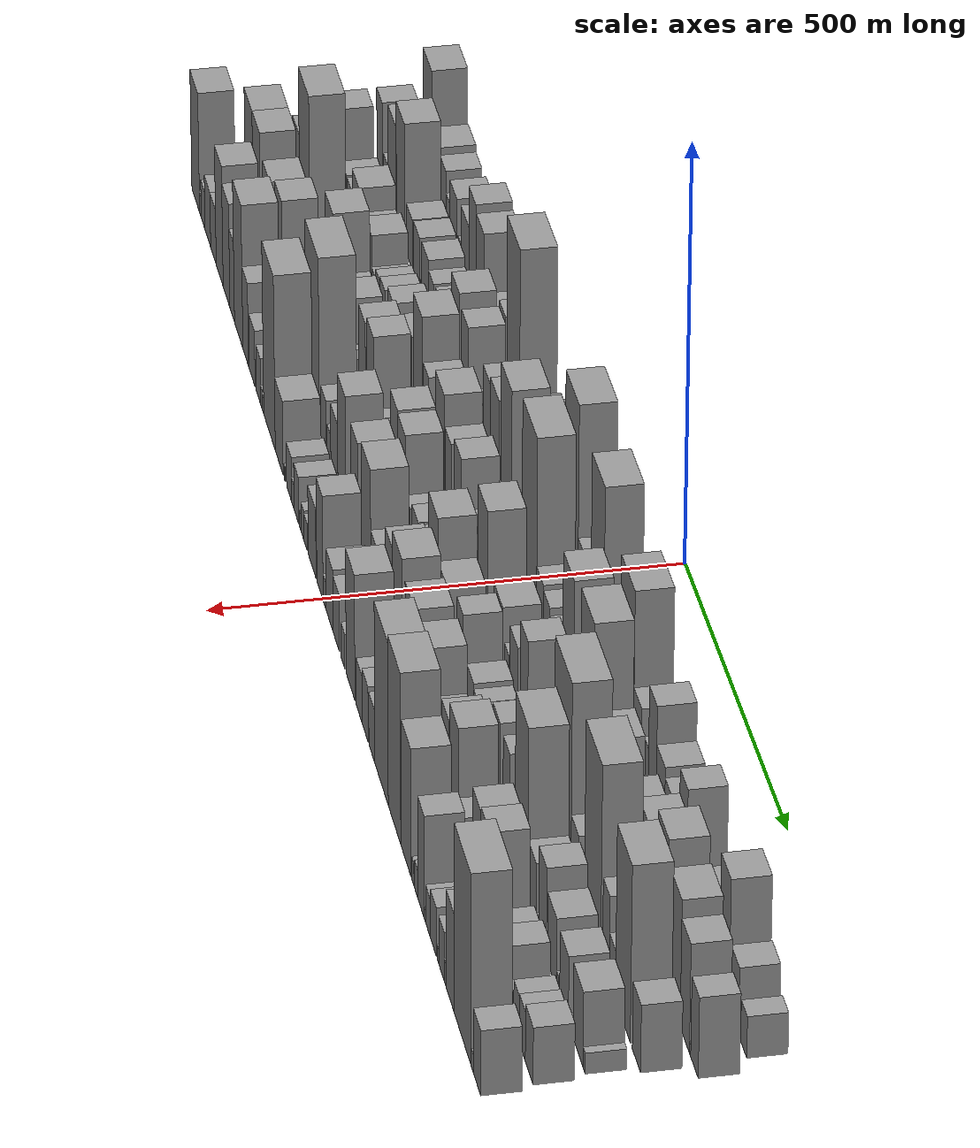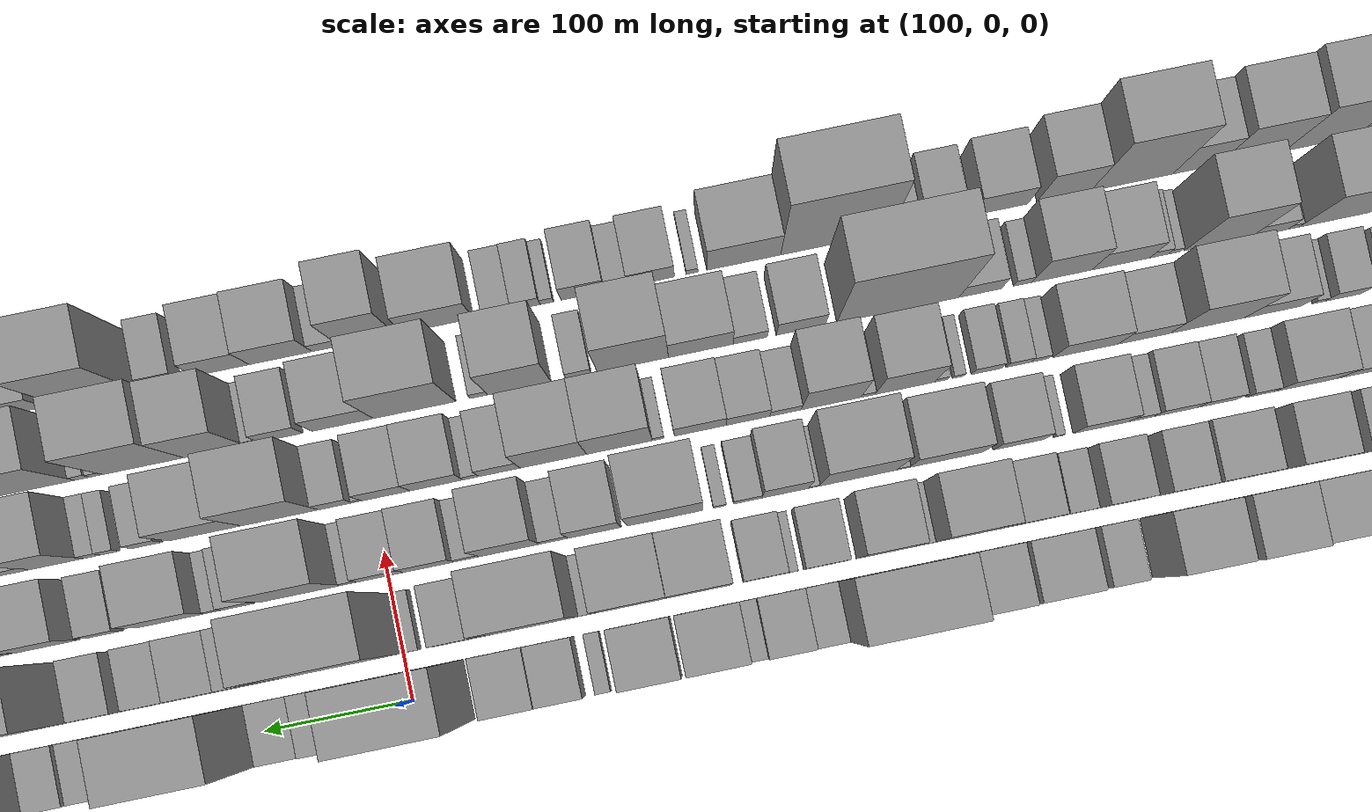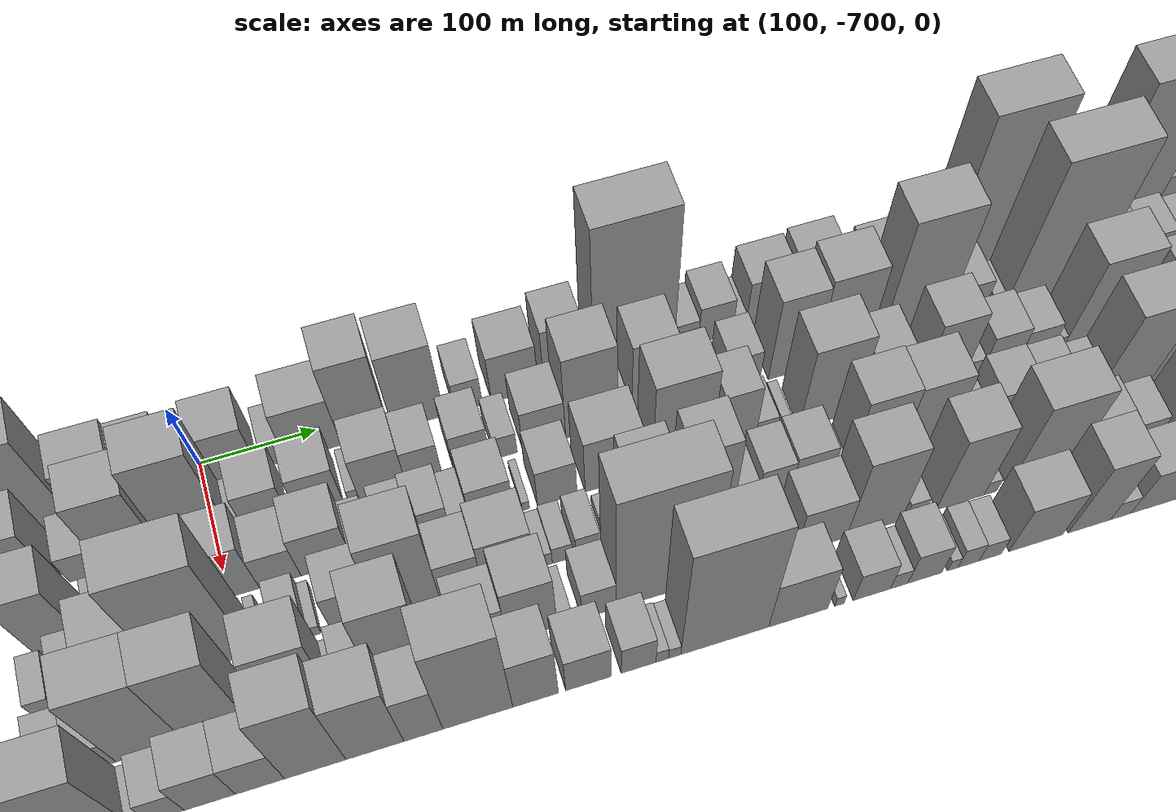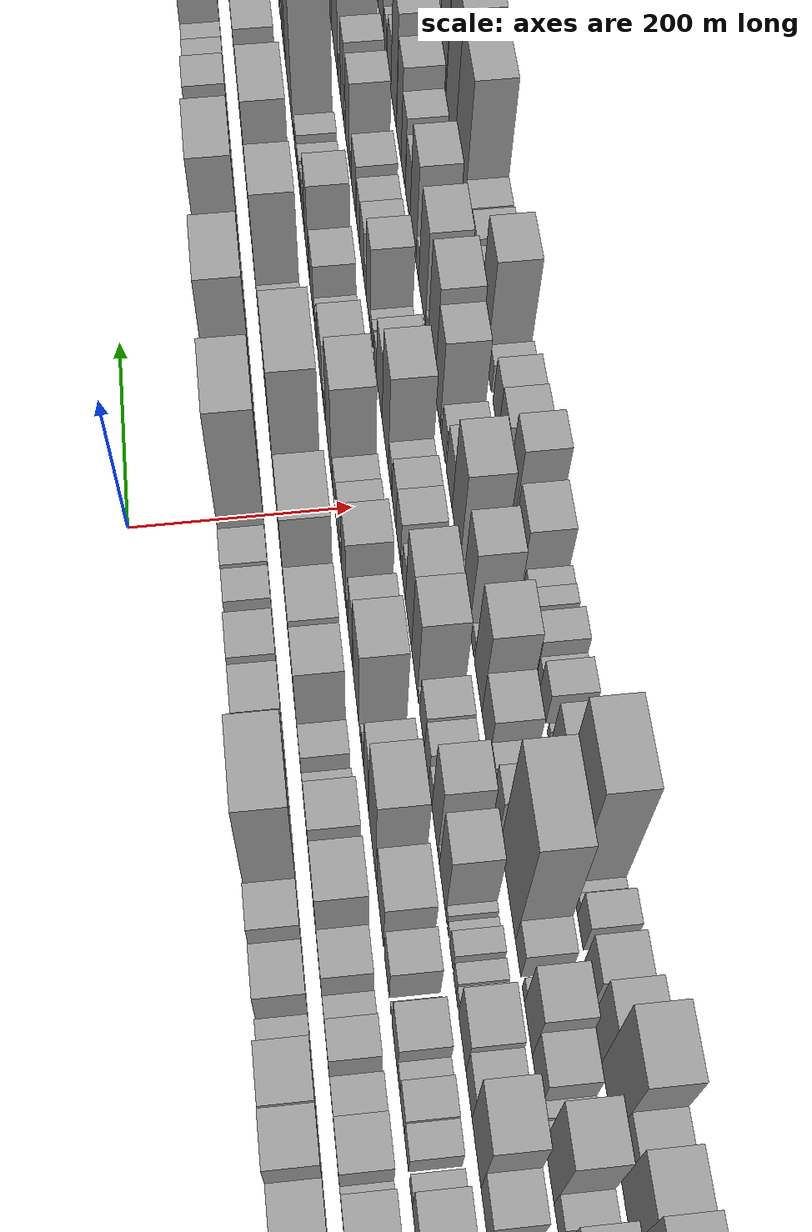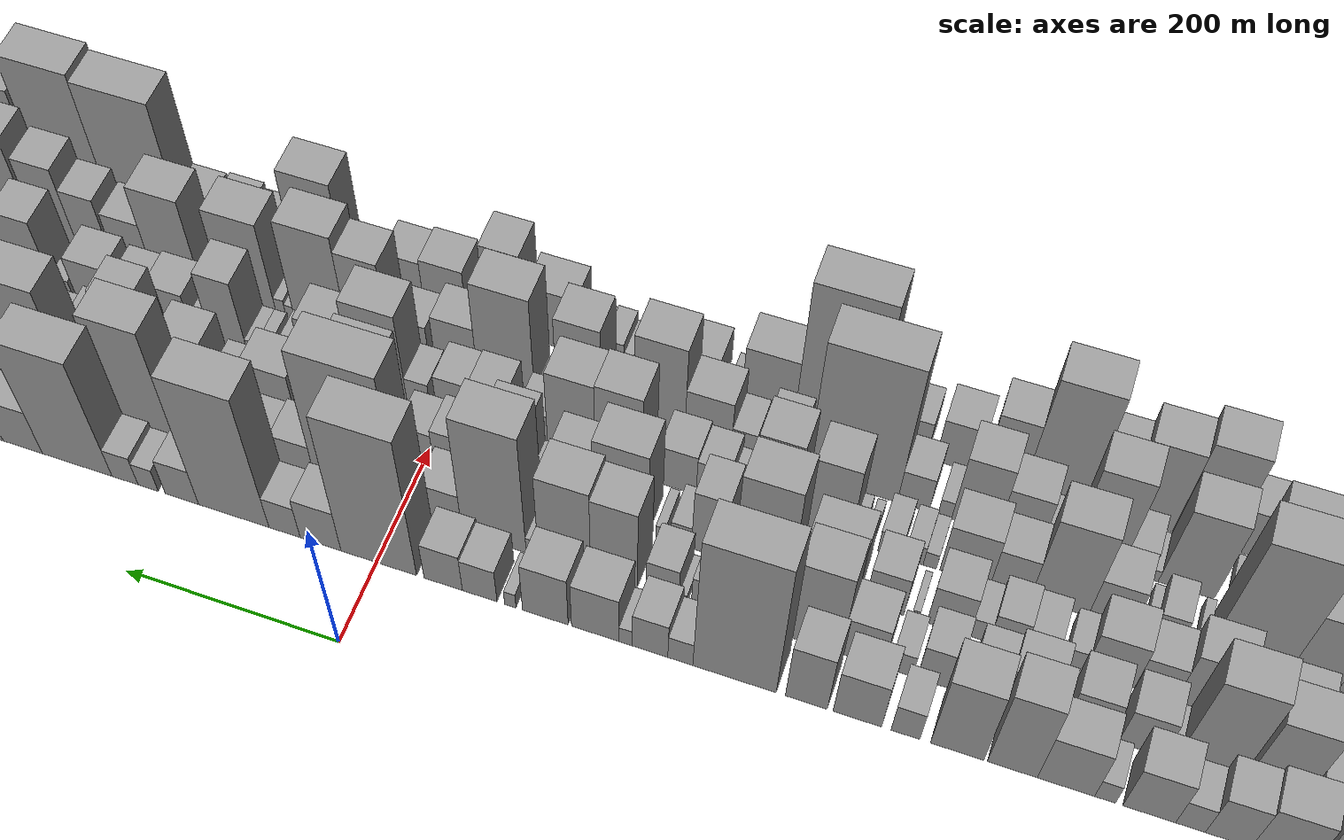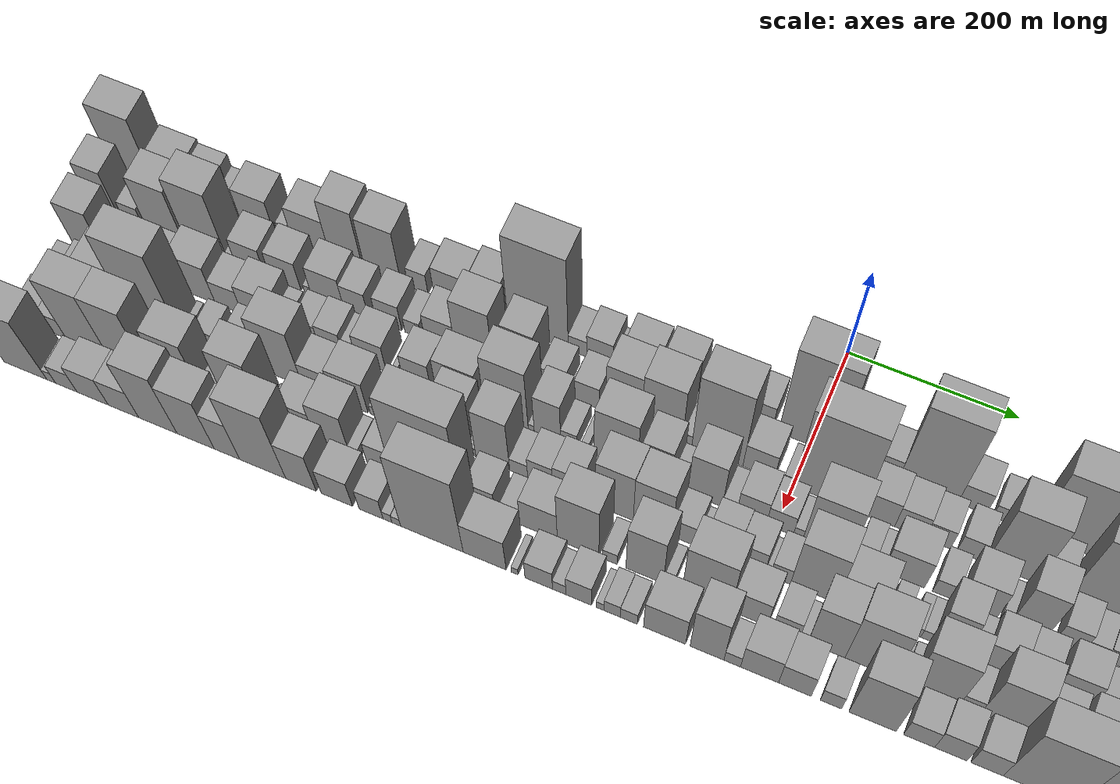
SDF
<sdf version="1.6">
 <world name="default">
  <scene>
   <sky><clouds><speed>12</speed></clouds></sky>
   <ambient>0.4 0.4 0.4 1</ambient>
   <background>0.7 0.7 0.7 1</background>
   <shadows>1</shadows>
  </scene>
  <gravity>0 0 -9.8066</gravity>
  <magnetic_field>6e-06 2.3e-05 -4.2e-05</magnetic_field>
  <physics default="0" name="default_physics" type="ode">
   <ode>
    <solver>
     <type>quick</type>
     <iters>10</iters>
     <sor>1.0</sor>
     <use_dynamic_moi_rescaling>0</use_dynamic_moi_rescaling>
    </solver>
    <constraints>
     <cfm>0</cfm>
     <erp>0.2</erp>
     <contact_max_correcting_vel>100</contact_max_correcting_vel>
     <contact_surface_layer>0.001</contact_surface_layer>
    </constraints>
   </ode>
   <max_step_size>0.004</max_step_size>
   <real_time_factor>1</real_time_factor>
   <real_time_update_rate>250</real_time_update_rate>
  </physics>
  <light name="sun" type="directional">
   <pose>0 0 10 0 0 0</pose>
   <diffuse>0.8 0.8 0.8 1</diffuse>
   <specular>0.2 0.2 0.2 1</specular>
   <attenuation>
    <range>1000</range>
    <constant>0.9</constant>
    <linear>0.01</linear>
    <quadratic>0.001</quadratic>
   </attenuation>
   <direction>-0.5 0.1 -0.9</direction>
  </light>
  <model name="building_1">
   <static>1</static>
   <pose>100.0000 -833.1717 0 0.000000 0.000000 0.000000</pose>
   <link name="link">
    <pose>0 0 75.00 0 0 0</pose>
    <collision name="collision"><geometry><box><size>40.0000 53.6566 150.0000</size></box></geometry></collision>
    <visual name="visual">
     <cast_shadows>0</cast_shadows>
     <geometry><box><size>40.0000 53.6566 150.0000</size></box></geometry>
     <material>
      <script>
       <uri>model://grey_wall/materials/scripts</uri>
       <uri>model://grey_wall/materials/textures</uri>
       <name>vrc/grey_wall</name>
      </script>
     </material>
    </visual>
   </link>
  </model>
  <model name="building_2">
   <static>1</static>
   <pose>100.0000 -780.0064 0 0.000000 0.000000 0.000000</pose>
   <link name="link">
    <pose>0 0 40.50 0 0 0</pose>
    <collision name="collision"><geometry><box><size>40.0000 46.6742 81.0000</size></box></geometry></collision>
    <visual name="visual">
     <cast_shadows>0</cast_shadows>
     <geometry><box><size>40.0000 46.6742 81.0000</size></box></geometry>
     <material>
      <script>
       <uri>model://grey_wall/materials/scripts</uri>
       <uri>model://grey_wall/materials/textures</uri>
       <name>vrc/grey_wall</name>
      </script>
     </material>
    </visual>
   </link>
  </model>
  <model name="building_3">
   <static>1</static>
   <pose>100.0000 -738.3833 0 0.000000 0.000000 0.000000</pose>
   <link name="link">
    <pose>0 0 36.00 0 0 0</pose>
    <collision name="collision"><geometry><box><size>40.0000 36.5720 72.0000</size></box></geometry></collision>
    <visual name="visual">
     <cast_shadows>0</cast_shadows>
     <geometry><box><size>40.0000 36.5720 72.0000</size></box></geometry>
     <material>
      <script>
       <uri>model://grey_wall/materials/scripts</uri>
       <uri>model://grey_wall/materials/textures</uri>
       <name>vrc/grey_wall</name>
      </script>
     </material>
    </visual>
   </link>
  </model>
  <model name="building_4">
   <static>1</static>
   <pose>100.0000 -708.1061 0 0.000000 0.000000 0.000000</pose>
   <link name="link">
    <pose>0 0 22.50 0 0 0</pose>
    <collision name="collision"><geometry><box><size>40.0000 23.9823 45.0000</size></box></geometry></collision>
    <visual name="visual">
     <cast_shadows>0</cast_shadows>
     <geometry><box><size>40.0000 23.9823 45.0000</size></box></geometry>
     <material>
      <script>
       <uri>model://grey_wall/materials/scripts</uri>
       <uri>model://grey_wall/materials/textures</uri>
       <name>vrc/grey_wall</name>
      </script>
     </material>
    </visual>
   </link>
  </model>
  <model name="building_5">
   <static>1</static>
   <pose>100.0000 -674.6245 0 0.000000 0.000000 0.000000</pose>
   <link name="link">
    <pose>0 0 37.50 0 0 0</pose>
    <collision name="collision"><geometry><box><size>40.0000 42.9808 75.0000</size></box></geometry></collision>
    <visual name="visual">
     <cast_shadows>0</cast_shadows>
     <geometry><box><size>40.0000 42.9808 75.0000</size></box></geometry>
     <material>
      <script>
       <uri>model://grey_wall/materials/scripts</uri>
       <uri>model://grey_wall/materials/textures</uri>
       <name>vrc/grey_wall</name>
      </script>
     </material>
    </visual>
   </link>
  </model>
  <model name="building_6">
   <static>1</static>
   <pose>100.0000 -638.5779 0 0.000000 0.000000 0.000000</pose>
   <link name="link">
    <pose>0 0 16.50 0 0 0</pose>
    <collision name="collision"><geometry><box><size>40.0000 17.1126 33.0000</size></box></geometry></collision>
    <visual name="visual">
     <cast_shadows>0</cast_shadows>
     <geometry><box><size>40.0000 17.1126 33.0000</size></box></geometry>
     <material>
      <script>
       <uri>model://grey_wall/materials/scripts</uri>
       <uri>model://grey_wall/materials/textures</uri>
       <name>vrc/grey_wall</name>
      </script>
     </material>
    </visual>
   </link>
  </model>
  <model name="building_7">
   <static>1</static>
   <pose>100.0000 -606.3343 0 0.000000 0.000000 0.000000</pose>
   <link name="link">
    <pose>0 0 40.50 0 0 0</pose>
    <collision name="collision"><geometry><box><size>40.0000 47.3745 81.0000</size></box></geometry></collision>
    <visual name="visual">
     <cast_shadows>0</cast_shadows>
     <geometry><box><size>40.0000 47.3745 81.0000</size></box></geometry>
     <material>
      <script>
       <uri>model://grey_wall/materials/scripts</uri>
       <uri>model://grey_wall/materials/textures</uri>
       <name>vrc/grey_wall</name>
      </script>
     </material>
    </visual>
   </link>
  </model>
  <model name="building_8">
   <static>1</static>
   <pose>100.0000 -561.8409 0 0.000000 0.000000 0.000000</pose>
   <link name="link">
    <pose>0 0 66.00 0 0 0</pose>
    <collision name="collision"><geometry><box><size>40.0000 41.6123 132.0000</size></box></geometry></collision>
    <visual name="visual">
     <cast_shadows>0</cast_shadows>
     <geometry><box><size>40.0000 41.6123 132.0000</size></box></geometry>
     <material>
      <script>
       <uri>model://grey_wall/materials/scripts</uri>
       <uri>model://grey_wall/materials/textures</uri>
       <name>vrc/grey_wall</name>
      </script>
     </material>
    </visual>
   </link>
  </model>
  <model name="building_9">
   <static>1</static>
   <pose>100.0000 -515.5603 0 0.000000 0.000000 0.000000</pose>
   <link name="link">
    <pose>0 0 61.50 0 0 0</pose>
    <collision name="collision"><geometry><box><size>40.0000 44.9489 123.0000</size></box></geometry></collision>
    <visual name="visual">
     <cast_shadows>0</cast_shadows>
     <geometry><box><size>40.0000 44.9489 123.0000</size></box></geometry>
     <material>
      <script>
       <uri>model://grey_wall/materials/scripts</uri>
       <uri>model://grey_wall/materials/textures</uri>
       <name>vrc/grey_wall</name>
      </script>
     </material>
    </visual>
   </link>
  </model>
  <model name="building_10">
   <static>1</static>
   <pose>100.0000 -471.8173 0 0.000000 0.000000 0.000000</pose>
   <link name="link">
    <pose>0 0 24.00 0 0 0</pose>
    <collision name="collision"><geometry><box><size>40.0000 24.5371 48.0000</size></box></geometry></collision>
    <visual name="visual">
     <cast_shadows>0</cast_shadows>
     <geometry><box><size>40.0000 24.5371 48.0000</size></box></geometry>
     <material>
      <script>
       <uri>model://grey_wall/materials/scripts</uri>
       <uri>model://grey_wall/materials/textures</uri>
       <name>vrc/grey_wall</name>
      </script>
     </material>
    </visual>
   </link>
  </model>
  <model name="building_11">
   <static>1</static>
   <pose>100.0000 -430.7226 0 0.000000 0.000000 0.000000</pose>
   <link name="link">
    <pose>0 0 37.50 0 0 0</pose>
    <collision name="collision"><geometry><box><size>40.0000 41.6523 75.0000</size></box></geometry></collision>
    <visual name="visual">
     <cast_shadows>0</cast_shadows>
     <geometry><box><size>40.0000 41.6523 75.0000</size></box></geometry>
     <material>
      <script>
       <uri>model://grey_wall/materials/scripts</uri>
       <uri>model://grey_wall/materials/textures</uri>
       <name>vrc/grey_wall</name>
      </script>
     </material>
    </visual>
   </link>
  </model>
  <model name="building_12">
   <static>1</static>
   <pose>100.0000 -386.7678 0 0.000000 0.000000 0.000000</pose>
   <link name="link">
    <pose>0 0 46.50 0 0 0</pose>
    <collision name="collision"><geometry><box><size>40.0000 36.2573 93.0000</size></box></geometry></collision>
    <visual name="visual">
     <cast_shadows>0</cast_shadows>
     <geometry><box><size>40.0000 36.2573 93.0000</size></box></geometry>
     <material>
      <script>
       <uri>model://grey_wall/materials/scripts</uri>
       <uri>model://grey_wall/materials/textures</uri>
       <name>vrc/grey_wall</name>
      </script>
     </material>
    </visual>
   </link>
  </model>
  <model name="building_13">
   <static>1</static>
   <pose>100.0000 -324.0436 0 0.000000 0.000000 0.000000</pose>
   <link name="link">
    <pose>0 0 111.00 0 0 0</pose>
    <collision name="collision"><geometry><box><size>40.0000 73.1910 222.0000</size></box></geometry></collision>
    <visual name="visual">
     <cast_shadows>0</cast_shadows>
     <geometry><box><size>40.0000 73.1910 222.0000</size></box></geometry>
     <material>
      <script>
       <uri>model://grey_wall/materials/scripts</uri>
       <uri>model://grey_wall/materials/textures</uri>
       <name>vrc/grey_wall</name>
      </script>
     </material>
    </visual>
   </link>
  </model>
  <model name="building_14">
   <static>1</static>
   <pose>100.0000 -276.3522 0 0.000000 0.000000 0.000000</pose>
   <link name="link">
    <pose>0 0 19.50 0 0 0</pose>
    <collision name="collision"><geometry><box><size>40.0000 22.1919 39.0000</size></box></geometry></collision>
    <visual name="visual">
     <cast_shadows>0</cast_shadows>
     <geometry><box><size>40.0000 22.1919 39.0000</size></box></geometry>
     <material>
      <script>
       <uri>model://grey_wall/materials/scripts</uri>
       <uri>model://grey_wall/materials/textures</uri>
       <name>vrc/grey_wall</name>
      </script>
     </material>
    </visual>
   </link>
  </model>
  <model name="building_15">
   <static>1</static>
   <pose>100.0000 -249.4096 0 0.000000 0.000000 0.000000</pose>
   <link name="link">
    <pose>0 0 28.50 0 0 0</pose>
    <collision name="collision"><geometry><box><size>40.0000 31.6933 57.0000</size></box></geometry></collision>
    <visual name="visual">
     <cast_shadows>0</cast_shadows>
     <geometry><box><size>40.0000 31.6933 57.0000</size></box></geometry>
     <material>
      <script>
       <uri>model://grey_wall/materials/scripts</uri>
       <uri>model://grey_wall/materials/textures</uri>
       <name>vrc/grey_wall</name>
      </script>
     </material>
    </visual>
   </link>
  </model>
  <model name="building_16">
   <static>1</static>
   <pose>100.0000 -227.6855 0 0.000000 0.000000 0.000000</pose>
   <link name="link">
    <pose>0 0 13.50 0 0 0</pose>
    <collision name="collision"><geometry><box><size>40.0000 11.7548 27.0000</size></box></geometry></collision>
    <visual name="visual">
     <cast_shadows>0</cast_shadows>
     <geometry><box><size>40.0000 11.7548 27.0000</size></box></geometry>
     <material>
      <script>
       <uri>model://grey_wall/materials/scripts</uri>
       <uri>model://grey_wall/materials/textures</uri>
       <name>vrc/grey_wall</name>
      </script>
     </material>
    </visual>
   </link>
  </model>
  <model name="building_17">
   <static>1</static>
   <pose>100.0000 -200.4722 0 0.000000 0.000000 0.000000</pose>
   <link name="link">
    <pose>0 0 37.50 0 0 0</pose>
    <collision name="collision"><geometry><box><size>40.0000 42.6718 75.0000</size></box></geometry></collision>
    <visual name="visual">
     <cast_shadows>0</cast_shadows>
     <geometry><box><size>40.0000 42.6718 75.0000</size></box></geometry>
     <material>
      <script>
       <uri>model://grey_wall/materials/scripts</uri>
       <uri>model://grey_wall/materials/textures</uri>
       <name>vrc/grey_wall</name>
      </script>
     </material>
    </visual>
   </link>
  </model>
  <model name="building_18">
   <static>1</static>
   <pose>100.0000 -155.4308 0 0.000000 0.000000 0.000000</pose>
   <link name="link">
    <pose>0 0 40.50 0 0 0</pose>
    <collision name="collision"><geometry><box><size>40.0000 41.4111 81.0000</size></box></geometry></collision>
    <visual name="visual">
     <cast_shadows>0</cast_shadows>
     <geometry><box><size>40.0000 41.4111 81.0000</size></box></geometry>
     <material>
      <script>
       <uri>model://grey_wall/materials/scripts</uri>
       <uri>model://grey_wall/materials/textures</uri>
       <name>vrc/grey_wall</name>
      </script>
     </material>
    </visual>
   </link>
  </model>
  <model name="building_19">
   <static>1</static>
   <pose>100.0000 -123.5469 0 0.000000 0.000000 0.000000</pose>
   <link name="link">
    <pose>0 0 12.00 0 0 0</pose>
    <collision name="collision"><geometry><box><size>40.0000 10.3565 24.0000</size></box></geometry></collision>
    <visual name="visual">
     <cast_shadows>0</cast_shadows>
     <geometry><box><size>40.0000 10.3565 24.0000</size></box></geometry>
     <material>
      <script>
       <uri>model://grey_wall/materials/scripts</uri>
       <uri>model://grey_wall/materials/textures</uri>
       <name>vrc/grey_wall</name>
      </script>
     </material>
    </visual>
   </link>
  </model>
  <model name="building_20">
   <static>1</static>
   <pose>100.0000 -95.4819 0 0.000000 0.000000 0.000000</pose>
   <link name="link">
    <pose>0 0 27.00 0 0 0</pose>
    <collision name="collision"><geometry><box><size>40.0000 31.7735 54.0000</size></box></geometry></collision>
    <visual name="visual">
     <cast_shadows>0</cast_shadows>
     <geometry><box><size>40.0000 31.7735 54.0000</size></box></geometry>
     <material>
      <script>
       <uri>model://grey_wall/materials/scripts</uri>
       <uri>model://grey_wall/materials/textures</uri>
       <name>vrc/grey_wall</name>
      </script>
     </material>
    </visual>
   </link>
  </model>
  <model name="building_21">
   <static>1</static>
   <pose>100.0000 -61.8837 0 0.000000 0.000000 0.000000</pose>
   <link name="link">
    <pose>0 0 30.00 0 0 0</pose>
    <collision name="collision"><geometry><box><size>40.0000 35.4228 60.0000</size></box></geometry></collision>
    <visual name="visual">
     <cast_shadows>0</cast_shadows>
     <geometry><box><size>40.0000 35.4228 60.0000</size></box></geometry>
     <material>
      <script>
       <uri>model://grey_wall/materials/scripts</uri>
       <uri>model://grey_wall/materials/textures</uri>
       <name>vrc/grey_wall</name>
      </script>
     </material>
    </visual>
   </link>
  </model>
  <model name="building_22">
   <static>1</static>
   <pose>100.0000 -1.7306 0 0.000000 0.000000 0.000000</pose>
   <link name="link">
    <pose>0 0 112.50 0 0 0</pose>
    <collision name="collision"><geometry><box><size>40.0000 70.8834 225.0000</size></box></geometry></collision>
    <visual name="visual">
     <cast_shadows>0</cast_shadows>
     <geometry><box><size>40.0000 70.8834 225.0000</size></box></geometry>
     <material>
      <script>
       <uri>model://grey_wall/materials/scripts</uri>
       <uri>model://grey_wall/materials/textures</uri>
       <name>vrc/grey_wall</name>
      </script>
     </material>
    </visual>
   </link>
  </model>
  <model name="building_23">
   <static>1</static>
   <pose>100.0000 53.0281 0 0.000000 0.000000 0.000000</pose>
   <link name="link">
    <pose>0 0 33.00 0 0 0</pose>
    <collision name="collision"><geometry><box><size>40.0000 38.6341 66.0000</size></box></geometry></collision>
    <visual name="visual">
     <cast_shadows>0</cast_shadows>
     <geometry><box><size>40.0000 38.6341 66.0000</size></box></geometry>
     <material>
      <script>
       <uri>model://grey_wall/materials/scripts</uri>
       <uri>model://grey_wall/materials/textures</uri>
       <name>vrc/grey_wall</name>
      </script>
     </material>
    </visual>
   </link>
  </model>
  <model name="building_24">
   <static>1</static>
   <pose>100.0000 87.2513 0 0.000000 0.000000 0.000000</pose>
   <link name="link">
    <pose>0 0 25.50 0 0 0</pose>
    <collision name="collision"><geometry><box><size>40.0000 29.8123 51.0000</size></box></geometry></collision>
    <visual name="visual">
     <cast_shadows>0</cast_shadows>
     <geometry><box><size>40.0000 29.8123 51.0000</size></box></geometry>
     <material>
      <script>
       <uri>model://grey_wall/materials/scripts</uri>
       <uri>model://grey_wall/materials/textures</uri>
       <name>vrc/grey_wall</name>
      </script>
     </material>
    </visual>
   </link>
  </model>
  <model name="building_25">
   <static>1</static>
   <pose>100.0000 136.0312 0 0.000000 0.000000 0.000000</pose>
   <link name="link">
    <pose>0 0 105.00 0 0 0</pose>
    <collision name="collision"><geometry><box><size>40.0000 67.7475 210.0000</size></box></geometry></collision>
    <visual name="visual">
     <cast_shadows>0</cast_shadows>
     <geometry><box><size>40.0000 67.7475 210.0000</size></box></geometry>
     <material>
      <script>
       <uri>model://grey_wall/materials/scripts</uri>
       <uri>model://grey_wall/materials/textures</uri>
       <name>vrc/grey_wall</name>
      </script>
     </material>
    </visual>
   </link>
  </model>
  <model name="building_26">
   <static>1</static>
   <pose>100.0000 186.0648 0 0.000000 0.000000 0.000000</pose>
   <link name="link">
    <pose>0 0 28.50 0 0 0</pose>
    <collision name="collision"><geometry><box><size>40.0000 32.3198 57.0000</size></box></geometry></collision>
    <visual name="visual">
     <cast_shadows>0</cast_shadows>
     <geometry><box><size>40.0000 32.3198 57.0000</size></box></geometry>
     <material>
      <script>
       <uri>model://grey_wall/materials/scripts</uri>
       <uri>model://grey_wall/materials/textures</uri>
       <name>vrc/grey_wall</name>
      </script>
     </material>
    </visual>
   </link>
  </model>
  <model name="building_27">
   <static>1</static>
   <pose>100.0000 219.0778 0 0.000000 0.000000 0.000000</pose>
   <link name="link">
    <pose>0 0 18.00 0 0 0</pose>
    <collision name="collision"><geometry><box><size>40.0000 19.7062 36.0000</size></box></geometry></collision>
    <visual name="visual">
     <cast_shadows>0</cast_shadows>
     <geometry><box><size>40.0000 19.7062 36.0000</size></box></geometry>
     <material>
      <script>
       <uri>model://grey_wall/materials/scripts</uri>
       <uri>model://grey_wall/materials/textures</uri>
       <name>vrc/grey_wall</name>
      </script>
     </material>
    </visual>
   </link>
  </model>
  <model name="building_28">
   <static>1</static>
   <pose>100.0000 241.7471 0 0.000000 0.000000 0.000000</pose>
   <link name="link">
    <pose>0 0 22.50 0 0 0</pose>
    <collision name="collision"><geometry><box><size>40.0000 25.6323 45.0000</size></box></geometry></collision>
    <visual name="visual">
     <cast_shadows>0</cast_shadows>
     <geometry><box><size>40.0000 25.6323 45.0000</size></box></geometry>
     <material>
      <script>
       <uri>model://grey_wall/materials/scripts</uri>
       <uri>model://grey_wall/materials/textures</uri>
       <name>vrc/grey_wall</name>
      </script>
     </material>
    </visual>
   </link>
  </model>
  <model name="building_29">
   <static>1</static>
   <pose>100.0000 288.9999 0 0.000000 0.000000 0.000000</pose>
   <link name="link">
    <pose>0 0 91.50 0 0 0</pose>
    <collision name="collision"><geometry><box><size>40.0000 68.8734 183.0000</size></box></geometry></collision>
    <visual name="visual">
     <cast_shadows>0</cast_shadows>
     <geometry><box><size>40.0000 68.8734 183.0000</size></box></geometry>
     <material>
      <script>
       <uri>model://grey_wall/materials/scripts</uri>
       <uri>model://grey_wall/materials/textures</uri>
       <name>vrc/grey_wall</name>
      </script>
     </material>
    </visual>
   </link>
  </model>
  <model name="building_30">
   <static>1</static>
   <pose>100.0000 343.2457 0 0.000000 0.000000 0.000000</pose>
   <link name="link">
    <pose>0 0 34.50 0 0 0</pose>
    <collision name="collision"><geometry><box><size>40.0000 39.6182 69.0000</size></box></geometry></collision>
    <visual name="visual">
     <cast_shadows>0</cast_shadows>
     <geometry><box><size>40.0000 39.6182 69.0000</size></box></geometry>
     <material>
      <script>
       <uri>model://grey_wall/materials/scripts</uri>
       <uri>model://grey_wall/materials/textures</uri>
       <name>vrc/grey_wall</name>
      </script>
     </material>
    </visual>
   </link>
  </model>
  <model name="building_31">
   <static>1</static>
   <pose>100.0000 367.4526 0 0.000000 0.000000 0.000000</pose>
   <link name="link">
    <pose>0 0 9.00 0 0 0</pose>
    <collision name="collision"><geometry><box><size>40.0000 8.7956 18.0000</size></box></geometry></collision>
    <visual name="visual">
     <cast_shadows>0</cast_shadows>
     <geometry><box><size>40.0000 8.7956 18.0000</size></box></geometry>
     <material>
      <script>
       <uri>model://grey_wall/materials/scripts</uri>
       <uri>model://grey_wall/materials/textures</uri>
       <name>vrc/grey_wall</name>
      </script>
     </material>
    </visual>
   </link>
  </model>
  <model name="building_32">
   <static>1</static>
   <pose>100.0000 387.1631 0 0.000000 0.000000 0.000000</pose>
   <link name="link">
    <pose>0 0 22.50 0 0 0</pose>
    <collision name="collision"><geometry><box><size>40.0000 22.6254 45.0000</size></box></geometry></collision>
    <visual name="visual">
     <cast_shadows>0</cast_shadows>
     <geometry><box><size>40.0000 22.6254 45.0000</size></box></geometry>
     <material>
      <script>
       <uri>model://grey_wall/materials/scripts</uri>
       <uri>model://grey_wall/materials/textures</uri>
       <name>vrc/grey_wall</name>
      </script>
     </material>
    </visual>
   </link>
  </model>
  <model name="building_33">
   <static>1</static>
   <pose>100.0000 417.9332 0 0.000000 0.000000 0.000000</pose>
   <link name="link">
    <pose>0 0 60.00 0 0 0</pose>
    <collision name="collision"><geometry><box><size>40.0000 38.9148 120.0000</size></box></geometry></collision>
    <visual name="visual">
     <cast_shadows>0</cast_shadows>
     <geometry><box><size>40.0000 38.9148 120.0000</size></box></geometry>
     <material>
      <script>
       <uri>model://grey_wall/materials/scripts</uri>
       <uri>model://grey_wall/materials/textures</uri>
       <name>vrc/grey_wall</name>
      </script>
     </material>
    </visual>
   </link>
  </model>
  <model name="building_34">
   <static>1</static>
   <pose>100.0000 458.2009 0 0.000000 0.000000 0.000000</pose>
   <link name="link">
    <pose>0 0 37.50 0 0 0</pose>
    <collision name="collision"><geometry><box><size>40.0000 41.6207 75.0000</size></box></geometry></collision>
    <visual name="visual">
     <cast_shadows>0</cast_shadows>
     <geometry><box><size>40.0000 41.6207 75.0000</size></box></geometry>
     <material>
      <script>
       <uri>model://grey_wall/materials/scripts</uri>
       <uri>model://grey_wall/materials/textures</uri>
       <name>vrc/grey_wall</name>
      </script>
     </material>
    </visual>
   </link>
  </model>
  <model name="building_35">
   <static>1</static>
   <pose>100.0000 497.6259 0 0.000000 0.000000 0.000000</pose>
   <link name="link">
    <pose>0 0 31.50 0 0 0</pose>
    <collision name="collision"><geometry><box><size>40.0000 37.2293 63.0000</size></box></geometry></collision>
    <visual name="visual">
     <cast_shadows>0</cast_shadows>
     <geometry><box><size>40.0000 37.2293 63.0000</size></box></geometry>
     <material>
      <script>
       <uri>model://grey_wall/materials/scripts</uri>
       <uri>model://grey_wall/materials/textures</uri>
       <name>vrc/grey_wall</name>
      </script>
     </material>
    </visual>
   </link>
  </model>
  <model name="building_36">
   <static>1</static>
   <pose>100.0000 535.2975 0 0.000000 0.000000 0.000000</pose>
   <link name="link">
    <pose>0 0 25.50 0 0 0</pose>
    <collision name="collision"><geometry><box><size>40.0000 28.1139 51.0000</size></box></geometry></collision>
    <visual name="visual">
     <cast_shadows>0</cast_shadows>
     <geometry><box><size>40.0000 28.1139 51.0000</size></box></geometry>
     <material>
      <script>
       <uri>model://grey_wall/materials/scripts</uri>
       <uri>model://grey_wall/materials/textures</uri>
       <name>vrc/grey_wall</name>
      </script>
     </material>
    </visual>
   </link>
  </model>
  <model name="building_37">
   <static>1</static>
   <pose>100.0000 568.2960 0 0.000000 0.000000 0.000000</pose>
   <link name="link">
    <pose>0 0 60.00 0 0 0</pose>
    <collision name="collision"><geometry><box><size>40.0000 37.8832 120.0000</size></box></geometry></collision>
    <visual name="visual">
     <cast_shadows>0</cast_shadows>
     <geometry><box><size>40.0000 37.8832 120.0000</size></box></geometry>
     <material>
      <script>
       <uri>model://grey_wall/materials/scripts</uri>
       <uri>model://grey_wall/materials/textures</uri>
       <name>vrc/grey_wall</name>
      </script>
     </material>
    </visual>
   </link>
  </model>
  <model name="building_38">
   <static>1</static>
   <pose>100.0000 591.5008 0 0.000000 0.000000 0.000000</pose>
   <link name="link">
    <pose>0 0 9.00 0 0 0</pose>
    <collision name="collision"><geometry><box><size>40.0000 8.5264 18.0000</size></box></geometry></collision>
    <visual name="visual">
     <cast_shadows>0</cast_shadows>
     <geometry><box><size>40.0000 8.5264 18.0000</size></box></geometry>
     <material>
      <script>
       <uri>model://grey_wall/materials/scripts</uri>
       <uri>model://grey_wall/materials/textures</uri>
       <name>vrc/grey_wall</name>
      </script>
     </material>
    </visual>
   </link>
  </model>
  <model name="building_39">
   <static>1</static>
   <pose>100.0000 604.7582 0 0.000000 0.000000 0.000000</pose>
   <link name="link">
    <pose>0 0 16.50 0 0 0</pose>
    <collision name="collision"><geometry><box><size>40.0000 17.9884 33.0000</size></box></geometry></collision>
    <visual name="visual">
     <cast_shadows>0</cast_shadows>
     <geometry><box><size>40.0000 17.9884 33.0000</size></box></geometry>
     <material>
      <script>
       <uri>model://grey_wall/materials/scripts</uri>
       <uri>model://grey_wall/materials/textures</uri>
       <name>vrc/grey_wall</name>
      </script>
     </material>
    </visual>
   </link>
  </model>
  <model name="building_40">
   <static>1</static>
   <pose>100.0000 625.6330 0 0.000000 0.000000 0.000000</pose>
   <link name="link">
    <pose>0 0 22.50 0 0 0</pose>
    <collision name="collision"><geometry><box><size>40.0000 23.7612 45.0000</size></box></geometry></collision>
    <visual name="visual">
     <cast_shadows>0</cast_shadows>
     <geometry><box><size>40.0000 23.7612 45.0000</size></box></geometry>
     <material>
      <script>
       <uri>model://grey_wall/materials/scripts</uri>
       <uri>model://grey_wall/materials/textures</uri>
       <name>vrc/grey_wall</name>
      </script>
     </material>
    </visual>
   </link>
  </model>
  <model name="building_41">
   <static>1</static>
   <pose>100.0000 660.9530 0 0.000000 0.000000 0.000000</pose>
   <link name="link">
    <pose>0 0 33.00 0 0 0</pose>
    <collision name="collision"><geometry><box><size>40.0000 36.8787 66.0000</size></box></geometry></collision>
    <visual name="visual">
     <cast_shadows>0</cast_shadows>
     <geometry><box><size>40.0000 36.8787 66.0000</size></box></geometry>
     <material>
      <script>
       <uri>model://grey_wall/materials/scripts</uri>
       <uri>model://grey_wall/materials/textures</uri>
       <name>vrc/grey_wall</name>
      </script>
     </material>
    </visual>
   </link>
  </model>
  <model name="building_42">
   <static>1</static>
   <pose>100.0000 694.8904 0 0.000000 0.000000 0.000000</pose>
   <link name="link">
    <pose>0 0 22.50 0 0 0</pose>
    <collision name="collision"><geometry><box><size>40.0000 22.9962 45.0000</size></box></geometry></collision>
    <visual name="visual">
     <cast_shadows>0</cast_shadows>
     <geometry><box><size>40.0000 22.9962 45.0000</size></box></geometry>
     <material>
      <script>
       <uri>model://grey_wall/materials/scripts</uri>
       <uri>model://grey_wall/materials/textures</uri>
       <name>vrc/grey_wall</name>
      </script>
     </material>
    </visual>
   </link>
  </model>
  <model name="building_43">
   <static>1</static>
   <pose>100.0000 724.4548 0 0.000000 0.000000 0.000000</pose>
   <link name="link">
    <pose>0 0 36.00 0 0 0</pose>
    <collision name="collision"><geometry><box><size>40.0000 36.1326 72.0000</size></box></geometry></collision>
    <visual name="visual">
     <cast_shadows>0</cast_shadows>
     <geometry><box><size>40.0000 36.1326 72.0000</size></box></geometry>
     <material>
      <script>
       <uri>model://grey_wall/materials/scripts</uri>
       <uri>model://grey_wall/materials/textures</uri>
       <name>vrc/grey_wall</name>
      </script>
     </material>
    </visual>
   </link>
  </model>
  <model name="building_44">
   <static>1</static>
   <pose>100.0000 765.5572 0 0.000000 0.000000 0.000000</pose>
   <link name="link">
    <pose>0 0 75.00 0 0 0</pose>
    <collision name="collision"><geometry><box><size>40.0000 46.0721 150.0000</size></box></geometry></collision>
    <visual name="visual">
     <cast_shadows>0</cast_shadows>
     <geometry><box><size>40.0000 46.0721 150.0000</size></box></geometry>
     <material>
      <script>
       <uri>model://grey_wall/materials/scripts</uri>
       <uri>model://grey_wall/materials/textures</uri>
       <name>vrc/grey_wall</name>
      </script>
     </material>
    </visual>
   </link>
  </model>
  <model name="building_45">
   <static>1</static>
   <pose>100.0000 813.1013 0 0.000000 0.000000 0.000000</pose>
   <link name="link">
    <pose>0 0 39.00 0 0 0</pose>
    <collision name="collision"><geometry><box><size>40.0000 39.0160 78.0000</size></box></geometry></collision>
    <visual name="visual">
     <cast_shadows>0</cast_shadows>
     <geometry><box><size>40.0000 39.0160 78.0000</size></box></geometry>
     <material>
      <script>
       <uri>model://grey_wall/materials/scripts</uri>
       <uri>model://grey_wall/materials/textures</uri>
       <name>vrc/grey_wall</name>
      </script>
     </material>
    </visual>
   </link>
  </model>
  <model name="building_46">
   <static>1</static>
   <pose>100.0000 856.8349 0 0.000000 0.000000 0.000000</pose>
   <link name="link">
    <pose>0 0 24.00 0 0 0</pose>
    <collision name="collision"><geometry><box><size>40.0000 28.4512 48.0000</size></box></geometry></collision>
    <visual name="visual">
     <cast_shadows>0</cast_shadows>
     <geometry><box><size>40.0000 28.4512 48.0000</size></box></geometry>
     <material>
      <script>
       <uri>model://grey_wall/materials/scripts</uri>
       <uri>model://grey_wall/materials/textures</uri>
       <name>vrc/grey_wall</name>
      </script>
     </material>
    </visual>
   </link>
  </model>
  <model name="building_47">
   <static>1</static>
   <pose>152.0000 -842.4721 0 0.000000 0.000000 0.000000</pose>
   <link name="link">
    <pose>0 0 52.50 0 0 0</pose>
    <collision name="collision"><geometry><box><size>40.0000 35.0558 105.0000</size></box></geometry></collision>
    <visual name="visual">
     <cast_shadows>0</cast_shadows>
     <geometry><box><size>40.0000 35.0558 105.0000</size></box></geometry>
     <material>
      <script>
       <uri>model://grey_wall/materials/scripts</uri>
       <uri>model://grey_wall/materials/textures</uri>
       <name>vrc/grey_wall</name>
      </script>
     </material>
    </visual>
   </link>
  </model>
  <model name="building_48">
   <static>1</static>
   <pose>152.0000 -806.3187 0 0.000000 0.000000 0.000000</pose>
   <link name="link">
    <pose>0 0 22.50 0 0 0</pose>
    <collision name="collision"><geometry><box><size>40.0000 25.2510 45.0000</size></box></geometry></collision>
    <visual name="visual">
     <cast_shadows>0</cast_shadows>
     <geometry><box><size>40.0000 25.2510 45.0000</size></box></geometry>
     <material>
      <script>
       <uri>model://grey_wall/materials/scripts</uri>
       <uri>model://grey_wall/materials/textures</uri>
       <name>vrc/grey_wall</name>
      </script>
     </material>
    </visual>
   </link>
  </model>
  <model name="building_49">
   <static>1</static>
   <pose>152.0000 -764.9670 0 0.000000 0.000000 0.000000</pose>
   <link name="link">
    <pose>0 0 61.50 0 0 0</pose>
    <collision name="collision"><geometry><box><size>40.0000 47.4525 123.0000</size></box></geometry></collision>
    <visual name="visual">
     <cast_shadows>0</cast_shadows>
     <geometry><box><size>40.0000 47.4525 123.0000</size></box></geometry>
     <material>
      <script>
       <uri>model://grey_wall/materials/scripts</uri>
       <uri>model://grey_wall/materials/textures</uri>
       <name>vrc/grey_wall</name>
      </script>
     </material>
    </visual>
   </link>
  </model>
  <model name="building_50">
   <static>1</static>
   <pose>152.0000 -711.3068 0 0.000000 0.000000 0.000000</pose>
   <link name="link">
    <pose>0 0 78.00 0 0 0</pose>
    <collision name="collision"><geometry><box><size>40.0000 51.8678 156.0000</size></box></geometry></collision>
    <visual name="visual">
     <cast_shadows>0</cast_shadows>
     <geometry><box><size>40.0000 51.8678 156.0000</size></box></geometry>
     <material>
      <script>
       <uri>model://grey_wall/materials/scripts</uri>
       <uri>model://grey_wall/materials/textures</uri>
       <name>vrc/grey_wall</name>
      </script>
     </material>
    </visual>
   </link>
  </model>
  <model name="building_51">
   <static>1</static>
   <pose>152.0000 -680.3910 0 0.000000 0.000000 0.000000</pose>
   <link name="link">
    <pose>0 0 12.00 0 0 0</pose>
    <collision name="collision"><geometry><box><size>40.0000 9.9638 24.0000</size></box></geometry></collision>
    <visual name="visual">
     <cast_shadows>0</cast_shadows>
     <geometry><box><size>40.0000 9.9638 24.0000</size></box></geometry>
     <material>
      <script>
       <uri>model://grey_wall/materials/scripts</uri>
       <uri>model://grey_wall/materials/textures</uri>
       <name>vrc/grey_wall</name>
      </script>
     </material>
    </visual>
   </link>
  </model>
  <model name="building_52">
   <static>1</static>
   <pose>152.0000 -656.7505 0 0.000000 0.000000 0.000000</pose>
   <link name="link">
    <pose>0 0 31.50 0 0 0</pose>
    <collision name="collision"><geometry><box><size>40.0000 37.3173 63.0000</size></box></geometry></collision>
    <visual name="visual">
     <cast_shadows>0</cast_shadows>
     <geometry><box><size>40.0000 37.3173 63.0000</size></box></geometry>
     <material>
      <script>
       <uri>model://grey_wall/materials/scripts</uri>
       <uri>model://grey_wall/materials/textures</uri>
       <name>vrc/grey_wall</name>
      </script>
     </material>
    </visual>
   </link>
  </model>
  <model name="building_53">
   <static>1</static>
   <pose>152.0000 -612.0903 0 0.000000 0.000000 0.000000</pose>
   <link name="link">
    <pose>0 0 33.00 0 0 0</pose>
    <collision name="collision"><geometry><box><size>40.0000 38.0031 66.0000</size></box></geometry></collision>
    <visual name="visual">
     <cast_shadows>0</cast_shadows>
     <geometry><box><size>40.0000 38.0031 66.0000</size></box></geometry>
     <material>
      <script>
       <uri>model://grey_wall/materials/scripts</uri>
       <uri>model://grey_wall/materials/textures</uri>
       <name>vrc/grey_wall</name>
      </script>
     </material>
    </visual>
   </link>
  </model>
  <model name="building_54">
   <static>1</static>
   <pose>152.0000 -584.7030 0 0.000000 0.000000 0.000000</pose>
   <link name="link">
    <pose>0 0 9.00 0 0 0</pose>
    <collision name="collision"><geometry><box><size>40.0000 8.7716 18.0000</size></box></geometry></collision>
    <visual name="visual">
     <cast_shadows>0</cast_shadows>
     <geometry><box><size>40.0000 8.7716 18.0000</size></box></geometry>
     <material>
      <script>
       <uri>model://grey_wall/materials/scripts</uri>
       <uri>model://grey_wall/materials/textures</uri>
       <name>vrc/grey_wall</name>
      </script>
     </material>
    </visual>
   </link>
  </model>
  <model name="building_55">
   <static>1</static>
   <pose>152.0000 -560.1190 0 0.000000 0.000000 0.000000</pose>
   <link name="link">
    <pose>0 0 34.50 0 0 0</pose>
    <collision name="collision"><geometry><box><size>40.0000 40.3963 69.0000</size></box></geometry></collision>
    <visual name="visual">
     <cast_shadows>0</cast_shadows>
     <geometry><box><size>40.0000 40.3963 69.0000</size></box></geometry>
     <material>
      <script>
       <uri>model://grey_wall/materials/scripts</uri>
       <uri>model://grey_wall/materials/textures</uri>
       <name>vrc/grey_wall</name>
      </script>
     </material>
    </visual>
   </link>
  </model>
  <model name="building_56">
   <static>1</static>
   <pose>152.0000 -524.5023 0 0.000000 0.000000 0.000000</pose>
   <link name="link">
    <pose>0 0 28.50 0 0 0</pose>
    <collision name="collision"><geometry><box><size>40.0000 30.8373 57.0000</size></box></geometry></collision>
    <visual name="visual">
     <cast_shadows>0</cast_shadows>
     <geometry><box><size>40.0000 30.8373 57.0000</size></box></geometry>
     <material>
      <script>
       <uri>model://grey_wall/materials/scripts</uri>
       <uri>model://grey_wall/materials/textures</uri>
       <name>vrc/grey_wall</name>
      </script>
     </material>
    </visual>
   </link>
  </model>
  <model name="building_57">
   <static>1</static>
   <pose>152.0000 -483.3467 0 0.000000 0.000000 0.000000</pose>
   <link name="link">
    <pose>0 0 30.00 0 0 0</pose>
    <collision name="collision"><geometry><box><size>40.0000 31.4739 60.0000</size></box></geometry></collision>
    <visual name="visual">
     <cast_shadows>0</cast_shadows>
     <geometry><box><size>40.0000 31.4739 60.0000</size></box></geometry>
     <material>
      <script>
       <uri>model://grey_wall/materials/scripts</uri>
       <uri>model://grey_wall/materials/textures</uri>
       <name>vrc/grey_wall</name>
      </script>
     </material>
    </visual>
   </link>
  </model>
  <model name="building_58">
   <static>1</static>
   <pose>152.0000 -453.8297 0 0.000000 0.000000 0.000000</pose>
   <link name="link">
    <pose>0 0 18.00 0 0 0</pose>
    <collision name="collision"><geometry><box><size>40.0000 19.5602 36.0000</size></box></geometry></collision>
    <visual name="visual">
     <cast_shadows>0</cast_shadows>
     <geometry><box><size>40.0000 19.5602 36.0000</size></box></geometry>
     <material>
      <script>
       <uri>model://grey_wall/materials/scripts</uri>
       <uri>model://grey_wall/materials/textures</uri>
       <name>vrc/grey_wall</name>
      </script>
     </material>
    </visual>
   </link>
  </model>
  <model name="building_59">
   <static>1</static>
   <pose>152.0000 -420.2904 0 0.000000 0.000000 0.000000</pose>
   <link name="link">
    <pose>0 0 33.00 0 0 0</pose>
    <collision name="collision"><geometry><box><size>40.0000 37.5183 66.0000</size></box></geometry></collision>
    <visual name="visual">
     <cast_shadows>0</cast_shadows>
     <geometry><box><size>40.0000 37.5183 66.0000</size></box></geometry>
     <material>
      <script>
       <uri>model://grey_wall/materials/scripts</uri>
       <uri>model://grey_wall/materials/textures</uri>
       <name>vrc/grey_wall</name>
      </script>
     </material>
    </visual>
   </link>
  </model>
  <model name="building_60">
   <static>1</static>
   <pose>152.0000 -378.5794 0 0.000000 0.000000 0.000000</pose>
   <link name="link">
    <pose>0 0 67.50 0 0 0</pose>
    <collision name="collision"><geometry><box><size>40.0000 45.9036 135.0000</size></box></geometry></collision>
    <visual name="visual">
     <cast_shadows>0</cast_shadows>
     <geometry><box><size>40.0000 45.9036 135.0000</size></box></geometry>
     <material>
      <script>
       <uri>model://grey_wall/materials/scripts</uri>
       <uri>model://grey_wall/materials/textures</uri>
       <name>vrc/grey_wall</name>
      </script>
     </material>
    </visual>
   </link>
  </model>
  <model name="building_61">
   <static>1</static>
   <pose>152.0000 -349.3866 0 0.000000 0.000000 0.000000</pose>
   <link name="link">
    <pose>0 0 13.50 0 0 0</pose>
    <collision name="collision"><geometry><box><size>40.0000 12.4821 27.0000</size></box></geometry></collision>
    <visual name="visual">
     <cast_shadows>0</cast_shadows>
     <geometry><box><size>40.0000 12.4821 27.0000</size></box></geometry>
     <material>
      <script>
       <uri>model://grey_wall/materials/scripts</uri>
       <uri>model://grey_wall/materials/textures</uri>
       <name>vrc/grey_wall</name>
      </script>
     </material>
    </visual>
   </link>
  </model>
  <model name="building_62">
   <static>1</static>
   <pose>152.0000 -323.6726 0 0.000000 0.000000 0.000000</pose>
   <link name="link">
    <pose>0 0 61.50 0 0 0</pose>
    <collision name="collision"><geometry><box><size>40.0000 38.9457 123.0000</size></box></geometry></collision>
    <visual name="visual">
     <cast_shadows>0</cast_shadows>
     <geometry><box><size>40.0000 38.9457 123.0000</size></box></geometry>
     <material>
      <script>
       <uri>model://grey_wall/materials/scripts</uri>
       <uri>model://grey_wall/materials/textures</uri>
       <name>vrc/grey_wall</name>
      </script>
     </material>
    </visual>
   </link>
  </model>
  <model name="building_63">
   <static>1</static>
   <pose>152.0000 -283.3929 0 0.000000 0.000000 0.000000</pose>
   <link name="link">
    <pose>0 0 25.50 0 0 0</pose>
    <collision name="collision"><geometry><box><size>40.0000 29.6139 51.0000</size></box></geometry></collision>
    <visual name="visual">
     <cast_shadows>0</cast_shadows>
     <geometry><box><size>40.0000 29.6139 51.0000</size></box></geometry>
     <material>
      <script>
       <uri>model://grey_wall/materials/scripts</uri>
       <uri>model://grey_wall/materials/textures</uri>
       <name>vrc/grey_wall</name>
      </script>
     </material>
    </visual>
   </link>
  </model>
  <model name="building_64">
   <static>1</static>
   <pose>152.0000 -261.0058 0 0.000000 0.000000 0.000000</pose>
   <link name="link">
    <pose>0 0 7.50 0 0 0</pose>
    <collision name="collision"><geometry><box><size>40.0000 7.1602 15.0000</size></box></geometry></collision>
    <visual name="visual">
     <cast_shadows>0</cast_shadows>
     <geometry><box><size>40.0000 7.1602 15.0000</size></box></geometry>
     <material>
      <script>
       <uri>model://grey_wall/materials/scripts</uri>
       <uri>model://grey_wall/materials/textures</uri>
       <name>vrc/grey_wall</name>
      </script>
     </material>
    </visual>
   </link>
  </model>
  <model name="building_65">
   <static>1</static>
   <pose>152.0000 -242.5919 0 0.000000 0.000000 0.000000</pose>
   <link name="link">
    <pose>0 0 27.00 0 0 0</pose>
    <collision name="collision"><geometry><box><size>40.0000 29.6675 54.0000</size></box></geometry></collision>
    <visual name="visual">
     <cast_shadows>0</cast_shadows>
     <geometry><box><size>40.0000 29.6675 54.0000</size></box></geometry>
     <material>
      <script>
       <uri>model://grey_wall/materials/scripts</uri>
       <uri>model://grey_wall/materials/textures</uri>
       <name>vrc/grey_wall</name>
      </script>
     </material>
    </visual>
   </link>
  </model>
  <model name="building_66">
   <static>1</static>
   <pose>152.0000 -198.6308 0 0.000000 0.000000 0.000000</pose>
   <link name="link">
    <pose>0 0 64.50 0 0 0</pose>
    <collision name="collision"><geometry><box><size>40.0000 42.2549 129.0000</size></box></geometry></collision>
    <visual name="visual">
     <cast_shadows>0</cast_shadows>
     <geometry><box><size>40.0000 42.2549 129.0000</size></box></geometry>
     <material>
      <script>
       <uri>model://grey_wall/materials/scripts</uri>
       <uri>model://grey_wall/materials/textures</uri>
       <name>vrc/grey_wall</name>
      </script>
     </material>
    </visual>
   </link>
  </model>
  <model name="building_67">
   <static>1</static>
   <pose>152.0000 -153.4668 0 0.000000 0.000000 0.000000</pose>
   <link name="link">
    <pose>0 0 69.00 0 0 0</pose>
    <collision name="collision"><geometry><box><size>40.0000 48.0730 138.0000</size></box></geometry></collision>
    <visual name="visual">
     <cast_shadows>0</cast_shadows>
     <geometry><box><size>40.0000 48.0730 138.0000</size></box></geometry>
     <material>
      <script>
       <uri>model://grey_wall/materials/scripts</uri>
       <uri>model://grey_wall/materials/textures</uri>
       <name>vrc/grey_wall</name>
      </script>
     </material>
    </visual>
   </link>
  </model>
  <model name="building_68">
   <static>1</static>
   <pose>152.0000 -123.7581 0 0.000000 0.000000 0.000000</pose>
   <link name="link">
    <pose>0 0 13.50 0 0 0</pose>
    <collision name="collision"><geometry><box><size>40.0000 11.3445 27.0000</size></box></geometry></collision>
    <visual name="visual">
     <cast_shadows>0</cast_shadows>
     <geometry><box><size>40.0000 11.3445 27.0000</size></box></geometry>
     <material>
      <script>
       <uri>model://grey_wall/materials/scripts</uri>
       <uri>model://grey_wall/materials/textures</uri>
       <name>vrc/grey_wall</name>
      </script>
     </material>
    </visual>
   </link>
  </model>
  <model name="building_69">
   <static>1</static>
   <pose>152.0000 -88.2406 0 0.000000 0.000000 0.000000</pose>
   <link name="link">
    <pose>0 0 96.00 0 0 0</pose>
    <collision name="collision"><geometry><box><size>40.0000 59.6905 192.0000</size></box></geometry></collision>
    <visual name="visual">
     <cast_shadows>0</cast_shadows>
     <geometry><box><size>40.0000 59.6905 192.0000</size></box></geometry>
     <material>
      <script>
       <uri>model://grey_wall/materials/scripts</uri>
       <uri>model://grey_wall/materials/textures</uri>
       <name>vrc/grey_wall</name>
      </script>
     </material>
    </visual>
   </link>
  </model>
  <model name="building_70">
   <static>1</static>
   <pose>152.0000 -39.9278 0 0.000000 0.000000 0.000000</pose>
   <link name="link">
    <pose>0 0 31.50 0 0 0</pose>
    <collision name="collision"><geometry><box><size>40.0000 36.9350 63.0000</size></box></geometry></collision>
    <visual name="visual">
     <cast_shadows>0</cast_shadows>
     <geometry><box><size>40.0000 36.9350 63.0000</size></box></geometry>
     <material>
      <script>
       <uri>model://grey_wall/materials/scripts</uri>
       <uri>model://grey_wall/materials/textures</uri>
       <name>vrc/grey_wall</name>
      </script>
     </material>
    </visual>
   </link>
  </model>
  <model name="building_71">
   <static>1</static>
   <pose>152.0000 -5.7813 0 0.000000 0.000000 0.000000</pose>
   <link name="link">
    <pose>0 0 12.00 0 0 0</pose>
    <collision name="collision"><geometry><box><size>40.0000 11.3581 24.0000</size></box></geometry></collision>
    <visual name="visual">
     <cast_shadows>0</cast_shadows>
     <geometry><box><size>40.0000 11.3581 24.0000</size></box></geometry>
     <material>
      <script>
       <uri>model://grey_wall/materials/scripts</uri>
       <uri>model://grey_wall/materials/textures</uri>
       <name>vrc/grey_wall</name>
      </script>
     </material>
    </visual>
   </link>
  </model>
  <model name="building_72">
   <static>1</static>
   <pose>152.0000 39.7575 0 0.000000 0.000000 0.000000</pose>
   <link name="link">
    <pose>0 0 109.50 0 0 0</pose>
    <collision name="collision"><geometry><box><size>40.0000 79.7196 219.0000</size></box></geometry></collision>
    <visual name="visual">
     <cast_shadows>0</cast_shadows>
     <geometry><box><size>40.0000 79.7196 219.0000</size></box></geometry>
     <material>
      <script>
       <uri>model://grey_wall/materials/scripts</uri>
       <uri>model://grey_wall/materials/textures</uri>
       <name>vrc/grey_wall</name>
      </script>
     </material>
    </visual>
   </link>
  </model>
  <model name="building_73">
   <static>1</static>
   <pose>152.0000 98.0294 0 0.000000 0.000000 0.000000</pose>
   <link name="link">
    <pose>0 0 33.00 0 0 0</pose>
    <collision name="collision"><geometry><box><size>40.0000 36.8241 66.0000</size></box></geometry></collision>
    <visual name="visual">
     <cast_shadows>0</cast_shadows>
     <geometry><box><size>40.0000 36.8241 66.0000</size></box></geometry>
     <material>
      <script>
       <uri>model://grey_wall/materials/scripts</uri>
       <uri>model://grey_wall/materials/textures</uri>
       <name>vrc/grey_wall</name>
      </script>
     </material>
    </visual>
   </link>
  </model>
  <model name="building_74">
   <static>1</static>
   <pose>152.0000 133.5778 0 0.000000 0.000000 0.000000</pose>
   <link name="link">
    <pose>0 0 30.00 0 0 0</pose>
    <collision name="collision"><geometry><box><size>40.0000 34.2728 60.0000</size></box></geometry></collision>
    <visual name="visual">
     <cast_shadows>0</cast_shadows>
     <geometry><box><size>40.0000 34.2728 60.0000</size></box></geometry>
     <material>
      <script>
       <uri>model://grey_wall/materials/scripts</uri>
       <uri>model://grey_wall/materials/textures</uri>
       <name>vrc/grey_wall</name>
      </script>
     </material>
    </visual>
   </link>
  </model>
  <model name="building_75">
   <static>1</static>
   <pose>152.0000 165.1294 0 0.000000 0.000000 0.000000</pose>
   <link name="link">
    <pose>0 0 25.50 0 0 0</pose>
    <collision name="collision"><geometry><box><size>40.0000 28.8304 51.0000</size></box></geometry></collision>
    <visual name="visual">
     <cast_shadows>0</cast_shadows>
     <geometry><box><size>40.0000 28.8304 51.0000</size></box></geometry>
     <material>
      <script>
       <uri>model://grey_wall/materials/scripts</uri>
       <uri>model://grey_wall/materials/textures</uri>
       <name>vrc/grey_wall</name>
      </script>
     </material>
    </visual>
   </link>
  </model>
  <model name="building_76">
   <static>1</static>
   <pose>152.0000 200.7614 0 0.000000 0.000000 0.000000</pose>
   <link name="link">
    <pose>0 0 25.50 0 0 0</pose>
    <collision name="collision"><geometry><box><size>40.0000 28.4336 51.0000</size></box></geometry></collision>
    <visual name="visual">
     <cast_shadows>0</cast_shadows>
     <geometry><box><size>40.0000 28.4336 51.0000</size></box></geometry>
     <material>
      <script>
       <uri>model://grey_wall/materials/scripts</uri>
       <uri>model://grey_wall/materials/textures</uri>
       <name>vrc/grey_wall</name>
      </script>
     </material>
    </visual>
   </link>
  </model>
  <model name="building_77">
   <static>1</static>
   <pose>152.0000 247.6808 0 0.000000 0.000000 0.000000</pose>
   <link name="link">
    <pose>0 0 85.50 0 0 0</pose>
    <collision name="collision"><geometry><box><size>40.0000 57.4052 171.0000</size></box></geometry></collision>
    <visual name="visual">
     <cast_shadows>0</cast_shadows>
     <geometry><box><size>40.0000 57.4052 171.0000</size></box></geometry>
     <material>
      <script>
       <uri>model://grey_wall/materials/scripts</uri>
       <uri>model://grey_wall/materials/textures</uri>
       <name>vrc/grey_wall</name>
      </script>
     </material>
    </visual>
   </link>
  </model>
  <model name="building_78">
   <static>1</static>
   <pose>152.0000 290.9962 0 0.000000 0.000000 0.000000</pose>
   <link name="link">
    <pose>0 0 28.50 0 0 0</pose>
    <collision name="collision"><geometry><box><size>40.0000 29.2255 57.0000</size></box></geometry></collision>
    <visual name="visual">
     <cast_shadows>0</cast_shadows>
     <geometry><box><size>40.0000 29.2255 57.0000</size></box></geometry>
     <material>
      <script>
       <uri>model://grey_wall/materials/scripts</uri>
       <uri>model://grey_wall/materials/textures</uri>
       <name>vrc/grey_wall</name>
      </script>
     </material>
    </visual>
   </link>
  </model>
  <model name="building_79">
   <static>1</static>
   <pose>152.0000 345.5288 0 0.000000 0.000000 0.000000</pose>
   <link name="link">
    <pose>0 0 93.00 0 0 0</pose>
    <collision name="collision"><geometry><box><size>40.0000 67.8399 186.0000</size></box></geometry></collision>
    <visual name="visual">
     <cast_shadows>0</cast_shadows>
     <geometry><box><size>40.0000 67.8399 186.0000</size></box></geometry>
     <material>
      <script>
       <uri>model://grey_wall/materials/scripts</uri>
       <uri>model://grey_wall/materials/textures</uri>
       <name>vrc/grey_wall</name>
      </script>
     </material>
    </visual>
   </link>
  </model>
  <model name="building_80">
   <static>1</static>
   <pose>152.0000 412.2853 0 0.000000 0.000000 0.000000</pose>
   <link name="link">
    <pose>0 0 43.50 0 0 0</pose>
    <collision name="collision"><geometry><box><size>40.0000 51.6730 87.0000</size></box></geometry></collision>
    <visual name="visual">
     <cast_shadows>0</cast_shadows>
     <geometry><box><size>40.0000 51.6730 87.0000</size></box></geometry>
     <material>
      <script>
       <uri>model://grey_wall/materials/scripts</uri>
       <uri>model://grey_wall/materials/textures</uri>
       <name>vrc/grey_wall</name>
      </script>
     </material>
    </visual>
   </link>
  </model>
  <model name="building_81">
   <static>1</static>
   <pose>152.0000 444.7932 0 0.000000 0.000000 0.000000</pose>
   <link name="link">
    <pose>0 0 13.50 0 0 0</pose>
    <collision name="collision"><geometry><box><size>40.0000 13.3429 27.0000</size></box></geometry></collision>
    <visual name="visual">
     <cast_shadows>0</cast_shadows>
     <geometry><box><size>40.0000 13.3429 27.0000</size></box></geometry>
     <material>
      <script>
       <uri>model://grey_wall/materials/scripts</uri>
       <uri>model://grey_wall/materials/textures</uri>
       <name>vrc/grey_wall</name>
      </script>
     </material>
    </visual>
   </link>
  </model>
  <model name="building_82">
   <static>1</static>
   <pose>152.0000 468.0257 0 0.000000 0.000000 0.000000</pose>
   <link name="link">
    <pose>0 0 21.00 0 0 0</pose>
    <collision name="collision"><geometry><box><size>40.0000 23.1219 42.0000</size></box></geometry></collision>
    <visual name="visual">
     <cast_shadows>0</cast_shadows>
     <geometry><box><size>40.0000 23.1219 42.0000</size></box></geometry>
     <material>
      <script>
       <uri>model://grey_wall/materials/scripts</uri>
       <uri>model://grey_wall/materials/textures</uri>
       <name>vrc/grey_wall</name>
      </script>
     </material>
    </visual>
   </link>
  </model>
  <model name="building_83">
   <static>1</static>
   <pose>152.0000 494.6608 0 0.000000 0.000000 0.000000</pose>
   <link name="link">
    <pose>0 0 12.00 0 0 0</pose>
    <collision name="collision"><geometry><box><size>40.0000 10.1484 24.0000</size></box></geometry></collision>
    <visual name="visual">
     <cast_shadows>0</cast_shadows>
     <geometry><box><size>40.0000 10.1484 24.0000</size></box></geometry>
     <material>
      <script>
       <uri>model://grey_wall/materials/scripts</uri>
       <uri>model://grey_wall/materials/textures</uri>
       <name>vrc/grey_wall</name>
      </script>
     </material>
    </visual>
   </link>
  </model>
  <model name="building_84">
   <static>1</static>
   <pose>152.0000 524.7785 0 0.000000 0.000000 0.000000</pose>
   <link name="link">
    <pose>0 0 42.00 0 0 0</pose>
    <collision name="collision"><geometry><box><size>40.0000 44.0869 84.0000</size></box></geometry></collision>
    <visual name="visual">
     <cast_shadows>0</cast_shadows>
     <geometry><box><size>40.0000 44.0869 84.0000</size></box></geometry>
     <material>
      <script>
       <uri>model://grey_wall/materials/scripts</uri>
       <uri>model://grey_wall/materials/textures</uri>
       <name>vrc/grey_wall</name>
      </script>
     </material>
    </visual>
   </link>
  </model>
  <model name="building_85">
   <static>1</static>
   <pose>152.0000 561.7094 0 0.000000 0.000000 0.000000</pose>
   <link name="link">
    <pose>0 0 25.50 0 0 0</pose>
    <collision name="collision"><geometry><box><size>40.0000 29.7749 51.0000</size></box></geometry></collision>
    <visual name="visual">
     <cast_shadows>0</cast_shadows>
     <geometry><box><size>40.0000 29.7749 51.0000</size></box></geometry>
     <material>
      <script>
       <uri>model://grey_wall/materials/scripts</uri>
       <uri>model://grey_wall/materials/textures</uri>
       <name>vrc/grey_wall</name>
      </script>
     </material>
    </visual>
   </link>
  </model>
  <model name="building_86">
   <static>1</static>
   <pose>152.0000 593.4386 0 0.000000 0.000000 0.000000</pose>
   <link name="link">
    <pose>0 0 19.50 0 0 0</pose>
    <collision name="collision"><geometry><box><size>40.0000 21.6834 39.0000</size></box></geometry></collision>
    <visual name="visual">
     <cast_shadows>0</cast_shadows>
     <geometry><box><size>40.0000 21.6834 39.0000</size></box></geometry>
     <material>
      <script>
       <uri>model://grey_wall/materials/scripts</uri>
       <uri>model://grey_wall/materials/textures</uri>
       <name>vrc/grey_wall</name>
      </script>
     </material>
    </visual>
   </link>
  </model>
  <model name="building_87">
   <static>1</static>
   <pose>152.0000 629.8472 0 0.000000 0.000000 0.000000</pose>
   <link name="link">
    <pose>0 0 64.50 0 0 0</pose>
    <collision name="collision"><geometry><box><size>40.0000 51.1340 129.0000</size></box></geometry></collision>
    <visual name="visual">
     <cast_shadows>0</cast_shadows>
     <geometry><box><size>40.0000 51.1340 129.0000</size></box></geometry>
     <material>
      <script>
       <uri>model://grey_wall/materials/scripts</uri>
       <uri>model://grey_wall/materials/textures</uri>
       <name>vrc/grey_wall</name>
      </script>
     </material>
    </visual>
   </link>
  </model>
  <model name="building_88">
   <static>1</static>
   <pose>152.0000 679.3440 0 0.000000 0.000000 0.000000</pose>
   <link name="link">
    <pose>0 0 27.00 0 0 0</pose>
    <collision name="collision"><geometry><box><size>40.0000 29.8596 54.0000</size></box></geometry></collision>
    <visual name="visual">
     <cast_shadows>0</cast_shadows>
     <geometry><box><size>40.0000 29.8596 54.0000</size></box></geometry>
     <material>
      <script>
       <uri>model://grey_wall/materials/scripts</uri>
       <uri>model://grey_wall/materials/textures</uri>
       <name>vrc/grey_wall</name>
      </script>
     </material>
    </visual>
   </link>
  </model>
  <model name="building_89">
   <static>1</static>
   <pose>152.0000 720.6267 0 0.000000 0.000000 0.000000</pose>
   <link name="link">
    <pose>0 0 87.00 0 0 0</pose>
    <collision name="collision"><geometry><box><size>40.0000 52.7057 174.0000</size></box></geometry></collision>
    <visual name="visual">
     <cast_shadows>0</cast_shadows>
     <geometry><box><size>40.0000 52.7057 174.0000</size></box></geometry>
     <material>
      <script>
       <uri>model://grey_wall/materials/scripts</uri>
       <uri>model://grey_wall/materials/textures</uri>
       <name>vrc/grey_wall</name>
      </script>
     </material>
    </visual>
   </link>
  </model>
  <model name="building_90">
   <static>1</static>
   <pose>152.0000 781.8052 0 0.000000 0.000000 0.000000</pose>
   <link name="link">
    <pose>0 0 73.50 0 0 0</pose>
    <collision name="collision"><geometry><box><size>40.0000 55.6515 147.0000</size></box></geometry></collision>
    <visual name="visual">
     <cast_shadows>0</cast_shadows>
     <geometry><box><size>40.0000 55.6515 147.0000</size></box></geometry>
     <material>
      <script>
       <uri>model://grey_wall/materials/scripts</uri>
       <uri>model://grey_wall/materials/textures</uri>
       <name>vrc/grey_wall</name>
      </script>
     </material>
    </visual>
   </link>
  </model>
  <model name="building_91">
   <static>1</static>
   <pose>152.0000 831.3857 0 0.000000 0.000000 0.000000</pose>
   <link name="link">
    <pose>0 0 63.00 0 0 0</pose>
    <collision name="collision"><geometry><box><size>40.0000 43.5095 126.0000</size></box></geometry></collision>
    <visual name="visual">
     <cast_shadows>0</cast_shadows>
     <geometry><box><size>40.0000 43.5095 126.0000</size></box></geometry>
     <material>
      <script>
       <uri>model://grey_wall/materials/scripts</uri>
       <uri>model://grey_wall/materials/textures</uri>
       <name>vrc/grey_wall</name>
      </script>
     </material>
    </visual>
   </link>
  </model>
  <model name="building_92">
   <static>1</static>
   <pose>152.0000 856.2176 0 0.000000 0.000000 0.000000</pose>
   <link name="link">
    <pose>0 0 7.50 0 0 0</pose>
    <collision name="collision"><geometry><box><size>40.0000 6.1543 15.0000</size></box></geometry></collision>
    <visual name="visual">
     <cast_shadows>0</cast_shadows>
     <geometry><box><size>40.0000 6.1543 15.0000</size></box></geometry>
     <material>
      <script>
       <uri>model://grey_wall/materials/scripts</uri>
       <uri>model://grey_wall/materials/textures</uri>
       <name>vrc/grey_wall</name>
      </script>
     </material>
    </visual>
   </link>
  </model>
  <model name="building_93">
   <static>1</static>
   <pose>152.0000 877.1196 0 0.000000 0.000000 0.000000</pose>
   <link name="link">
    <pose>0 0 46.50 0 0 0</pose>
    <collision name="collision"><geometry><box><size>40.0000 35.6496 93.0000</size></box></geometry></collision>
    <visual name="visual">
     <cast_shadows>0</cast_shadows>
     <geometry><box><size>40.0000 35.6496 93.0000</size></box></geometry>
     <material>
      <script>
       <uri>model://grey_wall/materials/scripts</uri>
       <uri>model://grey_wall/materials/textures</uri>
       <name>vrc/grey_wall</name>
      </script>
     </material>
    </visual>
   </link>
  </model>
  <model name="building_94">
   <static>1</static>
   <pose>204.0000 -833.7187 0 0.000000 0.000000 0.000000</pose>
   <link name="link">
    <pose>0 0 54.00 0 0 0</pose>
    <collision name="collision"><geometry><box><size>40.0000 40.5625 108.0000</size></box></geometry></collision>
    <visual name="visual">
     <cast_shadows>0</cast_shadows>
     <geometry><box><size>40.0000 40.5625 108.0000</size></box></geometry>
     <material>
      <script>
       <uri>model://grey_wall/materials/scripts</uri>
       <uri>model://grey_wall/materials/textures</uri>
       <name>vrc/grey_wall</name>
      </script>
     </material>
    </visual>
   </link>
  </model>
  <model name="building_95">
   <static>1</static>
   <pose>204.0000 -800.3558 0 0.000000 0.000000 0.000000</pose>
   <link name="link">
    <pose>0 0 13.50 0 0 0</pose>
    <collision name="collision"><geometry><box><size>40.0000 12.1633 27.0000</size></box></geometry></collision>
    <visual name="visual">
     <cast_shadows>0</cast_shadows>
     <geometry><box><size>40.0000 12.1633 27.0000</size></box></geometry>
     <material>
      <script>
       <uri>model://grey_wall/materials/scripts</uri>
       <uri>model://grey_wall/materials/textures</uri>
       <name>vrc/grey_wall</name>
      </script>
     </material>
    </visual>
   </link>
  </model>
  <model name="building_96">
   <static>1</static>
   <pose>204.0000 -772.7714 0 0.000000 0.000000 0.000000</pose>
   <link name="link">
    <pose>0 0 28.50 0 0 0</pose>
    <collision name="collision"><geometry><box><size>40.0000 33.0056 57.0000</size></box></geometry></collision>
    <visual name="visual">
     <cast_shadows>0</cast_shadows>
     <geometry><box><size>40.0000 33.0056 57.0000</size></box></geometry>
     <material>
      <script>
       <uri>model://grey_wall/materials/scripts</uri>
       <uri>model://grey_wall/materials/textures</uri>
       <name>vrc/grey_wall</name>
      </script>
     </material>
    </visual>
   </link>
  </model>
  <model name="building_97">
   <static>1</static>
   <pose>204.0000 -737.5766 0 0.000000 0.000000 0.000000</pose>
   <link name="link">
    <pose>0 0 28.50 0 0 0</pose>
    <collision name="collision"><geometry><box><size>40.0000 29.3840 57.0000</size></box></geometry></collision>
    <visual name="visual">
     <cast_shadows>0</cast_shadows>
     <geometry><box><size>40.0000 29.3840 57.0000</size></box></geometry>
     <material>
      <script>
       <uri>model://grey_wall/materials/scripts</uri>
       <uri>model://grey_wall/materials/textures</uri>
       <name>vrc/grey_wall</name>
      </script>
     </material>
    </visual>
   </link>
  </model>
  <model name="building_98">
   <static>1</static>
   <pose>204.0000 -697.2007 0 0.000000 0.000000 0.000000</pose>
   <link name="link">
    <pose>0 0 43.50 0 0 0</pose>
    <collision name="collision"><geometry><box><size>40.0000 45.3679 87.0000</size></box></geometry></collision>
    <visual name="visual">
     <cast_shadows>0</cast_shadows>
     <geometry><box><size>40.0000 45.3679 87.0000</size></box></geometry>
     <material>
      <script>
       <uri>model://grey_wall/materials/scripts</uri>
       <uri>model://grey_wall/materials/textures</uri>
       <name>vrc/grey_wall</name>
      </script>
     </material>
    </visual>
   </link>
  </model>
  <model name="building_99">
   <static>1</static>
   <pose>204.0000 -657.4961 0 0.000000 0.000000 0.000000</pose>
   <link name="link">
    <pose>0 0 28.50 0 0 0</pose>
    <collision name="collision"><geometry><box><size>40.0000 34.0412 57.0000</size></box></geometry></collision>
    <visual name="visual">
     <cast_shadows>0</cast_shadows>
     <geometry><box><size>40.0000 34.0412 57.0000</size></box></geometry>
     <material>
      <script>
       <uri>model://grey_wall/materials/scripts</uri>
       <uri>model://grey_wall/materials/textures</uri>
       <name>vrc/grey_wall</name>
      </script>
     </material>
    </visual>
   </link>
  </model>
  <model name="building_100">
   <static>1</static>
   <pose>204.0000 -619.0660 0 0.000000 0.000000 0.000000</pose>
   <link name="link">
    <pose>0 0 36.00 0 0 0</pose>
    <collision name="collision"><geometry><box><size>40.0000 42.8190 72.0000</size></box></geometry></collision>
    <visual name="visual">
     <cast_shadows>0</cast_shadows>
     <geometry><box><size>40.0000 42.8190 72.0000</size></box></geometry>
     <material>
      <script>
       <uri>model://grey_wall/materials/scripts</uri>
       <uri>model://grey_wall/materials/textures</uri>
       <name>vrc/grey_wall</name>
      </script>
     </material>
    </visual>
   </link>
  </model>
  <model name="building_101">
   <static>1</static>
   <pose>204.0000 -588.5305 0 0.000000 0.000000 0.000000</pose>
   <link name="link">
    <pose>0 0 16.50 0 0 0</pose>
    <collision name="collision"><geometry><box><size>40.0000 18.2520 33.0000</size></box></geometry></collision>
    <visual name="visual">
     <cast_shadows>0</cast_shadows>
     <geometry><box><size>40.0000 18.2520 33.0000</size></box></geometry>
     <material>
      <script>
       <uri>model://grey_wall/materials/scripts</uri>
       <uri>model://grey_wall/materials/textures</uri>
       <name>vrc/grey_wall</name>
      </script>
     </material>
    </visual>
   </link>
  </model>
  <model name="building_102">
   <static>1</static>
   <pose>204.0000 -559.1392 0 0.000000 0.000000 0.000000</pose>
   <link name="link">
    <pose>0 0 22.50 0 0 0</pose>
    <collision name="collision"><geometry><box><size>40.0000 26.5305 45.0000</size></box></geometry></collision>
    <visual name="visual">
     <cast_shadows>0</cast_shadows>
     <geometry><box><size>40.0000 26.5305 45.0000</size></box></geometry>
     <material>
      <script>
       <uri>model://grey_wall/materials/scripts</uri>
       <uri>model://grey_wall/materials/textures</uri>
       <name>vrc/grey_wall</name>
      </script>
     </material>
    </visual>
   </link>
  </model>
  <model name="building_103">
   <static>1</static>
   <pose>204.0000 -530.9005 0 0.000000 0.000000 0.000000</pose>
   <link name="link">
    <pose>0 0 25.50 0 0 0</pose>
    <collision name="collision"><geometry><box><size>40.0000 29.9469 51.0000</size></box></geometry></collision>
    <visual name="visual">
     <cast_shadows>0</cast_shadows>
     <geometry><box><size>40.0000 29.9469 51.0000</size></box></geometry>
     <material>
      <script>
       <uri>model://grey_wall/materials/scripts</uri>
       <uri>model://grey_wall/materials/textures</uri>
       <name>vrc/grey_wall</name>
      </script>
     </material>
    </visual>
   </link>
  </model>
  <model name="building_104">
   <static>1</static>
   <pose>204.0000 -507.3513 0 0.000000 0.000000 0.000000</pose>
   <link name="link">
    <pose>0 0 16.50 0 0 0</pose>
    <collision name="collision"><geometry><box><size>40.0000 17.1514 33.0000</size></box></geometry></collision>
    <visual name="visual">
     <cast_shadows>0</cast_shadows>
     <geometry><box><size>40.0000 17.1514 33.0000</size></box></geometry>
     <material>
      <script>
       <uri>model://grey_wall/materials/scripts</uri>
       <uri>model://grey_wall/materials/textures</uri>
       <name>vrc/grey_wall</name>
      </script>
     </material>
    </visual>
   </link>
  </model>
  <model name="building_105">
   <static>1</static>
   <pose>204.0000 -480.3464 0 0.000000 0.000000 0.000000</pose>
   <link name="link">
    <pose>0 0 33.00 0 0 0</pose>
    <collision name="collision"><geometry><box><size>40.0000 36.8584 66.0000</size></box></geometry></collision>
    <visual name="visual">
     <cast_shadows>0</cast_shadows>
     <geometry><box><size>40.0000 36.8584 66.0000</size></box></geometry>
     <material>
      <script>
       <uri>model://grey_wall/materials/scripts</uri>
       <uri>model://grey_wall/materials/textures</uri>
       <name>vrc/grey_wall</name>
      </script>
     </material>
    </visual>
   </link>
  </model>
  <model name="building_106">
   <static>1</static>
   <pose>204.0000 -451.7700 0 0.000000 0.000000 0.000000</pose>
   <link name="link">
    <pose>0 0 7.50 0 0 0</pose>
    <collision name="collision"><geometry><box><size>40.0000 6.2945 15.0000</size></box></geometry></collision>
    <visual name="visual">
     <cast_shadows>0</cast_shadows>
     <geometry><box><size>40.0000 6.2945 15.0000</size></box></geometry>
     <material>
      <script>
       <uri>model://grey_wall/materials/scripts</uri>
       <uri>model://grey_wall/materials/textures</uri>
       <name>vrc/grey_wall</name>
      </script>
     </material>
    </visual>
   </link>
  </model>
  <model name="building_107">
   <static>1</static>
   <pose>204.0000 -424.6322 0 0.000000 0.000000 0.000000</pose>
   <link name="link">
    <pose>0 0 31.50 0 0 0</pose>
    <collision name="collision"><geometry><box><size>40.0000 33.9812 63.0000</size></box></geometry></collision>
    <visual name="visual">
     <cast_shadows>0</cast_shadows>
     <geometry><box><size>40.0000 33.9812 63.0000</size></box></geometry>
     <material>
      <script>
       <uri>model://grey_wall/materials/scripts</uri>
       <uri>model://grey_wall/materials/textures</uri>
       <name>vrc/grey_wall</name>
      </script>
     </material>
    </visual>
   </link>
  </model>
  <model name="building_108">
   <static>1</static>
   <pose>204.0000 -375.7120 0 0.000000 0.000000 0.000000</pose>
   <link name="link">
    <pose>0 0 45.00 0 0 0</pose>
    <collision name="collision"><geometry><box><size>40.0000 49.8594 90.0000</size></box></geometry></collision>
    <visual name="visual">
     <cast_shadows>0</cast_shadows>
     <geometry><box><size>40.0000 49.8594 90.0000</size></box></geometry>
     <material>
      <script>
       <uri>model://grey_wall/materials/scripts</uri>
       <uri>model://grey_wall/materials/textures</uri>
       <name>vrc/grey_wall</name>
      </script>
     </material>
    </visual>
   </link>
  </model>
  <model name="building_109">
   <static>1</static>
   <pose>204.0000 -346.5106 0 0.000000 0.000000 0.000000</pose>
   <link name="link">
    <pose>0 0 9.00 0 0 0</pose>
    <collision name="collision"><geometry><box><size>40.0000 8.5434 18.0000</size></box></geometry></collision>
    <visual name="visual">
     <cast_shadows>0</cast_shadows>
     <geometry><box><size>40.0000 8.5434 18.0000</size></box></geometry>
     <material>
      <script>
       <uri>model://grey_wall/materials/scripts</uri>
       <uri>model://grey_wall/materials/textures</uri>
       <name>vrc/grey_wall</name>
      </script>
     </material>
    </visual>
   </link>
  </model>
  <model name="building_110">
   <static>1</static>
   <pose>204.0000 -316.1967 0 0.000000 0.000000 0.000000</pose>
   <link name="link">
    <pose>0 0 75.00 0 0 0</pose>
    <collision name="collision"><geometry><box><size>40.0000 52.0843 150.0000</size></box></geometry></collision>
    <visual name="visual">
     <cast_shadows>0</cast_shadows>
     <geometry><box><size>40.0000 52.0843 150.0000</size></box></geometry>
     <material>
      <script>
       <uri>model://grey_wall/materials/scripts</uri>
       <uri>model://grey_wall/materials/textures</uri>
       <name>vrc/grey_wall</name>
      </script>
     </material>
    </visual>
   </link>
  </model>
  <model name="building_111">
   <static>1</static>
   <pose>204.0000 -286.5430 0 0.000000 0.000000 0.000000</pose>
   <link name="link">
    <pose>0 0 7.50 0 0 0</pose>
    <collision name="collision"><geometry><box><size>40.0000 7.2230 15.0000</size></box></geometry></collision>
    <visual name="visual">
     <cast_shadows>0</cast_shadows>
     <geometry><box><size>40.0000 7.2230 15.0000</size></box></geometry>
     <material>
      <script>
       <uri>model://grey_wall/materials/scripts</uri>
       <uri>model://grey_wall/materials/textures</uri>
       <name>vrc/grey_wall</name>
      </script>
     </material>
    </visual>
   </link>
  </model>
  <model name="building_112">
   <static>1</static>
   <pose>204.0000 -267.1239 0 0.000000 0.000000 0.000000</pose>
   <link name="link">
    <pose>0 0 49.50 0 0 0</pose>
    <collision name="collision"><geometry><box><size>40.0000 31.6152 99.0000</size></box></geometry></collision>
    <visual name="visual">
     <cast_shadows>0</cast_shadows>
     <geometry><box><size>40.0000 31.6152 99.0000</size></box></geometry>
     <material>
      <script>
       <uri>model://grey_wall/materials/scripts</uri>
       <uri>model://grey_wall/materials/textures</uri>
       <name>vrc/grey_wall</name>
      </script>
     </material>
    </visual>
   </link>
  </model>
  <model name="building_113">
   <static>1</static>
   <pose>204.0000 -241.7476 0 0.000000 0.000000 0.000000</pose>
   <link name="link">
    <pose>0 0 18.00 0 0 0</pose>
    <collision name="collision"><geometry><box><size>40.0000 19.1375 36.0000</size></box></geometry></collision>
    <visual name="visual">
     <cast_shadows>0</cast_shadows>
     <geometry><box><size>40.0000 19.1375 36.0000</size></box></geometry>
     <material>
      <script>
       <uri>model://grey_wall/materials/scripts</uri>
       <uri>model://grey_wall/materials/textures</uri>
       <name>vrc/grey_wall</name>
      </script>
     </material>
    </visual>
   </link>
  </model>
  <model name="building_114">
   <static>1</static>
   <pose>204.0000 -222.8785 0 0.000000 0.000000 0.000000</pose>
   <link name="link">
    <pose>0 0 10.50 0 0 0</pose>
    <collision name="collision"><geometry><box><size>40.0000 8.6006 21.0000</size></box></geometry></collision>
    <visual name="visual">
     <cast_shadows>0</cast_shadows>
     <geometry><box><size>40.0000 8.6006 21.0000</size></box></geometry>
     <material>
      <script>
       <uri>model://grey_wall/materials/scripts</uri>
       <uri>model://grey_wall/materials/textures</uri>
       <name>vrc/grey_wall</name>
      </script>
     </material>
    </visual>
   </link>
  </model>
  <model name="building_115">
   <static>1</static>
   <pose>204.0000 -186.1275 0 0.000000 0.000000 0.000000</pose>
   <link name="link">
    <pose>0 0 66.00 0 0 0</pose>
    <collision name="collision"><geometry><box><size>40.0000 50.9014 132.0000</size></box></geometry></collision>
    <visual name="visual">
     <cast_shadows>0</cast_shadows>
     <geometry><box><size>40.0000 50.9014 132.0000</size></box></geometry>
     <material>
      <script>
       <uri>model://grey_wall/materials/scripts</uri>
       <uri>model://grey_wall/materials/textures</uri>
       <name>vrc/grey_wall</name>
      </script>
     </material>
    </visual>
   </link>
  </model>
  <model name="building_116">
   <static>1</static>
   <pose>204.0000 -138.9211 0 0.000000 0.000000 0.000000</pose>
   <link name="link">
    <pose>0 0 48.00 0 0 0</pose>
    <collision name="collision"><geometry><box><size>40.0000 35.5114 96.0000</size></box></geometry></collision>
    <visual name="visual">
     <cast_shadows>0</cast_shadows>
     <geometry><box><size>40.0000 35.5114 96.0000</size></box></geometry>
     <material>
      <script>
       <uri>model://grey_wall/materials/scripts</uri>
       <uri>model://grey_wall/materials/textures</uri>
       <name>vrc/grey_wall</name>
      </script>
     </material>
    </visual>
   </link>
  </model>
  <model name="building_117">
   <static>1</static>
   <pose>204.0000 -111.5576 0 0.000000 0.000000 0.000000</pose>
   <link name="link">
    <pose>0 0 18.00 0 0 0</pose>
    <collision name="collision"><geometry><box><size>40.0000 19.2158 36.0000</size></box></geometry></collision>
    <visual name="visual">
     <cast_shadows>0</cast_shadows>
     <geometry><box><size>40.0000 19.2158 36.0000</size></box></geometry>
     <material>
      <script>
       <uri>model://grey_wall/materials/scripts</uri>
       <uri>model://grey_wall/materials/textures</uri>
       <name>vrc/grey_wall</name>
      </script>
     </material>
    </visual>
   </link>
  </model>
  <model name="building_118">
   <static>1</static>
   <pose>204.0000 -81.7877 0 0.000000 0.000000 0.000000</pose>
   <link name="link">
    <pose>0 0 57.00 0 0 0</pose>
    <collision name="collision"><geometry><box><size>40.0000 40.3239 114.0000</size></box></geometry></collision>
    <visual name="visual">
     <cast_shadows>0</cast_shadows>
     <geometry><box><size>40.0000 40.3239 114.0000</size></box></geometry>
     <material>
      <script>
       <uri>model://grey_wall/materials/scripts</uri>
       <uri>model://grey_wall/materials/textures</uri>
       <name>vrc/grey_wall</name>
      </script>
     </material>
    </visual>
   </link>
  </model>
  <model name="building_119">
   <static>1</static>
   <pose>204.0000 -53.2513 0 0.000000 0.000000 0.000000</pose>
   <link name="link">
    <pose>0 0 15.00 0 0 0</pose>
    <collision name="collision"><geometry><box><size>40.0000 16.7489 30.0000</size></box></geometry></collision>
    <visual name="visual">
     <cast_shadows>0</cast_shadows>
     <geometry><box><size>40.0000 16.7489 30.0000</size></box></geometry>
     <material>
      <script>
       <uri>model://grey_wall/materials/scripts</uri>
       <uri>model://grey_wall/materials/textures</uri>
       <name>vrc/grey_wall</name>
      </script>
     </material>
    </visual>
   </link>
  </model>
  <model name="building_120">
   <static>1</static>
   <pose>204.0000 -27.8404 0 0.000000 0.000000 0.000000</pose>
   <link name="link">
    <pose>0 0 31.50 0 0 0</pose>
    <collision name="collision"><geometry><box><size>40.0000 34.0728 63.0000</size></box></geometry></collision>
    <visual name="visual">
     <cast_shadows>0</cast_shadows>
     <geometry><box><size>40.0000 34.0728 63.0000</size></box></geometry>
     <material>
      <script>
       <uri>model://grey_wall/materials/scripts</uri>
       <uri>model://grey_wall/materials/textures</uri>
       <name>vrc/grey_wall</name>
      </script>
     </material>
    </visual>
   </link>
  </model>
  <model name="building_121">
   <static>1</static>
   <pose>204.0000 4.6006 0 0.000000 0.000000 0.000000</pose>
   <link name="link">
    <pose>0 0 27.00 0 0 0</pose>
    <collision name="collision"><geometry><box><size>40.0000 30.8091 54.0000</size></box></geometry></collision>
    <visual name="visual">
     <cast_shadows>0</cast_shadows>
     <geometry><box><size>40.0000 30.8091 54.0000</size></box></geometry>
     <material>
      <script>
       <uri>model://grey_wall/materials/scripts</uri>
       <uri>model://grey_wall/materials/textures</uri>
       <name>vrc/grey_wall</name>
      </script>
     </material>
    </visual>
   </link>
  </model>
  <model name="building_122">
   <static>1</static>
   <pose>204.0000 25.6570 0 0.000000 0.000000 0.000000</pose>
   <link name="link">
    <pose>0 0 13.50 0 0 0</pose>
    <collision name="collision"><geometry><box><size>40.0000 11.3038 27.0000</size></box></geometry></collision>
    <visual name="visual">
     <cast_shadows>0</cast_shadows>
     <geometry><box><size>40.0000 11.3038 27.0000</size></box></geometry>
     <material>
      <script>
       <uri>model://grey_wall/materials/scripts</uri>
       <uri>model://grey_wall/materials/textures</uri>
       <name>vrc/grey_wall</name>
      </script>
     </material>
    </visual>
   </link>
  </model>
  <model name="building_123">
   <static>1</static>
   <pose>204.0000 58.3716 0 0.000000 0.000000 0.000000</pose>
   <link name="link">
    <pose>0 0 70.50 0 0 0</pose>
    <collision name="collision"><geometry><box><size>40.0000 54.1253 141.0000</size></box></geometry></collision>
    <visual name="visual">
     <cast_shadows>0</cast_shadows>
     <geometry><box><size>40.0000 54.1253 141.0000</size></box></geometry>
     <material>
      <script>
       <uri>model://grey_wall/materials/scripts</uri>
       <uri>model://grey_wall/materials/textures</uri>
       <name>vrc/grey_wall</name>
      </script>
     </material>
    </visual>
   </link>
  </model>
  <model name="building_124">
   <static>1</static>
   <pose>204.0000 100.2069 0 0.000000 0.000000 0.000000</pose>
   <link name="link">
    <pose>0 0 18.00 0 0 0</pose>
    <collision name="collision"><geometry><box><size>40.0000 21.5454 36.0000</size></box></geometry></collision>
    <visual name="visual">
     <cast_shadows>0</cast_shadows>
     <geometry><box><size>40.0000 21.5454 36.0000</size></box></geometry>
     <material>
      <script>
       <uri>model://grey_wall/materials/scripts</uri>
       <uri>model://grey_wall/materials/textures</uri>
       <name>vrc/grey_wall</name>
      </script>
     </material>
    </visual>
   </link>
  </model>
  <model name="building_125">
   <static>1</static>
   <pose>204.0000 116.3956 0 0.000000 0.000000 0.000000</pose>
   <link name="link">
    <pose>0 0 12.00 0 0 0</pose>
    <collision name="collision"><geometry><box><size>40.0000 10.8320 24.0000</size></box></geometry></collision>
    <visual name="visual">
     <cast_shadows>0</cast_shadows>
     <geometry><box><size>40.0000 10.8320 24.0000</size></box></geometry>
     <material>
      <script>
       <uri>model://grey_wall/materials/scripts</uri>
       <uri>model://grey_wall/materials/textures</uri>
       <name>vrc/grey_wall</name>
      </script>
     </material>
    </visual>
   </link>
  </model>
  <model name="building_126">
   <static>1</static>
   <pose>204.0000 145.1345 0 0.000000 0.000000 0.000000</pose>
   <link name="link">
    <pose>0 0 39.00 0 0 0</pose>
    <collision name="collision"><geometry><box><size>40.0000 46.6458 78.0000</size></box></geometry></collision>
    <visual name="visual">
     <cast_shadows>0</cast_shadows>
     <geometry><box><size>40.0000 46.6458 78.0000</size></box></geometry>
     <material>
      <script>
       <uri>model://grey_wall/materials/scripts</uri>
       <uri>model://grey_wall/materials/textures</uri>
       <name>vrc/grey_wall</name>
      </script>
     </material>
    </visual>
   </link>
  </model>
  <model name="building_127">
   <static>1</static>
   <pose>204.0000 189.7486 0 0.000000 0.000000 0.000000</pose>
   <link name="link">
    <pose>0 0 21.00 0 0 0</pose>
    <collision name="collision"><geometry><box><size>40.0000 24.5822 42.0000</size></box></geometry></collision>
    <visual name="visual">
     <cast_shadows>0</cast_shadows>
     <geometry><box><size>40.0000 24.5822 42.0000</size></box></geometry>
     <material>
      <script>
       <uri>model://grey_wall/materials/scripts</uri>
       <uri>model://grey_wall/materials/textures</uri>
       <name>vrc/grey_wall</name>
      </script>
     </material>
    </visual>
   </link>
  </model>
  <model name="building_128">
   <static>1</static>
   <pose>204.0000 228.4447 0 0.000000 0.000000 0.000000</pose>
   <link name="link">
    <pose>0 0 40.50 0 0 0</pose>
    <collision name="collision"><geometry><box><size>40.0000 42.8100 81.0000</size></box></geometry></collision>
    <visual name="visual">
     <cast_shadows>0</cast_shadows>
     <geometry><box><size>40.0000 42.8100 81.0000</size></box></geometry>
     <material>
      <script>
       <uri>model://grey_wall/materials/scripts</uri>
       <uri>model://grey_wall/materials/textures</uri>
       <name>vrc/grey_wall</name>
      </script>
     </material>
    </visual>
   </link>
  </model>
  <model name="building_129">
   <static>1</static>
   <pose>204.0000 258.7062 0 0.000000 0.000000 0.000000</pose>
   <link name="link">
    <pose>0 0 12.00 0 0 0</pose>
    <collision name="collision"><geometry><box><size>40.0000 11.7131 24.0000</size></box></geometry></collision>
    <visual name="visual">
     <cast_shadows>0</cast_shadows>
     <geometry><box><size>40.0000 11.7131 24.0000</size></box></geometry>
     <material>
      <script>
       <uri>model://grey_wall/materials/scripts</uri>
       <uri>model://grey_wall/materials/textures</uri>
       <name>vrc/grey_wall</name>
      </script>
     </material>
    </visual>
   </link>
  </model>
  <model name="building_130">
   <static>1</static>
   <pose>204.0000 284.2913 0 0.000000 0.000000 0.000000</pose>
   <link name="link">
    <pose>0 0 61.50 0 0 0</pose>
    <collision name="collision"><geometry><box><size>40.0000 39.4571 123.0000</size></box></geometry></collision>
    <visual name="visual">
     <cast_shadows>0</cast_shadows>
     <geometry><box><size>40.0000 39.4571 123.0000</size></box></geometry>
     <material>
      <script>
       <uri>model://grey_wall/materials/scripts</uri>
       <uri>model://grey_wall/materials/textures</uri>
       <name>vrc/grey_wall</name>
      </script>
     </material>
    </visual>
   </link>
  </model>
  <model name="building_131">
   <static>1</static>
   <pose>204.0000 328.4555 0 0.000000 0.000000 0.000000</pose>
   <link name="link">
    <pose>0 0 28.50 0 0 0</pose>
    <collision name="collision"><geometry><box><size>40.0000 30.8713 57.0000</size></box></geometry></collision>
    <visual name="visual">
     <cast_shadows>0</cast_shadows>
     <geometry><box><size>40.0000 30.8713 57.0000</size></box></geometry>
     <material>
      <script>
       <uri>model://grey_wall/materials/scripts</uri>
       <uri>model://grey_wall/materials/textures</uri>
       <name>vrc/grey_wall</name>
      </script>
     </material>
    </visual>
   </link>
  </model>
  <model name="building_132">
   <static>1</static>
   <pose>204.0000 355.1463 0 0.000000 0.000000 0.000000</pose>
   <link name="link">
    <pose>0 0 19.50 0 0 0</pose>
    <collision name="collision"><geometry><box><size>40.0000 22.5103 39.0000</size></box></geometry></collision>
    <visual name="visual">
     <cast_shadows>0</cast_shadows>
     <geometry><box><size>40.0000 22.5103 39.0000</size></box></geometry>
     <material>
      <script>
       <uri>model://grey_wall/materials/scripts</uri>
       <uri>model://grey_wall/materials/textures</uri>
       <name>vrc/grey_wall</name>
      </script>
     </material>
    </visual>
   </link>
  </model>
  <model name="building_133">
   <static>1</static>
   <pose>204.0000 377.4604 0 0.000000 0.000000 0.000000</pose>
   <link name="link">
    <pose>0 0 21.00 0 0 0</pose>
    <collision name="collision"><geometry><box><size>40.0000 22.1180 42.0000</size></box></geometry></collision>
    <visual name="visual">
     <cast_shadows>0</cast_shadows>
     <geometry><box><size>40.0000 22.1180 42.0000</size></box></geometry>
     <material>
      <script>
       <uri>model://grey_wall/materials/scripts</uri>
       <uri>model://grey_wall/materials/textures</uri>
       <name>vrc/grey_wall</name>
      </script>
     </material>
    </visual>
   </link>
  </model>
  <model name="building_134">
   <static>1</static>
   <pose>204.0000 406.9200 0 0.000000 0.000000 0.000000</pose>
   <link name="link">
    <pose>0 0 24.00 0 0 0</pose>
    <collision name="collision"><geometry><box><size>40.0000 26.8011 48.0000</size></box></geometry></collision>
    <visual name="visual">
     <cast_shadows>0</cast_shadows>
     <geometry><box><size>40.0000 26.8011 48.0000</size></box></geometry>
     <material>
      <script>
       <uri>model://grey_wall/materials/scripts</uri>
       <uri>model://grey_wall/materials/textures</uri>
       <name>vrc/grey_wall</name>
      </script>
     </material>
    </visual>
   </link>
  </model>
  <model name="building_135">
   <static>1</static>
   <pose>204.0000 423.8524 0 0.000000 0.000000 0.000000</pose>
   <link name="link">
    <pose>0 0 7.50 0 0 0</pose>
    <collision name="collision"><geometry><box><size>40.0000 7.0638 15.0000</size></box></geometry></collision>
    <visual name="visual">
     <cast_shadows>0</cast_shadows>
     <geometry><box><size>40.0000 7.0638 15.0000</size></box></geometry>
     <material>
      <script>
       <uri>model://grey_wall/materials/scripts</uri>
       <uri>model://grey_wall/materials/textures</uri>
       <name>vrc/grey_wall</name>
      </script>
     </material>
    </visual>
   </link>
  </model>
  <model name="building_136">
   <static>1</static>
   <pose>204.0000 439.6234 0 0.000000 0.000000 0.000000</pose>
   <link name="link">
    <pose>0 0 10.50 0 0 0</pose>
    <collision name="collision"><geometry><box><size>40.0000 8.4782 21.0000</size></box></geometry></collision>
    <visual name="visual">
     <cast_shadows>0</cast_shadows>
     <geometry><box><size>40.0000 8.4782 21.0000</size></box></geometry>
     <material>
      <script>
       <uri>model://grey_wall/materials/scripts</uri>
       <uri>model://grey_wall/materials/textures</uri>
       <name>vrc/grey_wall</name>
      </script>
     </material>
    </visual>
   </link>
  </model>
  <model name="building_137">
   <static>1</static>
   <pose>204.0000 487.2718 0 0.000000 0.000000 0.000000</pose>
   <link name="link">
    <pose>0 0 109.50 0 0 0</pose>
    <collision name="collision"><geometry><box><size>40.0000 86.8187 219.0000</size></box></geometry></collision>
    <visual name="visual">
     <cast_shadows>0</cast_shadows>
     <geometry><box><size>40.0000 86.8187 219.0000</size></box></geometry>
     <material>
      <script>
       <uri>model://grey_wall/materials/scripts</uri>
       <uri>model://grey_wall/materials/textures</uri>
       <name>vrc/grey_wall</name>
      </script>
     </material>
    </visual>
   </link>
  </model>
  <model name="building_138">
   <static>1</static>
   <pose>204.0000 549.7611 0 0.000000 0.000000 0.000000</pose>
   <link name="link">
    <pose>0 0 33.00 0 0 0</pose>
    <collision name="collision"><geometry><box><size>40.0000 38.1598 66.0000</size></box></geometry></collision>
    <visual name="visual">
     <cast_shadows>0</cast_shadows>
     <geometry><box><size>40.0000 38.1598 66.0000</size></box></geometry>
     <material>
      <script>
       <uri>model://grey_wall/materials/scripts</uri>
       <uri>model://grey_wall/materials/textures</uri>
       <name>vrc/grey_wall</name>
      </script>
     </material>
    </visual>
   </link>
  </model>
  <model name="building_139">
   <static>1</static>
   <pose>204.0000 577.8417 0 0.000000 0.000000 0.000000</pose>
   <link name="link">
    <pose>0 0 10.50 0 0 0</pose>
    <collision name="collision"><geometry><box><size>40.0000 10.0015 21.0000</size></box></geometry></collision>
    <visual name="visual">
     <cast_shadows>0</cast_shadows>
     <geometry><box><size>40.0000 10.0015 21.0000</size></box></geometry>
     <material>
      <script>
       <uri>model://grey_wall/materials/scripts</uri>
       <uri>model://grey_wall/materials/textures</uri>
       <name>vrc/grey_wall</name>
      </script>
     </material>
    </visual>
   </link>
  </model>
  <model name="building_140">
   <static>1</static>
   <pose>204.0000 587.1282 0 0.000000 0.000000 0.000000</pose>
   <link name="link">
    <pose>0 0 10.50 0 0 0</pose>
    <collision name="collision"><geometry><box><size>40.0000 8.5715 21.0000</size></box></geometry></collision>
    <visual name="visual">
     <cast_shadows>0</cast_shadows>
     <geometry><box><size>40.0000 8.5715 21.0000</size></box></geometry>
     <material>
      <script>
       <uri>model://grey_wall/materials/scripts</uri>
       <uri>model://grey_wall/materials/textures</uri>
       <name>vrc/grey_wall</name>
      </script>
     </material>
    </visual>
   </link>
  </model>
  <model name="building_141">
   <static>1</static>
   <pose>204.0000 640.2307 0 0.000000 0.000000 0.000000</pose>
   <link name="link">
    <pose>0 0 111.00 0 0 0</pose>
    <collision name="collision"><geometry><box><size>40.0000 81.6335 222.0000</size></box></geometry></collision>
    <visual name="visual">
     <cast_shadows>0</cast_shadows>
     <geometry><box><size>40.0000 81.6335 222.0000</size></box></geometry>
     <material>
      <script>
       <uri>model://grey_wall/materials/scripts</uri>
       <uri>model://grey_wall/materials/textures</uri>
       <name>vrc/grey_wall</name>
      </script>
     </material>
    </visual>
   </link>
  </model>
  <model name="building_142">
   <static>1</static>
   <pose>204.0000 706.3873 0 0.000000 0.000000 0.000000</pose>
   <link name="link">
    <pose>0 0 49.50 0 0 0</pose>
    <collision name="collision"><geometry><box><size>40.0000 32.6797 99.0000</size></box></geometry></collision>
    <visual name="visual">
     <cast_shadows>0</cast_shadows>
     <geometry><box><size>40.0000 32.6797 99.0000</size></box></geometry>
     <material>
      <script>
       <uri>model://grey_wall/materials/scripts</uri>
       <uri>model://grey_wall/materials/textures</uri>
       <name>vrc/grey_wall</name>
      </script>
     </material>
    </visual>
   </link>
  </model>
  <model name="building_143">
   <static>1</static>
   <pose>204.0000 738.4612 0 0.000000 0.000000 0.000000</pose>
   <link name="link">
    <pose>0 0 28.50 0 0 0</pose>
    <collision name="collision"><geometry><box><size>40.0000 31.4680 57.0000</size></box></geometry></collision>
    <visual name="visual">
     <cast_shadows>0</cast_shadows>
     <geometry><box><size>40.0000 31.4680 57.0000</size></box></geometry>
     <material>
      <script>
       <uri>model://grey_wall/materials/scripts</uri>
       <uri>model://grey_wall/materials/textures</uri>
       <name>vrc/grey_wall</name>
      </script>
     </material>
    </visual>
   </link>
  </model>
  <model name="building_144">
   <static>1</static>
   <pose>204.0000 790.3622 0 0.000000 0.000000 0.000000</pose>
   <link name="link">
    <pose>0 0 102.00 0 0 0</pose>
    <collision name="collision"><geometry><box><size>40.0000 72.3341 204.0000</size></box></geometry></collision>
    <visual name="visual">
     <cast_shadows>0</cast_shadows>
     <geometry><box><size>40.0000 72.3341 204.0000</size></box></geometry>
     <material>
      <script>
       <uri>model://grey_wall/materials/scripts</uri>
       <uri>model://grey_wall/materials/textures</uri>
       <name>vrc/grey_wall</name>
      </script>
     </material>
    </visual>
   </link>
  </model>
  <model name="building_145">
   <static>1</static>
   <pose>204.0000 856.4001 0 0.000000 0.000000 0.000000</pose>
   <link name="link">
    <pose>0 0 39.00 0 0 0</pose>
    <collision name="collision"><geometry><box><size>40.0000 39.7417 78.0000</size></box></geometry></collision>
    <visual name="visual">
     <cast_shadows>0</cast_shadows>
     <geometry><box><size>40.0000 39.7417 78.0000</size></box></geometry>
     <material>
      <script>
       <uri>model://grey_wall/materials/scripts</uri>
       <uri>model://grey_wall/materials/textures</uri>
       <name>vrc/grey_wall</name>
      </script>
     </material>
    </visual>
   </link>
  </model>
  <model name="building_146">
   <static>1</static>
   <pose>256.0000 -850.7327 0 0.000000 0.000000 0.000000</pose>
   <link name="link">
    <pose>0 0 18.00 0 0 0</pose>
    <collision name="collision"><geometry><box><size>40.0000 18.5346 36.0000</size></box></geometry></collision>
    <visual name="visual">
     <cast_shadows>0</cast_shadows>
     <geometry><box><size>40.0000 18.5346 36.0000</size></box></geometry>
     <material>
      <script>
       <uri>model://grey_wall/materials/scripts</uri>
       <uri>model://grey_wall/materials/textures</uri>
       <name>vrc/grey_wall</name>
      </script>
     </material>
    </visual>
   </link>
  </model>
  <model name="building_147">
   <static>1</static>
   <pose>256.0000 -836.5018 0 0.000000 0.000000 0.000000</pose>
   <link name="link">
    <pose>0 0 12.00 0 0 0</pose>
    <collision name="collision"><geometry><box><size>40.0000 9.9272 24.0000</size></box></geometry></collision>
    <visual name="visual">
     <cast_shadows>0</cast_shadows>
     <geometry><box><size>40.0000 9.9272 24.0000</size></box></geometry>
     <material>
      <script>
       <uri>model://grey_wall/materials/scripts</uri>
       <uri>model://grey_wall/materials/textures</uri>
       <name>vrc/grey_wall</name>
      </script>
     </material>
    </visual>
   </link>
  </model>
  <model name="building_148">
   <static>1</static>
   <pose>256.0000 -815.3508 0 0.000000 0.000000 0.000000</pose>
   <link name="link">
    <pose>0 0 30.00 0 0 0</pose>
    <collision name="collision"><geometry><box><size>40.0000 32.3750 60.0000</size></box></geometry></collision>
    <visual name="visual">
     <cast_shadows>0</cast_shadows>
     <geometry><box><size>40.0000 32.3750 60.0000</size></box></geometry>
     <material>
      <script>
       <uri>model://grey_wall/materials/scripts</uri>
       <uri>model://grey_wall/materials/textures</uri>
       <name>vrc/grey_wall</name>
      </script>
     </material>
    </visual>
   </link>
  </model>
  <model name="building_149">
   <static>1</static>
   <pose>256.0000 -778.0849 0 0.000000 0.000000 0.000000</pose>
   <link name="link">
    <pose>0 0 57.00 0 0 0</pose>
    <collision name="collision"><geometry><box><size>40.0000 42.1568 114.0000</size></box></geometry></collision>
    <visual name="visual">
     <cast_shadows>0</cast_shadows>
     <geometry><box><size>40.0000 42.1568 114.0000</size></box></geometry>
     <material>
      <script>
       <uri>model://grey_wall/materials/scripts</uri>
       <uri>model://grey_wall/materials/textures</uri>
       <name>vrc/grey_wall</name>
      </script>
     </material>
    </visual>
   </link>
  </model>
  <model name="building_150">
   <static>1</static>
   <pose>256.0000 -723.7025 0 0.000000 0.000000 0.000000</pose>
   <link name="link">
    <pose>0 0 99.00 0 0 0</pose>
    <collision name="collision"><geometry><box><size>40.0000 66.6081 198.0000</size></box></geometry></collision>
    <visual name="visual">
     <cast_shadows>0</cast_shadows>
     <geometry><box><size>40.0000 66.6081 198.0000</size></box></geometry>
     <material>
      <script>
       <uri>model://grey_wall/materials/scripts</uri>
       <uri>model://grey_wall/materials/textures</uri>
       <name>vrc/grey_wall</name>
      </script>
     </material>
    </visual>
   </link>
  </model>
  <model name="building_151">
   <static>1</static>
   <pose>256.0000 -683.1625 0 0.000000 0.000000 0.000000</pose>
   <link name="link">
    <pose>0 0 10.50 0 0 0</pose>
    <collision name="collision"><geometry><box><size>40.0000 8.4719 21.0000</size></box></geometry></collision>
    <visual name="visual">
     <cast_shadows>0</cast_shadows>
     <geometry><box><size>40.0000 8.4719 21.0000</size></box></geometry>
     <material>
      <script>
       <uri>model://grey_wall/materials/scripts</uri>
       <uri>model://grey_wall/materials/textures</uri>
       <name>vrc/grey_wall</name>
      </script>
     </material>
    </visual>
   </link>
  </model>
  <model name="building_152">
   <static>1</static>
   <pose>256.0000 -656.7186 0 0.000000 0.000000 0.000000</pose>
   <link name="link">
    <pose>0 0 21.00 0 0 0</pose>
    <collision name="collision"><geometry><box><size>40.0000 24.4159 42.0000</size></box></geometry></collision>
    <visual name="visual">
     <cast_shadows>0</cast_shadows>
     <geometry><box><size>40.0000 24.4159 42.0000</size></box></geometry>
     <material>
      <script>
       <uri>model://grey_wall/materials/scripts</uri>
       <uri>model://grey_wall/materials/textures</uri>
       <name>vrc/grey_wall</name>
      </script>
     </material>
    </visual>
   </link>
  </model>
  <model name="building_153">
   <static>1</static>
   <pose>256.0000 -640.1654 0 0.000000 0.000000 0.000000</pose>
   <link name="link">
    <pose>0 0 9.00 0 0 0</pose>
    <collision name="collision"><geometry><box><size>40.0000 8.6904 18.0000</size></box></geometry></collision>
    <visual name="visual">
     <cast_shadows>0</cast_shadows>
     <geometry><box><size>40.0000 8.6904 18.0000</size></box></geometry>
     <material>
      <script>
       <uri>model://grey_wall/materials/scripts</uri>
       <uri>model://grey_wall/materials/textures</uri>
       <name>vrc/grey_wall</name>
      </script>
     </material>
    </visual>
   </link>
  </model>
  <model name="building_154">
   <static>1</static>
   <pose>256.0000 -608.6479 0 0.000000 0.000000 0.000000</pose>
   <link name="link">
    <pose>0 0 33.00 0 0 0</pose>
    <collision name="collision"><geometry><box><size>40.0000 38.3446 66.0000</size></box></geometry></collision>
    <visual name="visual">
     <cast_shadows>0</cast_shadows>
     <geometry><box><size>40.0000 38.3446 66.0000</size></box></geometry>
     <material>
      <script>
       <uri>model://grey_wall/materials/scripts</uri>
       <uri>model://grey_wall/materials/textures</uri>
       <name>vrc/grey_wall</name>
      </script>
     </material>
    </visual>
   </link>
  </model>
  <model name="building_155">
   <static>1</static>
   <pose>256.0000 -564.2571 0 0.000000 0.000000 0.000000</pose>
   <link name="link">
    <pose>0 0 69.00 0 0 0</pose>
    <collision name="collision"><geometry><box><size>40.0000 50.4369 138.0000</size></box></geometry></collision>
    <visual name="visual">
     <cast_shadows>0</cast_shadows>
     <geometry><box><size>40.0000 50.4369 138.0000</size></box></geometry>
     <material>
      <script>
       <uri>model://grey_wall/materials/scripts</uri>
       <uri>model://grey_wall/materials/textures</uri>
       <name>vrc/grey_wall</name>
      </script>
     </material>
    </visual>
   </link>
  </model>
  <model name="building_156">
   <static>1</static>
   <pose>256.0000 -521.4748 0 0.000000 0.000000 0.000000</pose>
   <link name="link">
    <pose>0 0 31.50 0 0 0</pose>
    <collision name="collision"><geometry><box><size>40.0000 35.1278 63.0000</size></box></geometry></collision>
    <visual name="visual">
     <cast_shadows>0</cast_shadows>
     <geometry><box><size>40.0000 35.1278 63.0000</size></box></geometry>
     <material>
      <script>
       <uri>model://grey_wall/materials/scripts</uri>
       <uri>model://grey_wall/materials/textures</uri>
       <name>vrc/grey_wall</name>
      </script>
     </material>
    </visual>
   </link>
  </model>
  <model name="building_157">
   <static>1</static>
   <pose>256.0000 -481.7050 0 0.000000 0.000000 0.000000</pose>
   <link name="link">
    <pose>0 0 39.00 0 0 0</pose>
    <collision name="collision"><geometry><box><size>40.0000 44.4117 78.0000</size></box></geometry></collision>
    <visual name="visual">
     <cast_shadows>0</cast_shadows>
     <geometry><box><size>40.0000 44.4117 78.0000</size></box></geometry>
     <material>
      <script>
       <uri>model://grey_wall/materials/scripts</uri>
       <uri>model://grey_wall/materials/textures</uri>
       <name>vrc/grey_wall</name>
      </script>
     </material>
    </visual>
   </link>
  </model>
  <model name="building_158">
   <static>1</static>
   <pose>256.0000 -450.5987 0 0.000000 0.000000 0.000000</pose>
   <link name="link">
    <pose>0 0 12.00 0 0 0</pose>
    <collision name="collision"><geometry><box><size>40.0000 11.8009 24.0000</size></box></geometry></collision>
    <visual name="visual">
     <cast_shadows>0</cast_shadows>
     <geometry><box><size>40.0000 11.8009 24.0000</size></box></geometry>
     <material>
      <script>
       <uri>model://grey_wall/materials/scripts</uri>
       <uri>model://grey_wall/materials/textures</uri>
       <name>vrc/grey_wall</name>
      </script>
     </material>
    </visual>
   </link>
  </model>
  <model name="building_159">
   <static>1</static>
   <pose>256.0000 -436.2266 0 0.000000 0.000000 0.000000</pose>
   <link name="link">
    <pose>0 0 15.00 0 0 0</pose>
    <collision name="collision"><geometry><box><size>40.0000 16.9433 30.0000</size></box></geometry></collision>
    <visual name="visual">
     <cast_shadows>0</cast_shadows>
     <geometry><box><size>40.0000 16.9433 30.0000</size></box></geometry>
     <material>
      <script>
       <uri>model://grey_wall/materials/scripts</uri>
       <uri>model://grey_wall/materials/textures</uri>
       <name>vrc/grey_wall</name>
      </script>
     </material>
    </visual>
   </link>
  </model>
  <model name="building_160">
   <static>1</static>
   <pose>256.0000 -414.4426 0 0.000000 0.000000 0.000000</pose>
   <link name="link">
    <pose>0 0 18.00 0 0 0</pose>
    <collision name="collision"><geometry><box><size>40.0000 20.6248 36.0000</size></box></geometry></collision>
    <visual name="visual">
     <cast_shadows>0</cast_shadows>
     <geometry><box><size>40.0000 20.6248 36.0000</size></box></geometry>
     <material>
      <script>
       <uri>model://grey_wall/materials/scripts</uri>
       <uri>model://grey_wall/materials/textures</uri>
       <name>vrc/grey_wall</name>
      </script>
     </material>
    </visual>
   </link>
  </model>
  <model name="building_161">
   <static>1</static>
   <pose>256.0000 -395.2397 0 0.000000 0.000000 0.000000</pose>
   <link name="link">
    <pose>0 0 9.00 0 0 0</pose>
    <collision name="collision"><geometry><box><size>40.0000 7.7809 18.0000</size></box></geometry></collision>
    <visual name="visual">
     <cast_shadows>0</cast_shadows>
     <geometry><box><size>40.0000 7.7809 18.0000</size></box></geometry>
     <material>
      <script>
       <uri>model://grey_wall/materials/scripts</uri>
       <uri>model://grey_wall/materials/textures</uri>
       <name>vrc/grey_wall</name>
      </script>
     </material>
    </visual>
   </link>
  </model>
  <model name="building_162">
   <static>1</static>
   <pose>256.0000 -383.8752 0 0.000000 0.000000 0.000000</pose>
   <link name="link">
    <pose>0 0 10.50 0 0 0</pose>
    <collision name="collision"><geometry><box><size>40.0000 8.9481 21.0000</size></box></geometry></collision>
    <visual name="visual">
     <cast_shadows>0</cast_shadows>
     <geometry><box><size>40.0000 8.9481 21.0000</size></box></geometry>
     <material>
      <script>
       <uri>model://grey_wall/materials/scripts</uri>
       <uri>model://grey_wall/materials/textures</uri>
       <name>vrc/grey_wall</name>
      </script>
     </material>
    </visual>
   </link>
  </model>
  <model name="building_163">
   <static>1</static>
   <pose>256.0000 -359.1177 0 0.000000 0.000000 0.000000</pose>
   <link name="link">
    <pose>0 0 60.00 0 0 0</pose>
    <collision name="collision"><geometry><box><size>40.0000 40.5668 120.0000</size></box></geometry></collision>
    <visual name="visual">
     <cast_shadows>0</cast_shadows>
     <geometry><box><size>40.0000 40.5668 120.0000</size></box></geometry>
     <material>
      <script>
       <uri>model://grey_wall/materials/scripts</uri>
       <uri>model://grey_wall/materials/textures</uri>
       <name>vrc/grey_wall</name>
      </script>
     </material>
    </visual>
   </link>
  </model>
  <model name="building_164">
   <static>1</static>
   <pose>256.0000 -334.0987 0 0.000000 0.000000 0.000000</pose>
   <link name="link">
    <pose>0 0 10.50 0 0 0</pose>
    <collision name="collision"><geometry><box><size>40.0000 9.4712 21.0000</size></box></geometry></collision>
    <visual name="visual">
     <cast_shadows>0</cast_shadows>
     <geometry><box><size>40.0000 9.4712 21.0000</size></box></geometry>
     <material>
      <script>
       <uri>model://grey_wall/materials/scripts</uri>
       <uri>model://grey_wall/materials/textures</uri>
       <name>vrc/grey_wall</name>
      </script>
     </material>
    </visual>
   </link>
  </model>
  <model name="building_165">
   <static>1</static>
   <pose>256.0000 -309.1031 0 0.000000 0.000000 0.000000</pose>
   <link name="link">
    <pose>0 0 66.00 0 0 0</pose>
    <collision name="collision"><geometry><box><size>40.0000 40.5200 132.0000</size></box></geometry></collision>
    <visual name="visual">
     <cast_shadows>0</cast_shadows>
     <geometry><box><size>40.0000 40.5200 132.0000</size></box></geometry>
     <material>
      <script>
       <uri>model://grey_wall/materials/scripts</uri>
       <uri>model://grey_wall/materials/textures</uri>
       <name>vrc/grey_wall</name>
      </script>
     </material>
    </visual>
   </link>
  </model>
  <model name="building_166">
   <static>1</static>
   <pose>256.0000 -278.2176 0 0.000000 0.000000 0.000000</pose>
   <link name="link">
    <pose>0 0 18.00 0 0 0</pose>
    <collision name="collision"><geometry><box><size>40.0000 21.2509 36.0000</size></box></geometry></collision>
    <visual name="visual">
     <cast_shadows>0</cast_shadows>
     <geometry><box><size>40.0000 21.2509 36.0000</size></box></geometry>
     <material>
      <script>
       <uri>model://grey_wall/materials/scripts</uri>
       <uri>model://grey_wall/materials/textures</uri>
       <name>vrc/grey_wall</name>
      </script>
     </material>
    </visual>
   </link>
  </model>
  <model name="building_167">
   <static>1</static>
   <pose>256.0000 -252.8612 0 0.000000 0.000000 0.000000</pose>
   <link name="link">
    <pose>0 0 28.50 0 0 0</pose>
    <collision name="collision"><geometry><box><size>40.0000 29.4620 57.0000</size></box></geometry></collision>
    <visual name="visual">
     <cast_shadows>0</cast_shadows>
     <geometry><box><size>40.0000 29.4620 57.0000</size></box></geometry>
     <material>
      <script>
       <uri>model://grey_wall/materials/scripts</uri>
       <uri>model://grey_wall/materials/textures</uri>
       <name>vrc/grey_wall</name>
      </script>
     </material>
    </visual>
   </link>
  </model>
  <model name="building_168">
   <static>1</static>
   <pose>256.0000 -220.6167 0 0.000000 0.000000 0.000000</pose>
   <link name="link">
    <pose>0 0 31.50 0 0 0</pose>
    <collision name="collision"><geometry><box><size>40.0000 35.0271 63.0000</size></box></geometry></collision>
    <visual name="visual">
     <cast_shadows>0</cast_shadows>
     <geometry><box><size>40.0000 35.0271 63.0000</size></box></geometry>
     <material>
      <script>
       <uri>model://grey_wall/materials/scripts</uri>
       <uri>model://grey_wall/materials/textures</uri>
       <name>vrc/grey_wall</name>
      </script>
     </material>
    </visual>
   </link>
  </model>
  <model name="building_169">
   <static>1</static>
   <pose>256.0000 -192.2003 0 0.000000 0.000000 0.000000</pose>
   <link name="link">
    <pose>0 0 9.00 0 0 0</pose>
    <collision name="collision"><geometry><box><size>40.0000 7.8057 18.0000</size></box></geometry></collision>
    <visual name="visual">
     <cast_shadows>0</cast_shadows>
     <geometry><box><size>40.0000 7.8057 18.0000</size></box></geometry>
     <material>
      <script>
       <uri>model://grey_wall/materials/scripts</uri>
       <uri>model://grey_wall/materials/textures</uri>
       <name>vrc/grey_wall</name>
      </script>
     </material>
    </visual>
   </link>
  </model>
  <model name="building_170">
   <static>1</static>
   <pose>256.0000 -166.0962 0 0.000000 0.000000 0.000000</pose>
   <link name="link">
    <pose>0 0 64.50 0 0 0</pose>
    <collision name="collision"><geometry><box><size>40.0000 44.4024 129.0000</size></box></geometry></collision>
    <visual name="visual">
     <cast_shadows>0</cast_shadows>
     <geometry><box><size>40.0000 44.4024 129.0000</size></box></geometry>
     <material>
      <script>
       <uri>model://grey_wall/materials/scripts</uri>
       <uri>model://grey_wall/materials/textures</uri>
       <name>vrc/grey_wall</name>
      </script>
     </material>
    </visual>
   </link>
  </model>
  <model name="building_171">
   <static>1</static>
   <pose>256.0000 -121.4034 0 0.000000 0.000000 0.000000</pose>
   <link name="link">
    <pose>0 0 63.00 0 0 0</pose>
    <collision name="collision"><geometry><box><size>40.0000 44.9833 126.0000</size></box></geometry></collision>
    <visual name="visual">
     <cast_shadows>0</cast_shadows>
     <geometry><box><size>40.0000 44.9833 126.0000</size></box></geometry>
     <material>
      <script>
       <uri>model://grey_wall/materials/scripts</uri>
       <uri>model://grey_wall/materials/textures</uri>
       <name>vrc/grey_wall</name>
      </script>
     </material>
    </visual>
   </link>
  </model>
  <model name="building_172">
   <static>1</static>
   <pose>256.0000 -85.1484 0 0.000000 0.000000 0.000000</pose>
   <link name="link">
    <pose>0 0 27.00 0 0 0</pose>
    <collision name="collision"><geometry><box><size>40.0000 27.5268 54.0000</size></box></geometry></collision>
    <visual name="visual">
     <cast_shadows>0</cast_shadows>
     <geometry><box><size>40.0000 27.5268 54.0000</size></box></geometry>
     <material>
      <script>
       <uri>model://grey_wall/materials/scripts</uri>
       <uri>model://grey_wall/materials/textures</uri>
       <name>vrc/grey_wall</name>
      </script>
     </material>
    </visual>
   </link>
  </model>
  <model name="building_173">
   <static>1</static>
   <pose>256.0000 -66.0285 0 0.000000 0.000000 0.000000</pose>
   <link name="link">
    <pose>0 0 12.00 0 0 0</pose>
    <collision name="collision"><geometry><box><size>40.0000 10.7129 24.0000</size></box></geometry></collision>
    <visual name="visual">
     <cast_shadows>0</cast_shadows>
     <geometry><box><size>40.0000 10.7129 24.0000</size></box></geometry>
     <material>
      <script>
       <uri>model://grey_wall/materials/scripts</uri>
       <uri>model://grey_wall/materials/textures</uri>
       <name>vrc/grey_wall</name>
      </script>
     </material>
    </visual>
   </link>
  </model>
  <model name="building_174">
   <static>1</static>
   <pose>256.0000 -42.7188 0 0.000000 0.000000 0.000000</pose>
   <link name="link">
    <pose>0 0 33.00 0 0 0</pose>
    <collision name="collision"><geometry><box><size>40.0000 35.9066 66.0000</size></box></geometry></collision>
    <visual name="visual">
     <cast_shadows>0</cast_shadows>
     <geometry><box><size>40.0000 35.9066 66.0000</size></box></geometry>
     <material>
      <script>
       <uri>model://grey_wall/materials/scripts</uri>
       <uri>model://grey_wall/materials/textures</uri>
       <name>vrc/grey_wall</name>
      </script>
     </material>
    </visual>
   </link>
  </model>
  <model name="building_175">
   <static>1</static>
   <pose>256.0000 -8.5671 0 0.000000 0.000000 0.000000</pose>
   <link name="link">
    <pose>0 0 31.50 0 0 0</pose>
    <collision name="collision"><geometry><box><size>40.0000 32.3968 63.0000</size></box></geometry></collision>
    <visual name="visual">
     <cast_shadows>0</cast_shadows>
     <geometry><box><size>40.0000 32.3968 63.0000</size></box></geometry>
     <material>
      <script>
       <uri>model://grey_wall/materials/scripts</uri>
       <uri>model://grey_wall/materials/textures</uri>
       <name>vrc/grey_wall</name>
      </script>
     </material>
    </visual>
   </link>
  </model>
  <model name="building_176">
   <static>1</static>
   <pose>256.0000 10.7865 0 0.000000 0.000000 0.000000</pose>
   <link name="link">
    <pose>0 0 7.50 0 0 0</pose>
    <collision name="collision"><geometry><box><size>40.0000 6.3102 15.0000</size></box></geometry></collision>
    <visual name="visual">
     <cast_shadows>0</cast_shadows>
     <geometry><box><size>40.0000 6.3102 15.0000</size></box></geometry>
     <material>
      <script>
       <uri>model://grey_wall/materials/scripts</uri>
       <uri>model://grey_wall/materials/textures</uri>
       <name>vrc/grey_wall</name>
      </script>
     </material>
    </visual>
   </link>
  </model>
  <model name="building_177">
   <static>1</static>
   <pose>256.0000 25.2659 0 0.000000 0.000000 0.000000</pose>
   <link name="link">
    <pose>0 0 22.50 0 0 0</pose>
    <collision name="collision"><geometry><box><size>40.0000 22.6486 45.0000</size></box></geometry></collision>
    <visual name="visual">
     <cast_shadows>0</cast_shadows>
     <geometry><box><size>40.0000 22.6486 45.0000</size></box></geometry>
     <material>
      <script>
       <uri>model://grey_wall/materials/scripts</uri>
       <uri>model://grey_wall/materials/textures</uri>
       <name>vrc/grey_wall</name>
      </script>
     </material>
    </visual>
   </link>
  </model>
  <model name="building_178">
   <static>1</static>
   <pose>256.0000 62.6673 0 0.000000 0.000000 0.000000</pose>
   <link name="link">
    <pose>0 0 70.50 0 0 0</pose>
    <collision name="collision"><geometry><box><size>40.0000 52.1542 141.0000</size></box></geometry></collision>
    <visual name="visual">
     <cast_shadows>0</cast_shadows>
     <geometry><box><size>40.0000 52.1542 141.0000</size></box></geometry>
     <material>
      <script>
       <uri>model://grey_wall/materials/scripts</uri>
       <uri>model://grey_wall/materials/textures</uri>
       <name>vrc/grey_wall</name>
      </script>
     </material>
    </visual>
   </link>
  </model>
  <model name="building_179">
   <static>1</static>
   <pose>256.0000 113.3576 0 0.000000 0.000000 0.000000</pose>
   <link name="link">
    <pose>0 0 45.00 0 0 0</pose>
    <collision name="collision"><geometry><box><size>40.0000 49.2265 90.0000</size></box></geometry></collision>
    <visual name="visual">
     <cast_shadows>0</cast_shadows>
     <geometry><box><size>40.0000 49.2265 90.0000</size></box></geometry>
     <material>
      <script>
       <uri>model://grey_wall/materials/scripts</uri>
       <uri>model://grey_wall/materials/textures</uri>
       <name>vrc/grey_wall</name>
      </script>
     </material>
    </visual>
   </link>
  </model>
  <model name="building_180">
   <static>1</static>
   <pose>256.0000 152.2221 0 0.000000 0.000000 0.000000</pose>
   <link name="link">
    <pose>0 0 18.00 0 0 0</pose>
    <collision name="collision"><geometry><box><size>40.0000 20.5025 36.0000</size></box></geometry></collision>
    <visual name="visual">
     <cast_shadows>0</cast_shadows>
     <geometry><box><size>40.0000 20.5025 36.0000</size></box></geometry>
     <material>
      <script>
       <uri>model://grey_wall/materials/scripts</uri>
       <uri>model://grey_wall/materials/textures</uri>
       <name>vrc/grey_wall</name>
      </script>
     </material>
    </visual>
   </link>
  </model>
  <model name="building_181">
   <static>1</static>
   <pose>256.0000 176.6513 0 0.000000 0.000000 0.000000</pose>
   <link name="link">
    <pose>0 0 13.50 0 0 0</pose>
    <collision name="collision"><geometry><box><size>40.0000 12.3559 27.0000</size></box></geometry></collision>
    <visual name="visual">
     <cast_shadows>0</cast_shadows>
     <geometry><box><size>40.0000 12.3559 27.0000</size></box></geometry>
     <material>
      <script>
       <uri>model://grey_wall/materials/scripts</uri>
       <uri>model://grey_wall/materials/textures</uri>
       <name>vrc/grey_wall</name>
      </script>
     </material>
    </visual>
   </link>
  </model>
  <model name="building_182">
   <static>1</static>
   <pose>256.0000 188.7570 0 0.000000 0.000000 0.000000</pose>
   <link name="link">
    <pose>0 0 13.50 0 0 0</pose>
    <collision name="collision"><geometry><box><size>40.0000 11.8554 27.0000</size></box></geometry></collision>
    <visual name="visual">
     <cast_shadows>0</cast_shadows>
     <geometry><box><size>40.0000 11.8554 27.0000</size></box></geometry>
     <material>
      <script>
       <uri>model://grey_wall/materials/scripts</uri>
       <uri>model://grey_wall/materials/textures</uri>
       <name>vrc/grey_wall</name>
      </script>
     </material>
    </visual>
   </link>
  </model>
  <model name="building_183">
   <static>1</static>
   <pose>256.0000 212.5955 0 0.000000 0.000000 0.000000</pose>
   <link name="link">
    <pose>0 0 57.00 0 0 0</pose>
    <collision name="collision"><geometry><box><size>40.0000 35.8216 114.0000</size></box></geometry></collision>
    <visual name="visual">
     <cast_shadows>0</cast_shadows>
     <geometry><box><size>40.0000 35.8216 114.0000</size></box></geometry>
     <material>
      <script>
       <uri>model://grey_wall/materials/scripts</uri>
       <uri>model://grey_wall/materials/textures</uri>
       <name>vrc/grey_wall</name>
      </script>
     </material>
    </visual>
   </link>
  </model>
  <model name="building_184">
   <static>1</static>
   <pose>256.0000 240.2726 0 0.000000 0.000000 0.000000</pose>
   <link name="link">
    <pose>0 0 18.00 0 0 0</pose>
    <collision name="collision"><geometry><box><size>40.0000 19.5327 36.0000</size></box></geometry></collision>
    <visual name="visual">
     <cast_shadows>0</cast_shadows>
     <geometry><box><size>40.0000 19.5327 36.0000</size></box></geometry>
     <material>
      <script>
       <uri>model://grey_wall/materials/scripts</uri>
       <uri>model://grey_wall/materials/textures</uri>
       <name>vrc/grey_wall</name>
      </script>
     </material>
    </visual>
   </link>
  </model>
  <model name="building_185">
   <static>1</static>
   <pose>256.0000 268.9663 0 0.000000 0.000000 0.000000</pose>
   <link name="link">
    <pose>0 0 34.50 0 0 0</pose>
    <collision name="collision"><geometry><box><size>40.0000 37.8547 69.0000</size></box></geometry></collision>
    <visual name="visual">
     <cast_shadows>0</cast_shadows>
     <geometry><box><size>40.0000 37.8547 69.0000</size></box></geometry>
     <material>
      <script>
       <uri>model://grey_wall/materials/scripts</uri>
       <uri>model://grey_wall/materials/textures</uri>
       <name>vrc/grey_wall</name>
      </script>
     </material>
    </visual>
   </link>
  </model>
  <model name="building_186">
   <static>1</static>
   <pose>256.0000 305.1398 0 0.000000 0.000000 0.000000</pose>
   <link name="link">
    <pose>0 0 31.50 0 0 0</pose>
    <collision name="collision"><geometry><box><size>40.0000 34.4922 63.0000</size></box></geometry></collision>
    <visual name="visual">
     <cast_shadows>0</cast_shadows>
     <geometry><box><size>40.0000 34.4922 63.0000</size></box></geometry>
     <material>
      <script>
       <uri>model://grey_wall/materials/scripts</uri>
       <uri>model://grey_wall/materials/textures</uri>
       <name>vrc/grey_wall</name>
      </script>
     </material>
    </visual>
   </link>
  </model>
  <model name="building_187">
   <static>1</static>
   <pose>256.0000 348.0001 0 0.000000 0.000000 0.000000</pose>
   <link name="link">
    <pose>0 0 36.00 0 0 0</pose>
    <collision name="collision"><geometry><box><size>40.0000 41.2284 72.0000</size></box></geometry></collision>
    <visual name="visual">
     <cast_shadows>0</cast_shadows>
     <geometry><box><size>40.0000 41.2284 72.0000</size></box></geometry>
     <material>
      <script>
       <uri>model://grey_wall/materials/scripts</uri>
       <uri>model://grey_wall/materials/textures</uri>
       <name>vrc/grey_wall</name>
      </script>
     </material>
    </visual>
   </link>
  </model>
  <model name="building_188">
   <static>1</static>
   <pose>256.0000 381.9566 0 0.000000 0.000000 0.000000</pose>
   <link name="link">
    <pose>0 0 16.50 0 0 0</pose>
    <collision name="collision"><geometry><box><size>40.0000 18.6846 33.0000</size></box></geometry></collision>
    <visual name="visual">
     <cast_shadows>0</cast_shadows>
     <geometry><box><size>40.0000 18.6846 33.0000</size></box></geometry>
     <material>
      <script>
       <uri>model://grey_wall/materials/scripts</uri>
       <uri>model://grey_wall/materials/textures</uri>
       <name>vrc/grey_wall</name>
      </script>
     </material>
    </visual>
   </link>
  </model>
  <model name="building_189">
   <static>1</static>
   <pose>256.0000 411.0175 0 0.000000 0.000000 0.000000</pose>
   <link name="link">
    <pose>0 0 57.00 0 0 0</pose>
    <collision name="collision"><geometry><box><size>40.0000 39.4371 114.0000</size></box></geometry></collision>
    <visual name="visual">
     <cast_shadows>0</cast_shadows>
     <geometry><box><size>40.0000 39.4371 114.0000</size></box></geometry>
     <material>
      <script>
       <uri>model://grey_wall/materials/scripts</uri>
       <uri>model://grey_wall/materials/textures</uri>
       <name>vrc/grey_wall</name>
      </script>
     </material>
    </visual>
   </link>
  </model>
  <model name="building_190">
   <static>1</static>
   <pose>256.0000 437.3596 0 0.000000 0.000000 0.000000</pose>
   <link name="link">
    <pose>0 0 13.50 0 0 0</pose>
    <collision name="collision"><geometry><box><size>40.0000 13.2470 27.0000</size></box></geometry></collision>
    <visual name="visual">
     <cast_shadows>0</cast_shadows>
     <geometry><box><size>40.0000 13.2470 27.0000</size></box></geometry>
     <material>
      <script>
       <uri>model://grey_wall/materials/scripts</uri>
       <uri>model://grey_wall/materials/textures</uri>
       <name>vrc/grey_wall</name>
      </script>
     </material>
    </visual>
   </link>
  </model>
  <model name="building_191">
   <static>1</static>
   <pose>256.0000 464.4315 0 0.000000 0.000000 0.000000</pose>
   <link name="link">
    <pose>0 0 55.50 0 0 0</pose>
    <collision name="collision"><geometry><box><size>40.0000 34.8967 111.0000</size></box></geometry></collision>
    <visual name="visual">
     <cast_shadows>0</cast_shadows>
     <geometry><box><size>40.0000 34.8967 111.0000</size></box></geometry>
     <material>
      <script>
       <uri>model://grey_wall/materials/scripts</uri>
       <uri>model://grey_wall/materials/textures</uri>
       <name>vrc/grey_wall</name>
      </script>
     </material>
    </visual>
   </link>
  </model>
  <model name="building_192">
   <static>1</static>
   <pose>256.0000 493.5276 0 0.000000 0.000000 0.000000</pose>
   <link name="link">
    <pose>0 0 22.50 0 0 0</pose>
    <collision name="collision"><geometry><box><size>40.0000 23.2955 45.0000</size></box></geometry></collision>
    <visual name="visual">
     <cast_shadows>0</cast_shadows>
     <geometry><box><size>40.0000 23.2955 45.0000</size></box></geometry>
     <material>
      <script>
       <uri>model://grey_wall/materials/scripts</uri>
       <uri>model://grey_wall/materials/textures</uri>
       <name>vrc/grey_wall</name>
      </script>
     </material>
    </visual>
   </link>
  </model>
  <model name="building_193">
   <static>1</static>
   <pose>256.0000 544.7608 0 0.000000 0.000000 0.000000</pose>
   <link name="link">
    <pose>0 0 102.00 0 0 0</pose>
    <collision name="collision"><geometry><box><size>40.0000 67.1711 204.0000</size></box></geometry></collision>
    <visual name="visual">
     <cast_shadows>0</cast_shadows>
     <geometry><box><size>40.0000 67.1711 204.0000</size></box></geometry>
     <material>
      <script>
       <uri>model://grey_wall/materials/scripts</uri>
       <uri>model://grey_wall/materials/textures</uri>
       <name>vrc/grey_wall</name>
      </script>
     </material>
    </visual>
   </link>
  </model>
  <model name="building_194">
   <static>1</static>
   <pose>256.0000 599.3423 0 0.000000 0.000000 0.000000</pose>
   <link name="link">
    <pose>0 0 37.50 0 0 0</pose>
    <collision name="collision"><geometry><box><size>40.0000 41.9919 75.0000</size></box></geometry></collision>
    <visual name="visual">
     <cast_shadows>0</cast_shadows>
     <geometry><box><size>40.0000 41.9919 75.0000</size></box></geometry>
     <material>
      <script>
       <uri>model://grey_wall/materials/scripts</uri>
       <uri>model://grey_wall/materials/textures</uri>
       <name>vrc/grey_wall</name>
      </script>
     </material>
    </visual>
   </link>
  </model>
  <model name="building_195">
   <static>1</static>
   <pose>256.0000 629.9971 0 0.000000 0.000000 0.000000</pose>
   <link name="link">
    <pose>0 0 10.50 0 0 0</pose>
    <collision name="collision"><geometry><box><size>40.0000 9.3177 21.0000</size></box></geometry></collision>
    <visual name="visual">
     <cast_shadows>0</cast_shadows>
     <geometry><box><size>40.0000 9.3177 21.0000</size></box></geometry>
     <material>
      <script>
       <uri>model://grey_wall/materials/scripts</uri>
       <uri>model://grey_wall/materials/textures</uri>
       <name>vrc/grey_wall</name>
      </script>
     </material>
    </visual>
   </link>
  </model>
  <model name="building_196">
   <static>1</static>
   <pose>256.0000 654.0666 0 0.000000 0.000000 0.000000</pose>
   <link name="link">
    <pose>0 0 52.50 0 0 0</pose>
    <collision name="collision"><geometry><box><size>40.0000 38.8213 105.0000</size></box></geometry></collision>
    <visual name="visual">
     <cast_shadows>0</cast_shadows>
     <geometry><box><size>40.0000 38.8213 105.0000</size></box></geometry>
     <material>
      <script>
       <uri>model://grey_wall/materials/scripts</uri>
       <uri>model://grey_wall/materials/textures</uri>
       <name>vrc/grey_wall</name>
      </script>
     </material>
    </visual>
   </link>
  </model>
  <model name="building_197">
   <static>1</static>
   <pose>256.0000 701.8494 0 0.000000 0.000000 0.000000</pose>
   <link name="link">
    <pose>0 0 40.50 0 0 0</pose>
    <collision name="collision"><geometry><box><size>40.0000 46.7443 81.0000</size></box></geometry></collision>
    <visual name="visual">
     <cast_shadows>0</cast_shadows>
     <geometry><box><size>40.0000 46.7443 81.0000</size></box></geometry>
     <material>
      <script>
       <uri>model://grey_wall/materials/scripts</uri>
       <uri>model://grey_wall/materials/textures</uri>
       <name>vrc/grey_wall</name>
      </script>
     </material>
    </visual>
   </link>
  </model>
  <model name="building_198">
   <static>1</static>
   <pose>256.0000 730.1945 0 0.000000 0.000000 0.000000</pose>
   <link name="link">
    <pose>0 0 10.50 0 0 0</pose>
    <collision name="collision"><geometry><box><size>40.0000 9.9459 21.0000</size></box></geometry></collision>
    <visual name="visual">
     <cast_shadows>0</cast_shadows>
     <geometry><box><size>40.0000 9.9459 21.0000</size></box></geometry>
     <material>
      <script>
       <uri>model://grey_wall/materials/scripts</uri>
       <uri>model://grey_wall/materials/textures</uri>
       <name>vrc/grey_wall</name>
      </script>
     </material>
    </visual>
   </link>
  </model>
  <model name="building_199">
   <static>1</static>
   <pose>256.0000 763.1852 0 0.000000 0.000000 0.000000</pose>
   <link name="link">
    <pose>0 0 39.00 0 0 0</pose>
    <collision name="collision"><geometry><box><size>40.0000 44.0355 78.0000</size></box></geometry></collision>
    <visual name="visual">
     <cast_shadows>0</cast_shadows>
     <geometry><box><size>40.0000 44.0355 78.0000</size></box></geometry>
     <material>
      <script>
       <uri>model://grey_wall/materials/scripts</uri>
       <uri>model://grey_wall/materials/textures</uri>
       <name>vrc/grey_wall</name>
      </script>
     </material>
    </visual>
   </link>
  </model>
  <model name="building_200">
   <static>1</static>
   <pose>256.0000 792.9066 0 0.000000 0.000000 0.000000</pose>
   <link name="link">
    <pose>0 0 7.50 0 0 0</pose>
    <collision name="collision"><geometry><box><size>40.0000 7.4071 15.0000</size></box></geometry></collision>
    <visual name="visual">
     <cast_shadows>0</cast_shadows>
     <geometry><box><size>40.0000 7.4071 15.0000</size></box></geometry>
     <material>
      <script>
       <uri>model://grey_wall/materials/scripts</uri>
       <uri>model://grey_wall/materials/textures</uri>
       <name>vrc/grey_wall</name>
      </script>
     </material>
    </visual>
   </link>
  </model>
  <model name="building_201">
   <static>1</static>
   <pose>256.0000 804.6132 0 0.000000 0.000000 0.000000</pose>
   <link name="link">
    <pose>0 0 9.00 0 0 0</pose>
    <collision name="collision"><geometry><box><size>40.0000 8.0062 18.0000</size></box></geometry></collision>
    <visual name="visual">
     <cast_shadows>0</cast_shadows>
     <geometry><box><size>40.0000 8.0062 18.0000</size></box></geometry>
     <material>
      <script>
       <uri>model://grey_wall/materials/scripts</uri>
       <uri>model://grey_wall/materials/textures</uri>
       <name>vrc/grey_wall</name>
      </script>
     </material>
    </visual>
   </link>
  </model>
  <model name="building_202">
   <static>1</static>
   <pose>256.0000 833.2909 0 0.000000 0.000000 0.000000</pose>
   <link name="link">
    <pose>0 0 43.50 0 0 0</pose>
    <collision name="collision"><geometry><box><size>40.0000 49.3492 87.0000</size></box></geometry></collision>
    <visual name="visual">
     <cast_shadows>0</cast_shadows>
     <geometry><box><size>40.0000 49.3492 87.0000</size></box></geometry>
     <material>
      <script>
       <uri>model://grey_wall/materials/scripts</uri>
       <uri>model://grey_wall/materials/textures</uri>
       <name>vrc/grey_wall</name>
      </script>
     </material>
    </visual>
   </link>
  </model>
  <model name="building_203">
   <static>1</static>
   <pose>256.0000 863.3743 0 0.000000 0.000000 0.000000</pose>
   <link name="link">
    <pose>0 0 12.00 0 0 0</pose>
    <collision name="collision"><geometry><box><size>40.0000 10.8174 24.0000</size></box></geometry></collision>
    <visual name="visual">
     <cast_shadows>0</cast_shadows>
     <geometry><box><size>40.0000 10.8174 24.0000</size></box></geometry>
     <material>
      <script>
       <uri>model://grey_wall/materials/scripts</uri>
       <uri>model://grey_wall/materials/textures</uri>
       <name>vrc/grey_wall</name>
      </script>
     </material>
    </visual>
   </link>
  </model>
  <model name="building_204">
   <static>1</static>
   <pose>308.0000 -846.4444 0 0.000000 0.000000 0.000000</pose>
   <link name="link">
    <pose>0 0 24.00 0 0 0</pose>
    <collision name="collision"><geometry><box><size>40.0000 27.1113 48.0000</size></box></geometry></collision>
    <visual name="visual">
     <cast_shadows>0</cast_shadows>
     <geometry><box><size>40.0000 27.1113 48.0000</size></box></geometry>
     <material>
      <script>
       <uri>model://grey_wall/materials/scripts</uri>
       <uri>model://grey_wall/materials/textures</uri>
       <name>vrc/grey_wall</name>
      </script>
     </material>
    </visual>
   </link>
  </model>
  <model name="building_205">
   <static>1</static>
   <pose>308.0000 -820.2994 0 0.000000 0.000000 0.000000</pose>
   <link name="link">
    <pose>0 0 24.00 0 0 0</pose>
    <collision name="collision"><geometry><box><size>40.0000 25.1787 48.0000</size></box></geometry></collision>
    <visual name="visual">
     <cast_shadows>0</cast_shadows>
     <geometry><box><size>40.0000 25.1787 48.0000</size></box></geometry>
     <material>
      <script>
       <uri>model://grey_wall/materials/scripts</uri>
       <uri>model://grey_wall/materials/textures</uri>
       <name>vrc/grey_wall</name>
      </script>
     </material>
    </visual>
   </link>
  </model>
  <model name="building_206">
   <static>1</static>
   <pose>308.0000 -781.2986 0 0.000000 0.000000 0.000000</pose>
   <link name="link">
    <pose>0 0 75.00 0 0 0</pose>
    <collision name="collision"><geometry><box><size>40.0000 52.8228 150.0000</size></box></geometry></collision>
    <visual name="visual">
     <cast_shadows>0</cast_shadows>
     <geometry><box><size>40.0000 52.8228 150.0000</size></box></geometry>
     <material>
      <script>
       <uri>model://grey_wall/materials/scripts</uri>
       <uri>model://grey_wall/materials/textures</uri>
       <name>vrc/grey_wall</name>
      </script>
     </material>
    </visual>
   </link>
  </model>
  <model name="building_207">
   <static>1</static>
   <pose>308.0000 -729.8749 0 0.000000 0.000000 0.000000</pose>
   <link name="link">
    <pose>0 0 75.00 0 0 0</pose>
    <collision name="collision"><geometry><box><size>40.0000 50.0245 150.0000</size></box></geometry></collision>
    <visual name="visual">
     <cast_shadows>0</cast_shadows>
     <geometry><box><size>40.0000 50.0245 150.0000</size></box></geometry>
     <material>
      <script>
       <uri>model://grey_wall/materials/scripts</uri>
       <uri>model://grey_wall/materials/textures</uri>
       <name>vrc/grey_wall</name>
      </script>
     </material>
    </visual>
   </link>
  </model>
  <model name="building_208">
   <static>1</static>
   <pose>308.0000 -701.0978 0 0.000000 0.000000 0.000000</pose>
   <link name="link">
    <pose>0 0 9.00 0 0 0</pose>
    <collision name="collision"><geometry><box><size>40.0000 7.5297 18.0000</size></box></geometry></collision>
    <visual name="visual">
     <cast_shadows>0</cast_shadows>
     <geometry><box><size>40.0000 7.5297 18.0000</size></box></geometry>
     <material>
      <script>
       <uri>model://grey_wall/materials/scripts</uri>
       <uri>model://grey_wall/materials/textures</uri>
       <name>vrc/grey_wall</name>
      </script>
     </material>
    </visual>
   </link>
  </model>
  <model name="building_209">
   <static>1</static>
   <pose>308.0000 -663.0990 0 0.000000 0.000000 0.000000</pose>
   <link name="link">
    <pose>0 0 63.00 0 0 0</pose>
    <collision name="collision"><geometry><box><size>40.0000 48.4678 126.0000</size></box></geometry></collision>
    <visual name="visual">
     <cast_shadows>0</cast_shadows>
     <geometry><box><size>40.0000 48.4678 126.0000</size></box></geometry>
     <material>
      <script>
       <uri>model://grey_wall/materials/scripts</uri>
       <uri>model://grey_wall/materials/textures</uri>
       <name>vrc/grey_wall</name>
      </script>
     </material>
    </visual>
   </link>
  </model>
  <model name="building_210">
   <static>1</static>
   <pose>308.0000 -634.9970 0 0.000000 0.000000 0.000000</pose>
   <link name="link">
    <pose>0 0 9.00 0 0 0</pose>
    <collision name="collision"><geometry><box><size>40.0000 7.7363 18.0000</size></box></geometry></collision>
    <visual name="visual">
     <cast_shadows>0</cast_shadows>
     <geometry><box><size>40.0000 7.7363 18.0000</size></box></geometry>
     <material>
      <script>
       <uri>model://grey_wall/materials/scripts</uri>
       <uri>model://grey_wall/materials/textures</uri>
       <name>vrc/grey_wall</name>
      </script>
     </material>
    </visual>
   </link>
  </model>
  <model name="building_211">
   <static>1</static>
   <pose>308.0000 -618.6231 0 0.000000 0.000000 0.000000</pose>
   <link name="link">
    <pose>0 0 22.50 0 0 0</pose>
    <collision name="collision"><geometry><box><size>40.0000 25.0115 45.0000</size></box></geometry></collision>
    <visual name="visual">
     <cast_shadows>0</cast_shadows>
     <geometry><box><size>40.0000 25.0115 45.0000</size></box></geometry>
     <material>
      <script>
       <uri>model://grey_wall/materials/scripts</uri>
       <uri>model://grey_wall/materials/textures</uri>
       <name>vrc/grey_wall</name>
      </script>
     </material>
    </visual>
   </link>
  </model>
  <model name="building_212">
   <static>1</static>
   <pose>308.0000 -583.3788 0 0.000000 0.000000 0.000000</pose>
   <link name="link">
    <pose>0 0 73.50 0 0 0</pose>
    <collision name="collision"><geometry><box><size>40.0000 45.4770 147.0000</size></box></geometry></collision>
    <visual name="visual">
     <cast_shadows>0</cast_shadows>
     <geometry><box><size>40.0000 45.4770 147.0000</size></box></geometry>
     <material>
      <script>
       <uri>model://grey_wall/materials/scripts</uri>
       <uri>model://grey_wall/materials/textures</uri>
       <name>vrc/grey_wall</name>
      </script>
     </material>
    </visual>
   </link>
  </model>
  <model name="building_213">
   <static>1</static>
   <pose>308.0000 -553.6108 0 0.000000 0.000000 0.000000</pose>
   <link name="link">
    <pose>0 0 9.00 0 0 0</pose>
    <collision name="collision"><geometry><box><size>40.0000 8.0591 18.0000</size></box></geometry></collision>
    <visual name="visual">
     <cast_shadows>0</cast_shadows>
     <geometry><box><size>40.0000 8.0591 18.0000</size></box></geometry>
     <material>
      <script>
       <uri>model://grey_wall/materials/scripts</uri>
       <uri>model://grey_wall/materials/textures</uri>
       <name>vrc/grey_wall</name>
      </script>
     </material>
    </visual>
   </link>
  </model>
  <model name="building_214">
   <static>1</static>
   <pose>308.0000 -543.2243 0 0.000000 0.000000 0.000000</pose>
   <link name="link">
    <pose>0 0 13.50 0 0 0</pose>
    <collision name="collision"><geometry><box><size>40.0000 12.7139 27.0000</size></box></geometry></collision>
    <visual name="visual">
     <cast_shadows>0</cast_shadows>
     <geometry><box><size>40.0000 12.7139 27.0000</size></box></geometry>
     <material>
      <script>
       <uri>model://grey_wall/materials/scripts</uri>
       <uri>model://grey_wall/materials/textures</uri>
       <name>vrc/grey_wall</name>
      </script>
     </material>
    </visual>
   </link>
  </model>
  <model name="building_215">
   <static>1</static>
   <pose>308.0000 -517.2345 0 0.000000 0.000000 0.000000</pose>
   <link name="link">
    <pose>0 0 37.50 0 0 0</pose>
    <collision name="collision"><geometry><box><size>40.0000 39.2657 75.0000</size></box></geometry></collision>
    <visual name="visual">
     <cast_shadows>0</cast_shadows>
     <geometry><box><size>40.0000 39.2657 75.0000</size></box></geometry>
     <material>
      <script>
       <uri>model://grey_wall/materials/scripts</uri>
       <uri>model://grey_wall/materials/textures</uri>
       <name>vrc/grey_wall</name>
      </script>
     </material>
    </visual>
   </link>
  </model>
  <model name="building_216">
   <static>1</static>
   <pose>308.0000 -476.9594 0 0.000000 0.000000 0.000000</pose>
   <link name="link">
    <pose>0 0 52.50 0 0 0</pose>
    <collision name="collision"><geometry><box><size>40.0000 41.2845 105.0000</size></box></geometry></collision>
    <visual name="visual">
     <cast_shadows>0</cast_shadows>
     <geometry><box><size>40.0000 41.2845 105.0000</size></box></geometry>
     <material>
      <script>
       <uri>model://grey_wall/materials/scripts</uri>
       <uri>model://grey_wall/materials/textures</uri>
       <name>vrc/grey_wall</name>
      </script>
     </material>
    </visual>
   </link>
  </model>
  <model name="building_217">
   <static>1</static>
   <pose>308.0000 -450.1327 0 0.000000 0.000000 0.000000</pose>
   <link name="link">
    <pose>0 0 13.50 0 0 0</pose>
    <collision name="collision"><geometry><box><size>40.0000 12.3688 27.0000</size></box></geometry></collision>
    <visual name="visual">
     <cast_shadows>0</cast_shadows>
     <geometry><box><size>40.0000 12.3688 27.0000</size></box></geometry>
     <material>
      <script>
       <uri>model://grey_wall/materials/scripts</uri>
       <uri>model://grey_wall/materials/textures</uri>
       <name>vrc/grey_wall</name>
      </script>
     </material>
    </visual>
   </link>
  </model>
  <model name="building_218">
   <static>1</static>
   <pose>308.0000 -421.5359 0 0.000000 0.000000 0.000000</pose>
   <link name="link">
    <pose>0 0 27.00 0 0 0</pose>
    <collision name="collision"><geometry><box><size>40.0000 28.8248 54.0000</size></box></geometry></collision>
    <visual name="visual">
     <cast_shadows>0</cast_shadows>
     <geometry><box><size>40.0000 28.8248 54.0000</size></box></geometry>
     <material>
      <script>
       <uri>model://grey_wall/materials/scripts</uri>
       <uri>model://grey_wall/materials/textures</uri>
       <name>vrc/grey_wall</name>
      </script>
     </material>
    </visual>
   </link>
  </model>
  <model name="building_219">
   <static>1</static>
   <pose>308.0000 -365.5465 0 0.000000 0.000000 0.000000</pose>
   <link name="link">
    <pose>0 0 106.50 0 0 0</pose>
    <collision name="collision"><geometry><box><size>40.0000 83.1540 213.0000</size></box></geometry></collision>
    <visual name="visual">
     <cast_shadows>0</cast_shadows>
     <geometry><box><size>40.0000 83.1540 213.0000</size></box></geometry>
     <material>
      <script>
       <uri>model://grey_wall/materials/scripts</uri>
       <uri>model://grey_wall/materials/textures</uri>
       <name>vrc/grey_wall</name>
      </script>
     </material>
    </visual>
   </link>
  </model>
  <model name="building_220">
   <static>1</static>
   <pose>308.0000 -299.4069 0 0.000000 0.000000 0.000000</pose>
   <link name="link">
    <pose>0 0 31.50 0 0 0</pose>
    <collision name="collision"><geometry><box><size>40.0000 33.1252 63.0000</size></box></geometry></collision>
    <visual name="visual">
     <cast_shadows>0</cast_shadows>
     <geometry><box><size>40.0000 33.1252 63.0000</size></box></geometry>
     <material>
      <script>
       <uri>model://grey_wall/materials/scripts</uri>
       <uri>model://grey_wall/materials/textures</uri>
       <name>vrc/grey_wall</name>
      </script>
     </material>
    </visual>
   </link>
  </model>
  <model name="building_221">
   <static>1</static>
   <pose>308.0000 -265.2248 0 0.000000 0.000000 0.000000</pose>
   <link name="link">
    <pose>0 0 19.50 0 0 0</pose>
    <collision name="collision"><geometry><box><size>40.0000 23.2389 39.0000</size></box></geometry></collision>
    <visual name="visual">
     <cast_shadows>0</cast_shadows>
     <geometry><box><size>40.0000 23.2389 39.0000</size></box></geometry>
     <material>
      <script>
       <uri>model://grey_wall/materials/scripts</uri>
       <uri>model://grey_wall/materials/textures</uri>
       <name>vrc/grey_wall</name>
      </script>
     </material>
    </visual>
   </link>
  </model>
  <model name="building_222">
   <static>1</static>
   <pose>308.0000 -231.7571 0 0.000000 0.000000 0.000000</pose>
   <link name="link">
    <pose>0 0 39.00 0 0 0</pose>
    <collision name="collision"><geometry><box><size>40.0000 43.6965 78.0000</size></box></geometry></collision>
    <visual name="visual">
     <cast_shadows>0</cast_shadows>
     <geometry><box><size>40.0000 43.6965 78.0000</size></box></geometry>
     <material>
      <script>
       <uri>model://grey_wall/materials/scripts</uri>
       <uri>model://grey_wall/materials/textures</uri>
       <name>vrc/grey_wall</name>
      </script>
     </material>
    </visual>
   </link>
  </model>
  <model name="building_223">
   <static>1</static>
   <pose>308.0000 -185.8009 0 0.000000 0.000000 0.000000</pose>
   <link name="link">
    <pose>0 0 70.50 0 0 0</pose>
    <collision name="collision"><geometry><box><size>40.0000 48.2161 141.0000</size></box></geometry></collision>
    <visual name="visual">
     <cast_shadows>0</cast_shadows>
     <geometry><box><size>40.0000 48.2161 141.0000</size></box></geometry>
     <material>
      <script>
       <uri>model://grey_wall/materials/scripts</uri>
       <uri>model://grey_wall/materials/textures</uri>
       <name>vrc/grey_wall</name>
      </script>
     </material>
    </visual>
   </link>
  </model>
  <model name="building_224">
   <static>1</static>
   <pose>308.0000 -149.0746 0 0.000000 0.000000 0.000000</pose>
   <link name="link">
    <pose>0 0 15.00 0 0 0</pose>
    <collision name="collision"><geometry><box><size>40.0000 17.2364 30.0000</size></box></geometry></collision>
    <visual name="visual">
     <cast_shadows>0</cast_shadows>
     <geometry><box><size>40.0000 17.2364 30.0000</size></box></geometry>
     <material>
      <script>
       <uri>model://grey_wall/materials/scripts</uri>
       <uri>model://grey_wall/materials/textures</uri>
       <name>vrc/grey_wall</name>
      </script>
     </material>
    </visual>
   </link>
  </model>
  <model name="building_225">
   <static>1</static>
   <pose>308.0000 -109.0099 0 0.000000 0.000000 0.000000</pose>
   <link name="link">
    <pose>0 0 64.50 0 0 0</pose>
    <collision name="collision"><geometry><box><size>40.0000 42.8931 129.0000</size></box></geometry></collision>
    <visual name="visual">
     <cast_shadows>0</cast_shadows>
     <geometry><box><size>40.0000 42.8931 129.0000</size></box></geometry>
     <material>
      <script>
       <uri>model://grey_wall/materials/scripts</uri>
       <uri>model://grey_wall/materials/textures</uri>
       <name>vrc/grey_wall</name>
      </script>
     </material>
    </visual>
   </link>
  </model>
  <model name="building_226">
   <static>1</static>
   <pose>308.0000 -81.7986 0 0.000000 0.000000 0.000000</pose>
   <link name="link">
    <pose>0 0 12.00 0 0 0</pose>
    <collision name="collision"><geometry><box><size>40.0000 11.5295 24.0000</size></box></geometry></collision>
    <visual name="visual">
     <cast_shadows>0</cast_shadows>
     <geometry><box><size>40.0000 11.5295 24.0000</size></box></geometry>
     <material>
      <script>
       <uri>model://grey_wall/materials/scripts</uri>
       <uri>model://grey_wall/materials/textures</uri>
       <name>vrc/grey_wall</name>
      </script>
     </material>
    </visual>
   </link>
  </model>
  <model name="building_227">
   <static>1</static>
   <pose>308.0000 -38.1745 0 0.000000 0.000000 0.000000</pose>
   <link name="link">
    <pose>0 0 72.00 0 0 0</pose>
    <collision name="collision"><geometry><box><size>40.0000 55.7187 144.0000</size></box></geometry></collision>
    <visual name="visual">
     <cast_shadows>0</cast_shadows>
     <geometry><box><size>40.0000 55.7187 144.0000</size></box></geometry>
     <material>
      <script>
       <uri>model://grey_wall/materials/scripts</uri>
       <uri>model://grey_wall/materials/textures</uri>
       <name>vrc/grey_wall</name>
      </script>
     </material>
    </visual>
   </link>
  </model>
  <model name="building_228">
   <static>1</static>
   <pose>308.0000 10.4330 0 0.000000 0.000000 0.000000</pose>
   <link name="link">
    <pose>0 0 36.00 0 0 0</pose>
    <collision name="collision"><geometry><box><size>40.0000 41.4963 72.0000</size></box></geometry></collision>
    <visual name="visual">
     <cast_shadows>0</cast_shadows>
     <geometry><box><size>40.0000 41.4963 72.0000</size></box></geometry>
     <material>
      <script>
       <uri>model://grey_wall/materials/scripts</uri>
       <uri>model://grey_wall/materials/textures</uri>
       <name>vrc/grey_wall</name>
      </script>
     </material>
    </visual>
   </link>
  </model>
  <model name="building_229">
   <static>1</static>
   <pose>308.0000 51.9303 0 0.000000 0.000000 0.000000</pose>
   <link name="link">
    <pose>0 0 25.50 0 0 0</pose>
    <collision name="collision"><geometry><box><size>40.0000 29.4984 51.0000</size></box></geometry></collision>
    <visual name="visual">
     <cast_shadows>0</cast_shadows>
     <geometry><box><size>40.0000 29.4984 51.0000</size></box></geometry>
     <material>
      <script>
       <uri>model://grey_wall/materials/scripts</uri>
       <uri>model://grey_wall/materials/textures</uri>
       <name>vrc/grey_wall</name>
      </script>
     </material>
    </visual>
   </link>
  </model>
  <model name="building_230">
   <static>1</static>
   <pose>308.0000 71.4537 0 0.000000 0.000000 0.000000</pose>
   <link name="link">
    <pose>0 0 10.50 0 0 0</pose>
    <collision name="collision"><geometry><box><size>40.0000 9.5484 21.0000</size></box></geometry></collision>
    <visual name="visual">
     <cast_shadows>0</cast_shadows>
     <geometry><box><size>40.0000 9.5484 21.0000</size></box></geometry>
     <material>
      <script>
       <uri>model://grey_wall/materials/scripts</uri>
       <uri>model://grey_wall/materials/textures</uri>
       <name>vrc/grey_wall</name>
      </script>
     </material>
    </visual>
   </link>
  </model>
  <model name="building_231">
   <static>1</static>
   <pose>308.0000 96.9244 0 0.000000 0.000000 0.000000</pose>
   <link name="link">
    <pose>0 0 64.50 0 0 0</pose>
    <collision name="collision"><geometry><box><size>40.0000 41.3930 129.0000</size></box></geometry></collision>
    <visual name="visual">
     <cast_shadows>0</cast_shadows>
     <geometry><box><size>40.0000 41.3930 129.0000</size></box></geometry>
     <material>
      <script>
       <uri>model://grey_wall/materials/scripts</uri>
       <uri>model://grey_wall/materials/textures</uri>
       <name>vrc/grey_wall</name>
      </script>
     </material>
    </visual>
   </link>
  </model>
  <model name="building_232">
   <static>1</static>
   <pose>308.0000 144.8919 0 0.000000 0.000000 0.000000</pose>
   <link name="link">
    <pose>0 0 75.00 0 0 0</pose>
    <collision name="collision"><geometry><box><size>40.0000 54.5420 150.0000</size></box></geometry></collision>
    <visual name="visual">
     <cast_shadows>0</cast_shadows>
     <geometry><box><size>40.0000 54.5420 150.0000</size></box></geometry>
     <material>
      <script>
       <uri>model://grey_wall/materials/scripts</uri>
       <uri>model://grey_wall/materials/textures</uri>
       <name>vrc/grey_wall</name>
      </script>
     </material>
    </visual>
   </link>
  </model>
  <model name="building_233">
   <static>1</static>
   <pose>308.0000 176.5053 0 0.000000 0.000000 0.000000</pose>
   <link name="link">
    <pose>0 0 9.00 0 0 0</pose>
    <collision name="collision"><geometry><box><size>40.0000 8.6848 18.0000</size></box></geometry></collision>
    <visual name="visual">
     <cast_shadows>0</cast_shadows>
     <geometry><box><size>40.0000 8.6848 18.0000</size></box></geometry>
     <material>
      <script>
       <uri>model://grey_wall/materials/scripts</uri>
       <uri>model://grey_wall/materials/textures</uri>
       <name>vrc/grey_wall</name>
      </script>
     </material>
    </visual>
   </link>
  </model>
  <model name="building_234">
   <static>1</static>
   <pose>308.0000 185.8457 0 0.000000 0.000000 0.000000</pose>
   <link name="link">
    <pose>0 0 12.00 0 0 0</pose>
    <collision name="collision"><geometry><box><size>40.0000 9.9959 24.0000</size></box></geometry></collision>
    <visual name="visual">
     <cast_shadows>0</cast_shadows>
     <geometry><box><size>40.0000 9.9959 24.0000</size></box></geometry>
     <material>
      <script>
       <uri>model://grey_wall/materials/scripts</uri>
       <uri>model://grey_wall/materials/textures</uri>
       <name>vrc/grey_wall</name>
      </script>
     </material>
    </visual>
   </link>
  </model>
  <model name="building_235">
   <static>1</static>
   <pose>308.0000 217.3483 0 0.000000 0.000000 0.000000</pose>
   <link name="link">
    <pose>0 0 67.50 0 0 0</pose>
    <collision name="collision"><geometry><box><size>40.0000 53.0093 135.0000</size></box></geometry></collision>
    <visual name="visual">
     <cast_shadows>0</cast_shadows>
     <geometry><box><size>40.0000 53.0093 135.0000</size></box></geometry>
     <material>
      <script>
       <uri>model://grey_wall/materials/scripts</uri>
       <uri>model://grey_wall/materials/textures</uri>
       <name>vrc/grey_wall</name>
      </script>
     </material>
    </visual>
   </link>
  </model>
  <model name="building_236">
   <static>1</static>
   <pose>308.0000 255.2331 0 0.000000 0.000000 0.000000</pose>
   <link name="link">
    <pose>0 0 19.50 0 0 0</pose>
    <collision name="collision"><geometry><box><size>40.0000 22.7603 39.0000</size></box></geometry></collision>
    <visual name="visual">
     <cast_shadows>0</cast_shadows>
     <geometry><box><size>40.0000 22.7603 39.0000</size></box></geometry>
     <material>
      <script>
       <uri>model://grey_wall/materials/scripts</uri>
       <uri>model://grey_wall/materials/textures</uri>
       <name>vrc/grey_wall</name>
      </script>
     </material>
    </visual>
   </link>
  </model>
  <model name="building_237">
   <static>1</static>
   <pose>308.0000 291.8628 0 0.000000 0.000000 0.000000</pose>
   <link name="link">
    <pose>0 0 67.50 0 0 0</pose>
    <collision name="collision"><geometry><box><size>40.0000 50.4992 135.0000</size></box></geometry></collision>
    <visual name="visual">
     <cast_shadows>0</cast_shadows>
     <geometry><box><size>40.0000 50.4992 135.0000</size></box></geometry>
     <material>
      <script>
       <uri>model://grey_wall/materials/scripts</uri>
       <uri>model://grey_wall/materials/textures</uri>
       <name>vrc/grey_wall</name>
      </script>
     </material>
    </visual>
   </link>
  </model>
  <model name="building_238">
   <static>1</static>
   <pose>308.0000 336.7616 0 0.000000 0.000000 0.000000</pose>
   <link name="link">
    <pose>0 0 39.00 0 0 0</pose>
    <collision name="collision"><geometry><box><size>40.0000 39.2983 78.0000</size></box></geometry></collision>
    <visual name="visual">
     <cast_shadows>0</cast_shadows>
     <geometry><box><size>40.0000 39.2983 78.0000</size></box></geometry>
     <material>
      <script>
       <uri>model://grey_wall/materials/scripts</uri>
       <uri>model://grey_wall/materials/textures</uri>
       <name>vrc/grey_wall</name>
      </script>
     </material>
    </visual>
   </link>
  </model>
  <model name="building_239">
   <static>1</static>
   <pose>308.0000 376.8420 0 0.000000 0.000000 0.000000</pose>
   <link name="link">
    <pose>0 0 48.00 0 0 0</pose>
    <collision name="collision"><geometry><box><size>40.0000 34.8626 96.0000</size></box></geometry></collision>
    <visual name="visual">
     <cast_shadows>0</cast_shadows>
     <geometry><box><size>40.0000 34.8626 96.0000</size></box></geometry>
     <material>
      <script>
       <uri>model://grey_wall/materials/scripts</uri>
       <uri>model://grey_wall/materials/textures</uri>
       <name>vrc/grey_wall</name>
      </script>
     </material>
    </visual>
   </link>
  </model>
  <model name="building_240">
   <static>1</static>
   <pose>308.0000 414.3806 0 0.000000 0.000000 0.000000</pose>
   <link name="link">
    <pose>0 0 63.00 0 0 0</pose>
    <collision name="collision"><geometry><box><size>40.0000 40.2146 126.0000</size></box></geometry></collision>
    <visual name="visual">
     <cast_shadows>0</cast_shadows>
     <geometry><box><size>40.0000 40.2146 126.0000</size></box></geometry>
     <material>
      <script>
       <uri>model://grey_wall/materials/scripts</uri>
       <uri>model://grey_wall/materials/textures</uri>
       <name>vrc/grey_wall</name>
      </script>
     </material>
    </visual>
   </link>
  </model>
  <model name="building_241">
   <static>1</static>
   <pose>308.0000 462.2182 0 0.000000 0.000000 0.000000</pose>
   <link name="link">
    <pose>0 0 75.00 0 0 0</pose>
    <collision name="collision"><geometry><box><size>40.0000 47.4605 150.0000</size></box></geometry></collision>
    <visual name="visual">
     <cast_shadows>0</cast_shadows>
     <geometry><box><size>40.0000 47.4605 150.0000</size></box></geometry>
     <material>
      <script>
       <uri>model://grey_wall/materials/scripts</uri>
       <uri>model://grey_wall/materials/textures</uri>
       <name>vrc/grey_wall</name>
      </script>
     </material>
    </visual>
   </link>
  </model>
  <model name="building_242">
   <static>1</static>
   <pose>308.0000 504.0928 0 0.000000 0.000000 0.000000</pose>
   <link name="link">
    <pose>0 0 34.50 0 0 0</pose>
    <collision name="collision"><geometry><box><size>40.0000 36.2887 69.0000</size></box></geometry></collision>
    <visual name="visual">
     <cast_shadows>0</cast_shadows>
     <geometry><box><size>40.0000 36.2887 69.0000</size></box></geometry>
     <material>
      <script>
       <uri>model://grey_wall/materials/scripts</uri>
       <uri>model://grey_wall/materials/textures</uri>
       <name>vrc/grey_wall</name>
      </script>
     </material>
    </visual>
   </link>
  </model>
  <model name="building_243">
   <static>1</static>
   <pose>308.0000 543.5518 0 0.000000 0.000000 0.000000</pose>
   <link name="link">
    <pose>0 0 24.00 0 0 0</pose>
    <collision name="collision"><geometry><box><size>40.0000 24.6292 48.0000</size></box></geometry></collision>
    <visual name="visual">
     <cast_shadows>0</cast_shadows>
     <geometry><box><size>40.0000 24.6292 48.0000</size></box></geometry>
     <material>
      <script>
       <uri>model://grey_wall/materials/scripts</uri>
       <uri>model://grey_wall/materials/textures</uri>
       <name>vrc/grey_wall</name>
      </script>
     </material>
    </visual>
   </link>
  </model>
  <model name="building_244">
   <static>1</static>
   <pose>308.0000 558.8970 0 0.000000 0.000000 0.000000</pose>
   <link name="link">
    <pose>0 0 7.50 0 0 0</pose>
    <collision name="collision"><geometry><box><size>40.0000 6.0612 15.0000</size></box></geometry></collision>
    <visual name="visual">
     <cast_shadows>0</cast_shadows>
     <geometry><box><size>40.0000 6.0612 15.0000</size></box></geometry>
     <material>
      <script>
       <uri>model://grey_wall/materials/scripts</uri>
       <uri>model://grey_wall/materials/textures</uri>
       <name>vrc/grey_wall</name>
      </script>
     </material>
    </visual>
   </link>
  </model>
  <model name="building_245">
   <static>1</static>
   <pose>308.0000 584.5981 0 0.000000 0.000000 0.000000</pose>
   <link name="link">
    <pose>0 0 66.00 0 0 0</pose>
    <collision name="collision"><geometry><box><size>40.0000 45.3409 132.0000</size></box></geometry></collision>
    <visual name="visual">
     <cast_shadows>0</cast_shadows>
     <geometry><box><size>40.0000 45.3409 132.0000</size></box></geometry>
     <material>
      <script>
       <uri>model://grey_wall/materials/scripts</uri>
       <uri>model://grey_wall/materials/textures</uri>
       <name>vrc/grey_wall</name>
      </script>
     </material>
    </visual>
   </link>
  </model>
  <model name="building_246">
   <static>1</static>
   <pose>308.0000 629.5531 0 0.000000 0.000000 0.000000</pose>
   <link name="link">
    <pose>0 0 69.00 0 0 0</pose>
    <collision name="collision"><geometry><box><size>40.0000 44.5692 138.0000</size></box></geometry></collision>
    <visual name="visual">
     <cast_shadows>0</cast_shadows>
     <geometry><box><size>40.0000 44.5692 138.0000</size></box></geometry>
     <material>
      <script>
       <uri>model://grey_wall/materials/scripts</uri>
       <uri>model://grey_wall/materials/textures</uri>
       <name>vrc/grey_wall</name>
      </script>
     </material>
    </visual>
   </link>
  </model>
  <model name="building_247">
   <static>1</static>
   <pose>308.0000 664.7081 0 0.000000 0.000000 0.000000</pose>
   <link name="link">
    <pose>0 0 12.00 0 0 0</pose>
    <collision name="collision"><geometry><box><size>40.0000 9.7408 24.0000</size></box></geometry></collision>
    <visual name="visual">
     <cast_shadows>0</cast_shadows>
     <geometry><box><size>40.0000 9.7408 24.0000</size></box></geometry>
     <material>
      <script>
       <uri>model://grey_wall/materials/scripts</uri>
       <uri>model://grey_wall/materials/textures</uri>
       <name>vrc/grey_wall</name>
      </script>
     </material>
    </visual>
   </link>
  </model>
  <model name="building_248">
   <static>1</static>
   <pose>308.0000 692.2933 0 0.000000 0.000000 0.000000</pose>
   <link name="link">
    <pose>0 0 31.50 0 0 0</pose>
    <collision name="collision"><geometry><box><size>40.0000 37.4297 63.0000</size></box></geometry></collision>
    <visual name="visual">
     <cast_shadows>0</cast_shadows>
     <geometry><box><size>40.0000 37.4297 63.0000</size></box></geometry>
     <material>
      <script>
       <uri>model://grey_wall/materials/scripts</uri>
       <uri>model://grey_wall/materials/textures</uri>
       <name>vrc/grey_wall</name>
      </script>
     </material>
    </visual>
   </link>
  </model>
  <model name="building_249">
   <static>1</static>
   <pose>308.0000 734.9573 0 0.000000 0.000000 0.000000</pose>
   <link name="link">
    <pose>0 0 37.50 0 0 0</pose>
    <collision name="collision"><geometry><box><size>40.0000 37.8983 75.0000</size></box></geometry></collision>
    <visual name="visual">
     <cast_shadows>0</cast_shadows>
     <geometry><box><size>40.0000 37.8983 75.0000</size></box></geometry>
     <material>
      <script>
       <uri>model://grey_wall/materials/scripts</uri>
       <uri>model://grey_wall/materials/textures</uri>
       <name>vrc/grey_wall</name>
      </script>
     </material>
    </visual>
   </link>
  </model>
  <model name="building_250">
   <static>1</static>
   <pose>308.0000 764.2927 0 0.000000 0.000000 0.000000</pose>
   <link name="link">
    <pose>0 0 18.00 0 0 0</pose>
    <collision name="collision"><geometry><box><size>40.0000 20.7725 36.0000</size></box></geometry></collision>
    <visual name="visual">
     <cast_shadows>0</cast_shadows>
     <geometry><box><size>40.0000 20.7725 36.0000</size></box></geometry>
     <material>
      <script>
       <uri>model://grey_wall/materials/scripts</uri>
       <uri>model://grey_wall/materials/textures</uri>
       <name>vrc/grey_wall</name>
      </script>
     </material>
    </visual>
   </link>
  </model>
  <model name="building_251">
   <static>1</static>
   <pose>308.0000 792.9617 0 0.000000 0.000000 0.000000</pose>
   <link name="link">
    <pose>0 0 27.00 0 0 0</pose>
    <collision name="collision"><geometry><box><size>40.0000 28.5655 54.0000</size></box></geometry></collision>
    <visual name="visual">
     <cast_shadows>0</cast_shadows>
     <geometry><box><size>40.0000 28.5655 54.0000</size></box></geometry>
     <material>
      <script>
       <uri>model://grey_wall/materials/scripts</uri>
       <uri>model://grey_wall/materials/textures</uri>
       <name>vrc/grey_wall</name>
      </script>
     </material>
    </visual>
   </link>
  </model>
  <model name="building_252">
   <static>1</static>
   <pose>308.0000 822.6263 0 0.000000 0.000000 0.000000</pose>
   <link name="link">
    <pose>0 0 28.50 0 0 0</pose>
    <collision name="collision"><geometry><box><size>40.0000 30.7636 57.0000</size></box></geometry></collision>
    <visual name="visual">
     <cast_shadows>0</cast_shadows>
     <geometry><box><size>40.0000 30.7636 57.0000</size></box></geometry>
     <material>
      <script>
       <uri>model://grey_wall/materials/scripts</uri>
       <uri>model://grey_wall/materials/textures</uri>
       <name>vrc/grey_wall</name>
      </script>
     </material>
    </visual>
   </link>
  </model>
  <model name="building_253">
   <static>1</static>
   <pose>308.0000 857.6515 0 0.000000 0.000000 0.000000</pose>
   <link name="link">
    <pose>0 0 33.00 0 0 0</pose>
    <collision name="collision"><geometry><box><size>40.0000 39.2868 66.0000</size></box></geometry></collision>
    <visual name="visual">
     <cast_shadows>0</cast_shadows>
     <geometry><box><size>40.0000 39.2868 66.0000</size></box></geometry>
     <material>
      <script>
       <uri>model://grey_wall/materials/scripts</uri>
       <uri>model://grey_wall/materials/textures</uri>
       <name>vrc/grey_wall</name>
      </script>
     </material>
    </visual>
   </link>
  </model>
  <model name="building_254">
   <static>1</static>
   <pose>360.0000 -830.0147 0 0.000000 0.000000 0.000000</pose>
   <link name="link">
    <pose>0 0 75.00 0 0 0</pose>
    <collision name="collision"><geometry><box><size>40.0000 53.9707 150.0000</size></box></geometry></collision>
    <visual name="visual">
     <cast_shadows>0</cast_shadows>
     <geometry><box><size>40.0000 53.9707 150.0000</size></box></geometry>
     <material>
      <script>
       <uri>model://grey_wall/materials/scripts</uri>
       <uri>model://grey_wall/materials/textures</uri>
       <name>vrc/grey_wall</name>
      </script>
     </material>
    </visual>
   </link>
  </model>
  <model name="building_255">
   <static>1</static>
   <pose>360.0000 -797.5064 0 0.000000 0.000000 0.000000</pose>
   <link name="link">
    <pose>0 0 13.50 0 0 0</pose>
    <collision name="collision"><geometry><box><size>40.0000 11.0457 27.0000</size></box></geometry></collision>
    <visual name="visual">
     <cast_shadows>0</cast_shadows>
     <geometry><box><size>40.0000 11.0457 27.0000</size></box></geometry>
     <material>
      <script>
       <uri>model://grey_wall/materials/scripts</uri>
       <uri>model://grey_wall/materials/textures</uri>
       <name>vrc/grey_wall</name>
      </script>
     </material>
    </visual>
   </link>
  </model>
  <model name="building_256">
   <static>1</static>
   <pose>360.0000 -778.5814 0 0.000000 0.000000 0.000000</pose>
   <link name="link">
    <pose>0 0 24.00 0 0 0</pose>
    <collision name="collision"><geometry><box><size>40.0000 26.8043 48.0000</size></box></geometry></collision>
    <visual name="visual">
     <cast_shadows>0</cast_shadows>
     <geometry><box><size>40.0000 26.8043 48.0000</size></box></geometry>
     <material>
      <script>
       <uri>model://grey_wall/materials/scripts</uri>
       <uri>model://grey_wall/materials/textures</uri>
       <name>vrc/grey_wall</name>
      </script>
     </material>
    </visual>
   </link>
  </model>
  <model name="building_257">
   <static>1</static>
   <pose>360.0000 -745.6493 0 0.000000 0.000000 0.000000</pose>
   <link name="link">
    <pose>0 0 34.50 0 0 0</pose>
    <collision name="collision"><geometry><box><size>40.0000 39.0599 69.0000</size></box></geometry></collision>
    <visual name="visual">
     <cast_shadows>0</cast_shadows>
     <geometry><box><size>40.0000 39.0599 69.0000</size></box></geometry>
     <material>
      <script>
       <uri>model://grey_wall/materials/scripts</uri>
       <uri>model://grey_wall/materials/textures</uri>
       <name>vrc/grey_wall</name>
      </script>
     </material>
    </visual>
   </link>
  </model>
  <model name="building_258">
   <static>1</static>
   <pose>360.0000 -707.1825 0 0.000000 0.000000 0.000000</pose>
   <link name="link">
    <pose>0 0 34.50 0 0 0</pose>
    <collision name="collision"><geometry><box><size>40.0000 37.8738 69.0000</size></box></geometry></collision>
    <visual name="visual">
     <cast_shadows>0</cast_shadows>
     <geometry><box><size>40.0000 37.8738 69.0000</size></box></geometry>
     <material>
      <script>
       <uri>model://grey_wall/materials/scripts</uri>
       <uri>model://grey_wall/materials/textures</uri>
       <name>vrc/grey_wall</name>
      </script>
     </material>
    </visual>
   </link>
  </model>
  <model name="building_259">
   <static>1</static>
   <pose>360.0000 -664.4480 0 0.000000 0.000000 0.000000</pose>
   <link name="link">
    <pose>0 0 75.00 0 0 0</pose>
    <collision name="collision"><geometry><box><size>40.0000 47.5953 150.0000</size></box></geometry></collision>
    <visual name="visual">
     <cast_shadows>0</cast_shadows>
     <geometry><box><size>40.0000 47.5953 150.0000</size></box></geometry>
     <material>
      <script>
       <uri>model://grey_wall/materials/scripts</uri>
       <uri>model://grey_wall/materials/textures</uri>
       <name>vrc/grey_wall</name>
      </script>
     </material>
    </visual>
   </link>
  </model>
  <model name="building_260">
   <static>1</static>
   <pose>360.0000 -617.8131 0 0.000000 0.000000 0.000000</pose>
   <link name="link">
    <pose>0 0 64.50 0 0 0</pose>
    <collision name="collision"><geometry><box><size>40.0000 45.6745 129.0000</size></box></geometry></collision>
    <visual name="visual">
     <cast_shadows>0</cast_shadows>
     <geometry><box><size>40.0000 45.6745 129.0000</size></box></geometry>
     <material>
      <script>
       <uri>model://grey_wall/materials/scripts</uri>
       <uri>model://grey_wall/materials/textures</uri>
       <name>vrc/grey_wall</name>
      </script>
     </material>
    </visual>
   </link>
  </model>
  <model name="building_261">
   <static>1</static>
   <pose>360.0000 -579.5487 0 0.000000 0.000000 0.000000</pose>
   <link name="link">
    <pose>0 0 49.50 0 0 0</pose>
    <collision name="collision"><geometry><box><size>40.0000 30.8542 99.0000</size></box></geometry></collision>
    <visual name="visual">
     <cast_shadows>0</cast_shadows>
     <geometry><box><size>40.0000 30.8542 99.0000</size></box></geometry>
     <material>
      <script>
       <uri>model://grey_wall/materials/scripts</uri>
       <uri>model://grey_wall/materials/textures</uri>
       <name>vrc/grey_wall</name>
      </script>
     </material>
    </visual>
   </link>
  </model>
  <model name="building_262">
   <static>1</static>
   <pose>360.0000 -536.0816 0 0.000000 0.000000 0.000000</pose>
   <link name="link">
    <pose>0 0 88.50 0 0 0</pose>
    <collision name="collision"><geometry><box><size>40.0000 56.0799 177.0000</size></box></geometry></collision>
    <visual name="visual">
     <cast_shadows>0</cast_shadows>
     <geometry><box><size>40.0000 56.0799 177.0000</size></box></geometry>
     <material>
      <script>
       <uri>model://grey_wall/materials/scripts</uri>
       <uri>model://grey_wall/materials/textures</uri>
       <name>vrc/grey_wall</name>
      </script>
     </material>
    </visual>
   </link>
  </model>
  <model name="building_263">
   <static>1</static>
   <pose>360.0000 -489.6243 0 0.000000 0.000000 0.000000</pose>
   <link name="link">
    <pose>0 0 51.00 0 0 0</pose>
    <collision name="collision"><geometry><box><size>40.0000 36.8348 102.0000</size></box></geometry></collision>
    <visual name="visual">
     <cast_shadows>0</cast_shadows>
     <geometry><box><size>40.0000 36.8348 102.0000</size></box></geometry>
     <material>
      <script>
       <uri>model://grey_wall/materials/scripts</uri>
       <uri>model://grey_wall/materials/textures</uri>
       <name>vrc/grey_wall</name>
      </script>
     </material>
    </visual>
   </link>
  </model>
  <model name="building_264">
   <static>1</static>
   <pose>360.0000 -446.5187 0 0.000000 0.000000 0.000000</pose>
   <link name="link">
    <pose>0 0 34.50 0 0 0</pose>
    <collision name="collision"><geometry><box><size>40.0000 37.3765 69.0000</size></box></geometry></collision>
    <visual name="visual">
     <cast_shadows>0</cast_shadows>
     <geometry><box><size>40.0000 37.3765 69.0000</size></box></geometry>
     <material>
      <script>
       <uri>model://grey_wall/materials/scripts</uri>
       <uri>model://grey_wall/materials/textures</uri>
       <name>vrc/grey_wall</name>
      </script>
     </material>
    </visual>
   </link>
  </model>
  <model name="building_265">
   <static>1</static>
   <pose>360.0000 -405.5391 0 0.000000 0.000000 0.000000</pose>
   <link name="link">
    <pose>0 0 28.50 0 0 0</pose>
    <collision name="collision"><geometry><box><size>40.0000 28.5827 57.0000</size></box></geometry></collision>
    <visual name="visual">
     <cast_shadows>0</cast_shadows>
     <geometry><box><size>40.0000 28.5827 57.0000</size></box></geometry>
     <material>
      <script>
       <uri>model://grey_wall/materials/scripts</uri>
       <uri>model://grey_wall/materials/textures</uri>
       <name>vrc/grey_wall</name>
      </script>
     </material>
    </visual>
   </link>
  </model>
  <model name="building_266">
   <static>1</static>
   <pose>360.0000 -386.0243 0 0.000000 0.000000 0.000000</pose>
   <link name="link">
    <pose>0 0 12.00 0 0 0</pose>
    <collision name="collision"><geometry><box><size>40.0000 10.4470 24.0000</size></box></geometry></collision>
    <visual name="visual">
     <cast_shadows>0</cast_shadows>
     <geometry><box><size>40.0000 10.4470 24.0000</size></box></geometry>
     <material>
      <script>
       <uri>model://grey_wall/materials/scripts</uri>
       <uri>model://grey_wall/materials/textures</uri>
       <name>vrc/grey_wall</name>
      </script>
     </material>
    </visual>
   </link>
  </model>
  <model name="building_267">
   <static>1</static>
   <pose>360.0000 -375.6883 0 0.000000 0.000000 0.000000</pose>
   <link name="link">
    <pose>0 0 10.50 0 0 0</pose>
    <collision name="collision"><geometry><box><size>40.0000 10.2249 21.0000</size></box></geometry></collision>
    <visual name="visual">
     <cast_shadows>0</cast_shadows>
     <geometry><box><size>40.0000 10.2249 21.0000</size></box></geometry>
     <material>
      <script>
       <uri>model://grey_wall/materials/scripts</uri>
       <uri>model://grey_wall/materials/textures</uri>
       <name>vrc/grey_wall</name>
      </script>
     </material>
    </visual>
   </link>
  </model>
  <model name="building_268">
   <static>1</static>
   <pose>360.0000 -333.6656 0 0.000000 0.000000 0.000000</pose>
   <link name="link">
    <pose>0 0 106.50 0 0 0</pose>
    <collision name="collision"><geometry><box><size>40.0000 73.8204 213.0000</size></box></geometry></collision>
    <visual name="visual">
     <cast_shadows>0</cast_shadows>
     <geometry><box><size>40.0000 73.8204 213.0000</size></box></geometry>
     <material>
      <script>
       <uri>model://grey_wall/materials/scripts</uri>
       <uri>model://grey_wall/materials/textures</uri>
       <name>vrc/grey_wall</name>
      </script>
     </material>
    </visual>
   </link>
  </model>
  <model name="building_269">
   <static>1</static>
   <pose>360.0000 -271.6630 0 0.000000 0.000000 0.000000</pose>
   <link name="link">
    <pose>0 0 45.00 0 0 0</pose>
    <collision name="collision"><geometry><box><size>40.0000 50.1848 90.0000</size></box></geometry></collision>
    <visual name="visual">
     <cast_shadows>0</cast_shadows>
     <geometry><box><size>40.0000 50.1848 90.0000</size></box></geometry>
     <material>
      <script>
       <uri>model://grey_wall/materials/scripts</uri>
       <uri>model://grey_wall/materials/textures</uri>
       <name>vrc/grey_wall</name>
      </script>
     </material>
    </visual>
   </link>
  </model>
  <model name="building_270">
   <static>1</static>
   <pose>360.0000 -236.6081 0 0.000000 0.000000 0.000000</pose>
   <link name="link">
    <pose>0 0 9.00 0 0 0</pose>
    <collision name="collision"><geometry><box><size>40.0000 7.9251 18.0000</size></box></geometry></collision>
    <visual name="visual">
     <cast_shadows>0</cast_shadows>
     <geometry><box><size>40.0000 7.9251 18.0000</size></box></geometry>
     <material>
      <script>
       <uri>model://grey_wall/materials/scripts</uri>
       <uri>model://grey_wall/materials/textures</uri>
       <name>vrc/grey_wall</name>
      </script>
     </material>
    </visual>
   </link>
  </model>
  <model name="building_271">
   <static>1</static>
   <pose>360.0000 -208.7038 0 0.000000 0.000000 0.000000</pose>
   <link name="link">
    <pose>0 0 27.00 0 0 0</pose>
    <collision name="collision"><geometry><box><size>40.0000 31.8835 54.0000</size></box></geometry></collision>
    <visual name="visual">
     <cast_shadows>0</cast_shadows>
     <geometry><box><size>40.0000 31.8835 54.0000</size></box></geometry>
     <material>
      <script>
       <uri>model://grey_wall/materials/scripts</uri>
       <uri>model://grey_wall/materials/textures</uri>
       <name>vrc/grey_wall</name>
      </script>
     </material>
    </visual>
   </link>
  </model>
  <model name="building_272">
   <static>1</static>
   <pose>360.0000 -185.1057 0 0.000000 0.000000 0.000000</pose>
   <link name="link">
    <pose>0 0 15.00 0 0 0</pose>
    <collision name="collision"><geometry><box><size>40.0000 15.3126 30.0000</size></box></geometry></collision>
    <visual name="visual">
     <cast_shadows>0</cast_shadows>
     <geometry><box><size>40.0000 15.3126 30.0000</size></box></geometry>
     <material>
      <script>
       <uri>model://grey_wall/materials/scripts</uri>
       <uri>model://grey_wall/materials/textures</uri>
       <name>vrc/grey_wall</name>
      </script>
     </material>
    </visual>
   </link>
  </model>
  <model name="building_273">
   <static>1</static>
   <pose>360.0000 -162.6305 0 0.000000 0.000000 0.000000</pose>
   <link name="link">
    <pose>0 0 28.50 0 0 0</pose>
    <collision name="collision"><geometry><box><size>40.0000 29.6378 57.0000</size></box></geometry></collision>
    <visual name="visual">
     <cast_shadows>0</cast_shadows>
     <geometry><box><size>40.0000 29.6378 57.0000</size></box></geometry>
     <material>
      <script>
       <uri>model://grey_wall/materials/scripts</uri>
       <uri>model://grey_wall/materials/textures</uri>
       <name>vrc/grey_wall</name>
      </script>
     </material>
    </visual>
   </link>
  </model>
  <model name="building_274">
   <static>1</static>
   <pose>360.0000 -138.2475 0 0.000000 0.000000 0.000000</pose>
   <link name="link">
    <pose>0 0 10.50 0 0 0</pose>
    <collision name="collision"><geometry><box><size>40.0000 9.1282 21.0000</size></box></geometry></collision>
    <visual name="visual">
     <cast_shadows>0</cast_shadows>
     <geometry><box><size>40.0000 9.1282 21.0000</size></box></geometry>
     <material>
      <script>
       <uri>model://grey_wall/materials/scripts</uri>
       <uri>model://grey_wall/materials/textures</uri>
       <name>vrc/grey_wall</name>
      </script>
     </material>
    </visual>
   </link>
  </model>
  <model name="building_275">
   <static>1</static>
   <pose>360.0000 -124.3843 0 0.000000 0.000000 0.000000</pose>
   <link name="link">
    <pose>0 0 18.00 0 0 0</pose>
    <collision name="collision"><geometry><box><size>40.0000 18.5983 36.0000</size></box></geometry></collision>
    <visual name="visual">
     <cast_shadows>0</cast_shadows>
     <geometry><box><size>40.0000 18.5983 36.0000</size></box></geometry>
     <material>
      <script>
       <uri>model://grey_wall/materials/scripts</uri>
       <uri>model://grey_wall/materials/textures</uri>
       <name>vrc/grey_wall</name>
      </script>
     </material>
    </visual>
   </link>
  </model>
  <model name="building_276">
   <static>1</static>
   <pose>360.0000 -105.3226 0 0.000000 0.000000 0.000000</pose>
   <link name="link">
    <pose>0 0 16.50 0 0 0</pose>
    <collision name="collision"><geometry><box><size>40.0000 19.5251 33.0000</size></box></geometry></collision>
    <visual name="visual">
     <cast_shadows>0</cast_shadows>
     <geometry><box><size>40.0000 19.5251 33.0000</size></box></geometry>
     <material>
      <script>
       <uri>model://grey_wall/materials/scripts</uri>
       <uri>model://grey_wall/materials/textures</uri>
       <name>vrc/grey_wall</name>
      </script>
     </material>
    </visual>
   </link>
  </model>
  <model name="building_277">
   <static>1</static>
   <pose>360.0000 -64.6850 0 0.000000 0.000000 0.000000</pose>
   <link name="link">
    <pose>0 0 42.00 0 0 0</pose>
    <collision name="collision"><geometry><box><size>40.0000 47.7500 84.0000</size></box></geometry></collision>
    <visual name="visual">
     <cast_shadows>0</cast_shadows>
     <geometry><box><size>40.0000 47.7500 84.0000</size></box></geometry>
     <material>
      <script>
       <uri>model://grey_wall/materials/scripts</uri>
       <uri>model://grey_wall/materials/textures</uri>
       <name>vrc/grey_wall</name>
      </script>
     </material>
    </visual>
   </link>
  </model>
  <model name="building_278">
   <static>1</static>
   <pose>360.0000 -16.7545 0 0.000000 0.000000 0.000000</pose>
   <link name="link">
    <pose>0 0 63.00 0 0 0</pose>
    <collision name="collision"><geometry><box><size>40.0000 38.1110 126.0000</size></box></geometry></collision>
    <visual name="visual">
     <cast_shadows>0</cast_shadows>
     <geometry><box><size>40.0000 38.1110 126.0000</size></box></geometry>
     <material>
      <script>
       <uri>model://grey_wall/materials/scripts</uri>
       <uri>model://grey_wall/materials/textures</uri>
       <name>vrc/grey_wall</name>
      </script>
     </material>
    </visual>
   </link>
  </model>
  <model name="building_279">
   <static>1</static>
   <pose>360.0000 11.6036 0 0.000000 0.000000 0.000000</pose>
   <link name="link">
    <pose>0 0 16.50 0 0 0</pose>
    <collision name="collision"><geometry><box><size>40.0000 18.6051 33.0000</size></box></geometry></collision>
    <visual name="visual">
     <cast_shadows>0</cast_shadows>
     <geometry><box><size>40.0000 18.6051 33.0000</size></box></geometry>
     <material>
      <script>
       <uri>model://grey_wall/materials/scripts</uri>
       <uri>model://grey_wall/materials/textures</uri>
       <name>vrc/grey_wall</name>
      </script>
     </material>
    </visual>
   </link>
  </model>
  <model name="building_280">
   <static>1</static>
   <pose>360.0000 42.1270 0 0.000000 0.000000 0.000000</pose>
   <link name="link">
    <pose>0 0 37.50 0 0 0</pose>
    <collision name="collision"><geometry><box><size>40.0000 42.4417 75.0000</size></box></geometry></collision>
    <visual name="visual">
     <cast_shadows>0</cast_shadows>
     <geometry><box><size>40.0000 42.4417 75.0000</size></box></geometry>
     <material>
      <script>
       <uri>model://grey_wall/materials/scripts</uri>
       <uri>model://grey_wall/materials/textures</uri>
       <name>vrc/grey_wall</name>
      </script>
     </material>
    </visual>
   </link>
  </model>
  <model name="building_281">
   <static>1</static>
   <pose>360.0000 81.5005 0 0.000000 0.000000 0.000000</pose>
   <link name="link">
    <pose>0 0 34.50 0 0 0</pose>
    <collision name="collision"><geometry><box><size>40.0000 36.3054 69.0000</size></box></geometry></collision>
    <visual name="visual">
     <cast_shadows>0</cast_shadows>
     <geometry><box><size>40.0000 36.3054 69.0000</size></box></geometry>
     <material>
      <script>
       <uri>model://grey_wall/materials/scripts</uri>
       <uri>model://grey_wall/materials/textures</uri>
       <name>vrc/grey_wall</name>
      </script>
     </material>
    </visual>
   </link>
  </model>
  <model name="building_282">
   <static>1</static>
   <pose>360.0000 121.4086 0 0.000000 0.000000 0.000000</pose>
   <link name="link">
    <pose>0 0 21.00 0 0 0</pose>
    <collision name="collision"><geometry><box><size>40.0000 23.5110 42.0000</size></box></geometry></collision>
    <visual name="visual">
     <cast_shadows>0</cast_shadows>
     <geometry><box><size>40.0000 23.5110 42.0000</size></box></geometry>
     <material>
      <script>
       <uri>model://grey_wall/materials/scripts</uri>
       <uri>model://grey_wall/materials/textures</uri>
       <name>vrc/grey_wall</name>
      </script>
     </material>
    </visual>
   </link>
  </model>
  <model name="building_283">
   <static>1</static>
   <pose>360.0000 167.0848 0 0.000000 0.000000 0.000000</pose>
   <link name="link">
    <pose>0 0 75.00 0 0 0</pose>
    <collision name="collision"><geometry><box><size>40.0000 51.8414 150.0000</size></box></geometry></collision>
    <visual name="visual">
     <cast_shadows>0</cast_shadows>
     <geometry><box><size>40.0000 51.8414 150.0000</size></box></geometry>
     <material>
      <script>
       <uri>model://grey_wall/materials/scripts</uri>
       <uri>model://grey_wall/materials/textures</uri>
       <name>vrc/grey_wall</name>
      </script>
     </material>
    </visual>
   </link>
  </model>
  <model name="building_284">
   <static>1</static>
   <pose>360.0000 217.9622 0 0.000000 0.000000 0.000000</pose>
   <link name="link">
    <pose>0 0 28.50 0 0 0</pose>
    <collision name="collision"><geometry><box><size>40.0000 33.9134 57.0000</size></box></geometry></collision>
    <visual name="visual">
     <cast_shadows>0</cast_shadows>
     <geometry><box><size>40.0000 33.9134 57.0000</size></box></geometry>
     <material>
      <script>
       <uri>model://grey_wall/materials/scripts</uri>
       <uri>model://grey_wall/materials/textures</uri>
       <name>vrc/grey_wall</name>
      </script>
     </material>
    </visual>
   </link>
  </model>
  <model name="building_285">
   <static>1</static>
   <pose>360.0000 252.4381 0 0.000000 0.000000 0.000000</pose>
   <link name="link">
    <pose>0 0 33.00 0 0 0</pose>
    <collision name="collision"><geometry><box><size>40.0000 35.0383 66.0000</size></box></geometry></collision>
    <visual name="visual">
     <cast_shadows>0</cast_shadows>
     <geometry><box><size>40.0000 35.0383 66.0000</size></box></geometry>
     <material>
      <script>
       <uri>model://grey_wall/materials/scripts</uri>
       <uri>model://grey_wall/materials/textures</uri>
       <name>vrc/grey_wall</name>
      </script>
     </material>
    </visual>
   </link>
  </model>
  <model name="building_286">
   <static>1</static>
   <pose>360.0000 291.3898 0 0.000000 0.000000 0.000000</pose>
   <link name="link">
    <pose>0 0 31.50 0 0 0</pose>
    <collision name="collision"><geometry><box><size>40.0000 34.8651 63.0000</size></box></geometry></collision>
    <visual name="visual">
     <cast_shadows>0</cast_shadows>
     <geometry><box><size>40.0000 34.8651 63.0000</size></box></geometry>
     <material>
      <script>
       <uri>model://grey_wall/materials/scripts</uri>
       <uri>model://grey_wall/materials/textures</uri>
       <name>vrc/grey_wall</name>
      </script>
     </material>
    </visual>
   </link>
  </model>
  <model name="building_287">
   <static>1</static>
   <pose>360.0000 347.0602 0 0.000000 0.000000 0.000000</pose>
   <link name="link">
    <pose>0 0 96.00 0 0 0</pose>
    <collision name="collision"><geometry><box><size>40.0000 76.4757 192.0000</size></box></geometry></collision>
    <visual name="visual">
     <cast_shadows>0</cast_shadows>
     <geometry><box><size>40.0000 76.4757 192.0000</size></box></geometry>
     <material>
      <script>
       <uri>model://grey_wall/materials/scripts</uri>
       <uri>model://grey_wall/materials/textures</uri>
       <name>vrc/grey_wall</name>
      </script>
     </material>
    </visual>
   </link>
  </model>
  <model name="building_288">
   <static>1</static>
   <pose>360.0000 420.3547 0 0.000000 0.000000 0.000000</pose>
   <link name="link">
    <pose>0 0 100.50 0 0 0</pose>
    <collision name="collision"><geometry><box><size>40.0000 70.1132 201.0000</size></box></geometry></collision>
    <visual name="visual">
     <cast_shadows>0</cast_shadows>
     <geometry><box><size>40.0000 70.1132 201.0000</size></box></geometry>
     <material>
      <script>
       <uri>model://grey_wall/materials/scripts</uri>
       <uri>model://grey_wall/materials/textures</uri>
       <name>vrc/grey_wall</name>
      </script>
     </material>
    </visual>
   </link>
  </model>
  <model name="building_289">
   <static>1</static>
   <pose>360.0000 486.1214 0 0.000000 0.000000 0.000000</pose>
   <link name="link">
    <pose>0 0 75.00 0 0 0</pose>
    <collision name="collision"><geometry><box><size>40.0000 53.4203 150.0000</size></box></geometry></collision>
    <visual name="visual">
     <cast_shadows>0</cast_shadows>
     <geometry><box><size>40.0000 53.4203 150.0000</size></box></geometry>
     <material>
      <script>
       <uri>model://grey_wall/materials/scripts</uri>
       <uri>model://grey_wall/materials/textures</uri>
       <name>vrc/grey_wall</name>
      </script>
     </material>
    </visual>
   </link>
  </model>
  <model name="building_290">
   <static>1</static>
   <pose>360.0000 522.8915 0 0.000000 0.000000 0.000000</pose>
   <link name="link">
    <pose>0 0 13.50 0 0 0</pose>
    <collision name="collision"><geometry><box><size>40.0000 12.1199 27.0000</size></box></geometry></collision>
    <visual name="visual">
     <cast_shadows>0</cast_shadows>
     <geometry><box><size>40.0000 12.1199 27.0000</size></box></geometry>
     <material>
      <script>
       <uri>model://grey_wall/materials/scripts</uri>
       <uri>model://grey_wall/materials/textures</uri>
       <name>vrc/grey_wall</name>
      </script>
     </material>
    </visual>
   </link>
  </model>
  <model name="building_291">
   <static>1</static>
   <pose>360.0000 540.9793 0 0.000000 0.000000 0.000000</pose>
   <link name="link">
    <pose>0 0 16.50 0 0 0</pose>
    <collision name="collision"><geometry><box><size>40.0000 18.0557 33.0000</size></box></geometry></collision>
    <visual name="visual">
     <cast_shadows>0</cast_shadows>
     <geometry><box><size>40.0000 18.0557 33.0000</size></box></geometry>
     <material>
      <script>
       <uri>model://grey_wall/materials/scripts</uri>
       <uri>model://grey_wall/materials/textures</uri>
       <name>vrc/grey_wall</name>
      </script>
     </material>
    </visual>
   </link>
  </model>
  <model name="building_292">
   <static>1</static>
   <pose>360.0000 568.2218 0 0.000000 0.000000 0.000000</pose>
   <link name="link">
    <pose>0 0 60.00 0 0 0</pose>
    <collision name="collision"><geometry><box><size>40.0000 36.4292 120.0000</size></box></geometry></collision>
    <visual name="visual">
     <cast_shadows>0</cast_shadows>
     <geometry><box><size>40.0000 36.4292 120.0000</size></box></geometry>
     <material>
      <script>
       <uri>model://grey_wall/materials/scripts</uri>
       <uri>model://grey_wall/materials/textures</uri>
       <name>vrc/grey_wall</name>
      </script>
     </material>
    </visual>
   </link>
  </model>
  <model name="building_293">
   <static>1</static>
   <pose>360.0000 589.8414 0 0.000000 0.000000 0.000000</pose>
   <link name="link">
    <pose>0 0 7.50 0 0 0</pose>
    <collision name="collision"><geometry><box><size>40.0000 6.8101 15.0000</size></box></geometry></collision>
    <visual name="visual">
     <cast_shadows>0</cast_shadows>
     <geometry><box><size>40.0000 6.8101 15.0000</size></box></geometry>
     <material>
      <script>
       <uri>model://grey_wall/materials/scripts</uri>
       <uri>model://grey_wall/materials/textures</uri>
       <name>vrc/grey_wall</name>
      </script>
     </material>
    </visual>
   </link>
  </model>
  <model name="building_294">
   <static>1</static>
   <pose>360.0000 606.2936 0 0.000000 0.000000 0.000000</pose>
   <link name="link">
    <pose>0 0 22.50 0 0 0</pose>
    <collision name="collision"><geometry><box><size>40.0000 26.0942 45.0000</size></box></geometry></collision>
    <visual name="visual">
     <cast_shadows>0</cast_shadows>
     <geometry><box><size>40.0000 26.0942 45.0000</size></box></geometry>
     <material>
      <script>
       <uri>model://grey_wall/materials/scripts</uri>
       <uri>model://grey_wall/materials/textures</uri>
       <name>vrc/grey_wall</name>
      </script>
     </material>
    </visual>
   </link>
  </model>
  <model name="building_295">
   <static>1</static>
   <pose>360.0000 635.3473 0 0.000000 0.000000 0.000000</pose>
   <link name="link">
    <pose>0 0 28.50 0 0 0</pose>
    <collision name="collision"><geometry><box><size>40.0000 32.0133 57.0000</size></box></geometry></collision>
    <visual name="visual">
     <cast_shadows>0</cast_shadows>
     <geometry><box><size>40.0000 32.0133 57.0000</size></box></geometry>
     <material>
      <script>
       <uri>model://grey_wall/materials/scripts</uri>
       <uri>model://grey_wall/materials/textures</uri>
       <name>vrc/grey_wall</name>
      </script>
     </material>
    </visual>
   </link>
  </model>
  <model name="building_296">
   <static>1</static>
   <pose>360.0000 660.3525 0 0.000000 0.000000 0.000000</pose>
   <link name="link">
    <pose>0 0 9.00 0 0 0</pose>
    <collision name="collision"><geometry><box><size>40.0000 7.9969 18.0000</size></box></geometry></collision>
    <visual name="visual">
     <cast_shadows>0</cast_shadows>
     <geometry><box><size>40.0000 7.9969 18.0000</size></box></geometry>
     <material>
      <script>
       <uri>model://grey_wall/materials/scripts</uri>
       <uri>model://grey_wall/materials/textures</uri>
       <name>vrc/grey_wall</name>
      </script>
     </material>
    </visual>
   </link>
  </model>
  <model name="building_297">
   <static>1</static>
   <pose>360.0000 679.0064 0 0.000000 0.000000 0.000000</pose>
   <link name="link">
    <pose>0 0 28.50 0 0 0</pose>
    <collision name="collision"><geometry><box><size>40.0000 29.3109 57.0000</size></box></geometry></collision>
    <visual name="visual">
     <cast_shadows>0</cast_shadows>
     <geometry><box><size>40.0000 29.3109 57.0000</size></box></geometry>
     <material>
      <script>
       <uri>model://grey_wall/materials/scripts</uri>
       <uri>model://grey_wall/materials/textures</uri>
       <name>vrc/grey_wall</name>
      </script>
     </material>
    </visual>
   </link>
  </model>
  <model name="building_298">
   <static>1</static>
   <pose>360.0000 699.0659 0 0.000000 0.000000 0.000000</pose>
   <link name="link">
    <pose>0 0 13.50 0 0 0</pose>
    <collision name="collision"><geometry><box><size>40.0000 10.8082 27.0000</size></box></geometry></collision>
    <visual name="visual">
     <cast_shadows>0</cast_shadows>
     <geometry><box><size>40.0000 10.8082 27.0000</size></box></geometry>
     <material>
      <script>
       <uri>model://grey_wall/materials/scripts</uri>
       <uri>model://grey_wall/materials/textures</uri>
       <name>vrc/grey_wall</name>
      </script>
     </material>
    </visual>
   </link>
  </model>
  <model name="building_299">
   <static>1</static>
   <pose>360.0000 725.6294 0 0.000000 0.000000 0.000000</pose>
   <link name="link">
    <pose>0 0 57.00 0 0 0</pose>
    <collision name="collision"><geometry><box><size>40.0000 42.3187 114.0000</size></box></geometry></collision>
    <visual name="visual">
     <cast_shadows>0</cast_shadows>
     <geometry><box><size>40.0000 42.3187 114.0000</size></box></geometry>
     <material>
      <script>
       <uri>model://grey_wall/materials/scripts</uri>
       <uri>model://grey_wall/materials/textures</uri>
       <name>vrc/grey_wall</name>
      </script>
     </material>
    </visual>
   </link>
  </model>
  <model name="building_300">
   <static>1</static>
   <pose>360.0000 790.4212 0 0.000000 0.000000 0.000000</pose>
   <link name="link">
    <pose>0 0 109.50 0 0 0</pose>
    <collision name="collision"><geometry><box><size>40.0000 87.2650 219.0000</size></box></geometry></collision>
    <visual name="visual">
     <cast_shadows>0</cast_shadows>
     <geometry><box><size>40.0000 87.2650 219.0000</size></box></geometry>
     <material>
      <script>
       <uri>model://grey_wall/materials/scripts</uri>
       <uri>model://grey_wall/materials/textures</uri>
       <name>vrc/grey_wall</name>
      </script>
     </material>
    </visual>
   </link>
  </model>
  <model name="building_301">
   <static>1</static>
   <pose>360.0000 842.2947 0 0.000000 0.000000 0.000000</pose>
   <link name="link">
    <pose>0 0 10.50 0 0 0</pose>
    <collision name="collision"><geometry><box><size>40.0000 10.4819 21.0000</size></box></geometry></collision>
    <visual name="visual">
     <cast_shadows>0</cast_shadows>
     <geometry><box><size>40.0000 10.4819 21.0000</size></box></geometry>
     <material>
      <script>
       <uri>model://grey_wall/materials/scripts</uri>
       <uri>model://grey_wall/materials/textures</uri>
       <name>vrc/grey_wall</name>
      </script>
     </material>
    </visual>
   </link>
  </model>
  <model name="building_302">
   <static>1</static>
   <pose>360.0000 866.6035 0 0.000000 0.000000 0.000000</pose>
   <link name="link">
    <pose>0 0 37.50 0 0 0</pose>
    <collision name="collision"><geometry><box><size>40.0000 38.1358 75.0000</size></box></geometry></collision>
    <visual name="visual">
     <cast_shadows>0</cast_shadows>
     <geometry><box><size>40.0000 38.1358 75.0000</size></box></geometry>
     <material>
      <script>
       <uri>model://grey_wall/materials/scripts</uri>
       <uri>model://grey_wall/materials/textures</uri>
       <name>vrc/grey_wall</name>
      </script>
     </material>
    </visual>
   </link>
  </model>
 </world>
</sdf>
